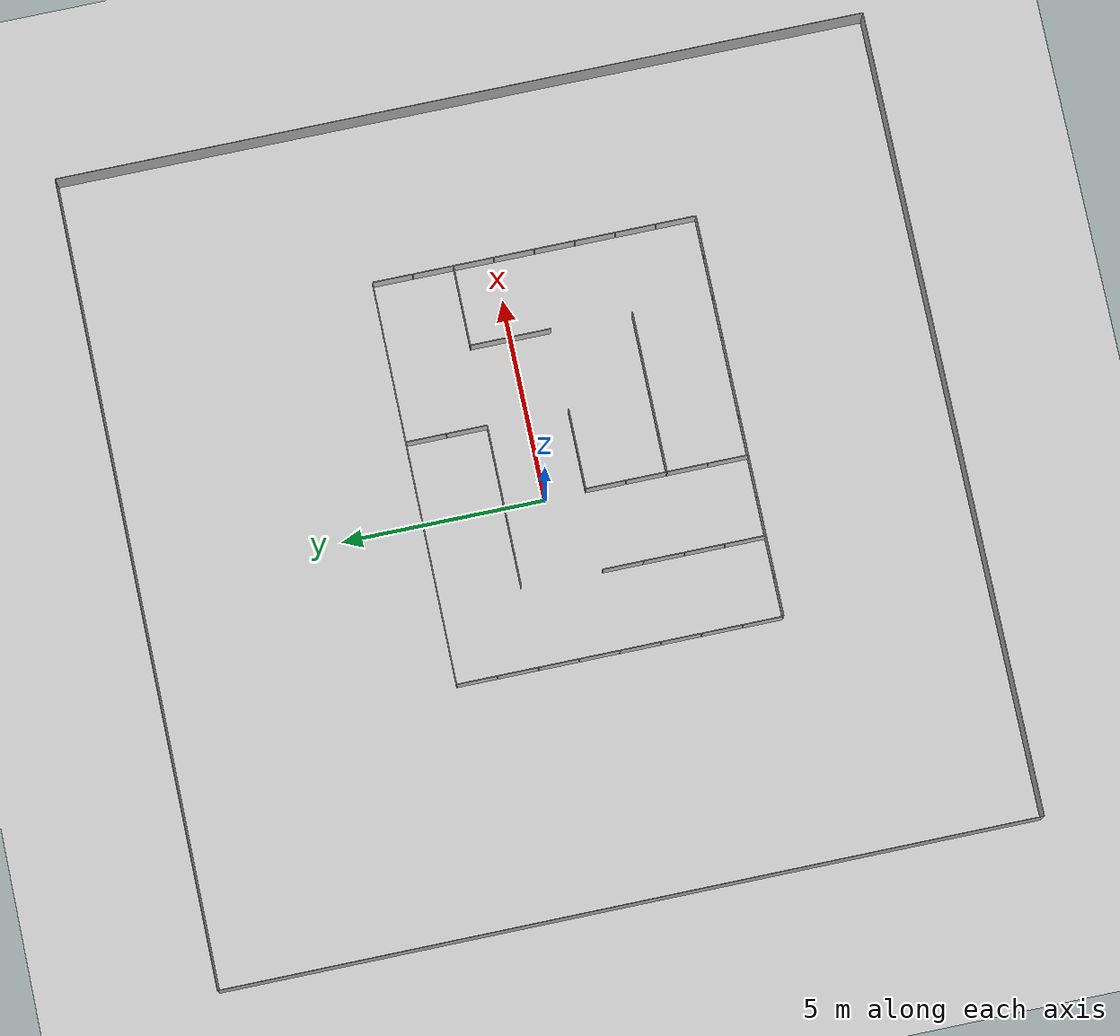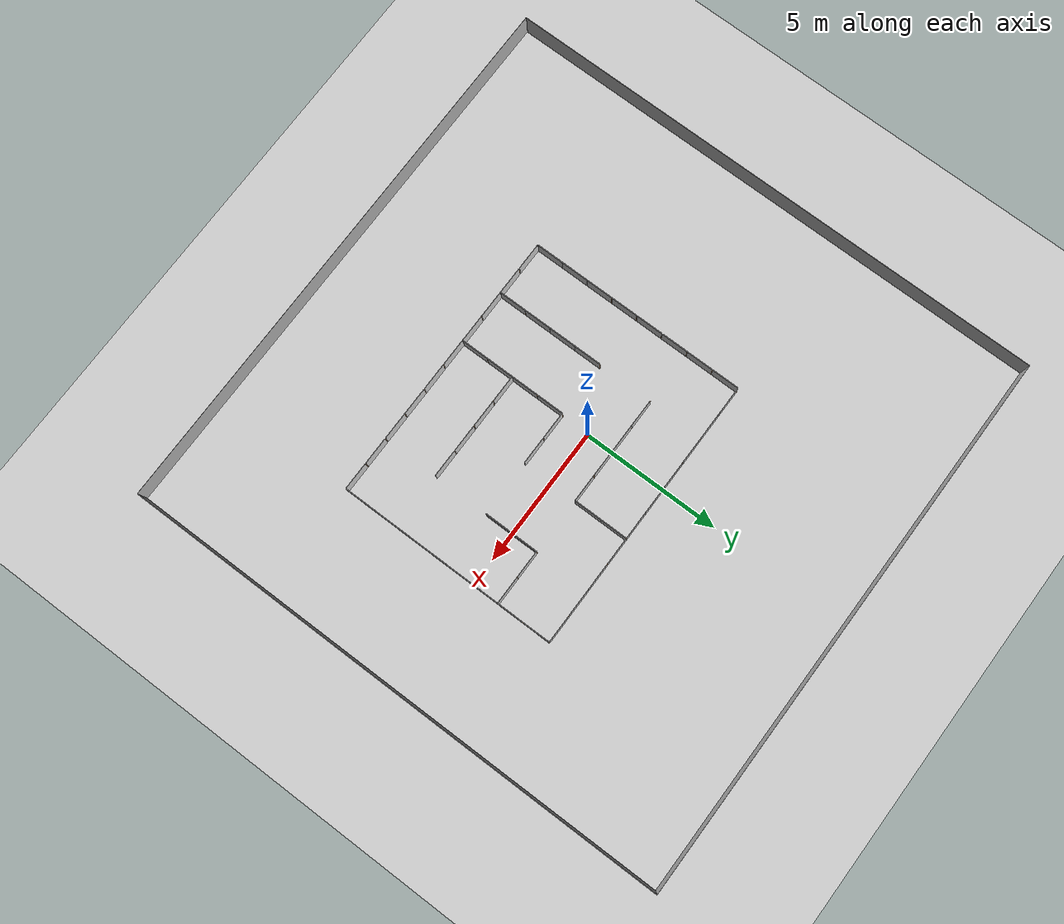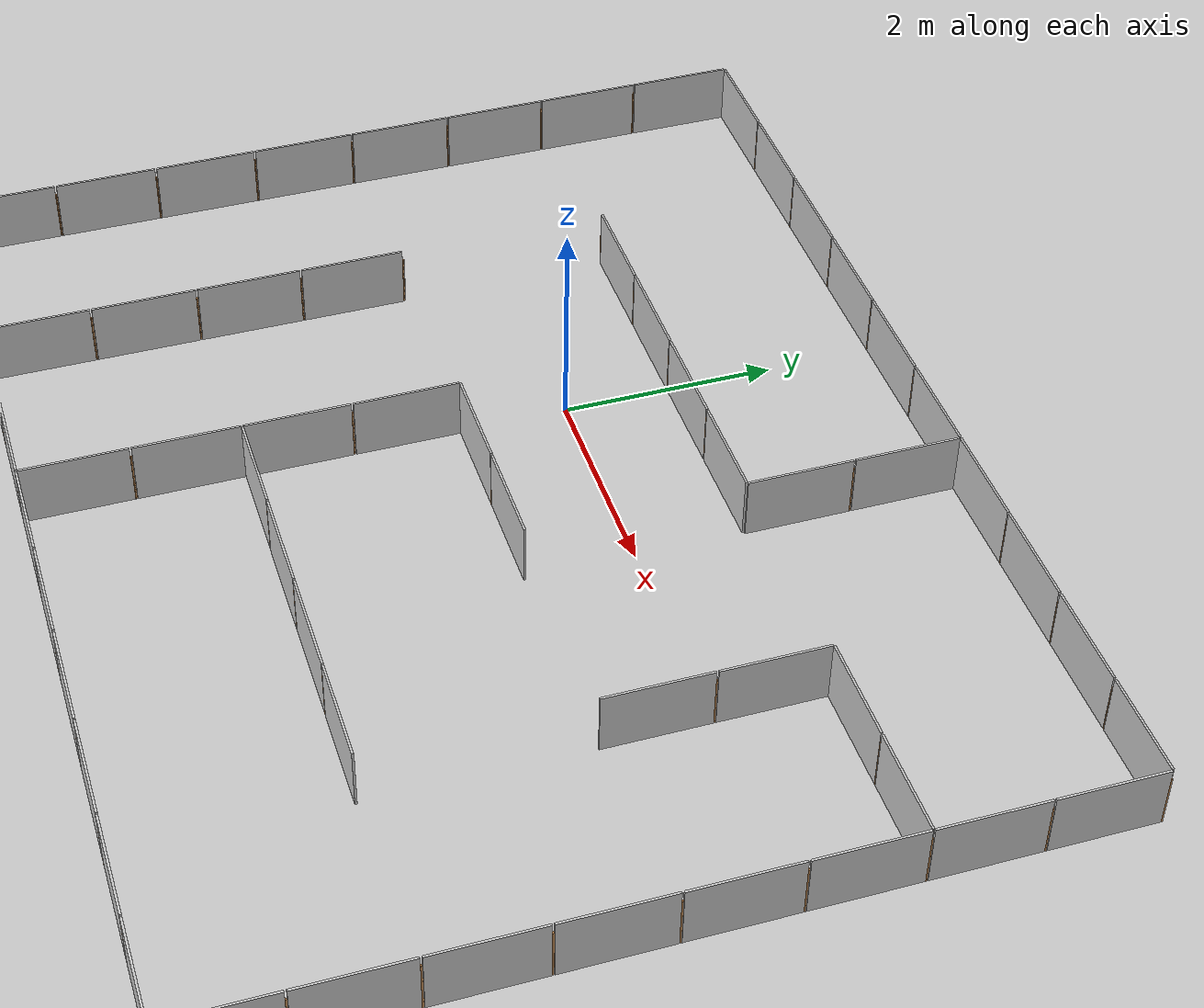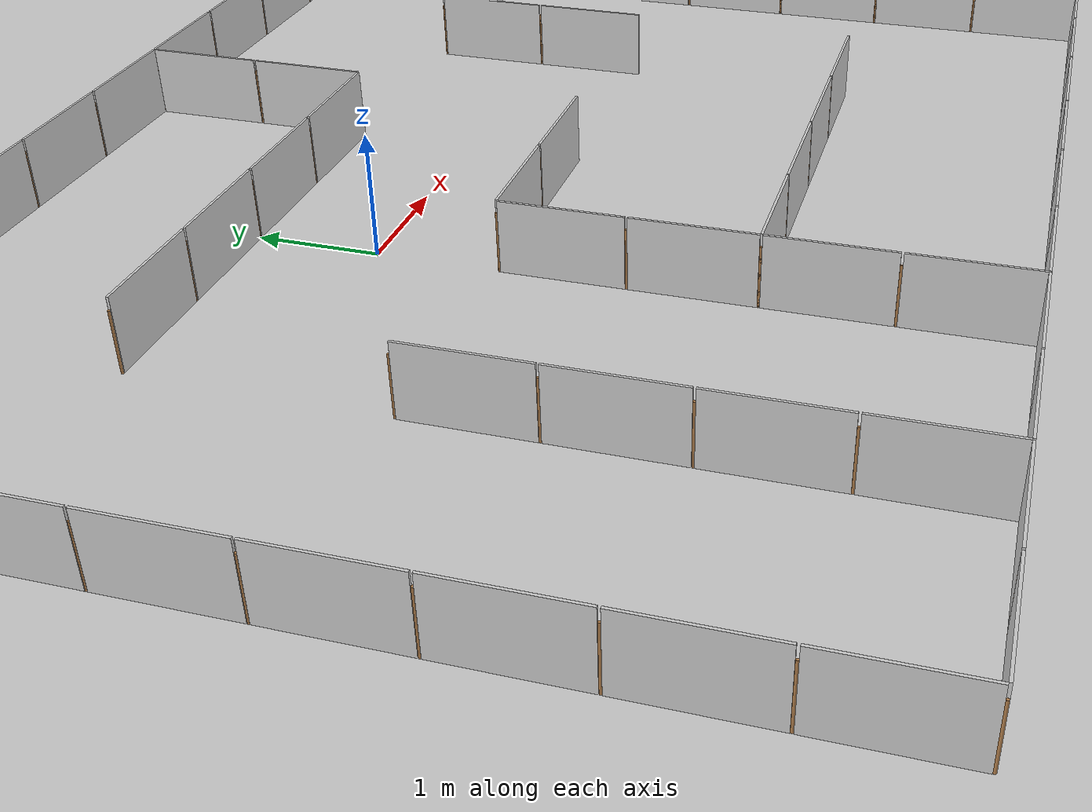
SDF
<sdf version='1.7'>
  <world name='default'>
    <physics type='ode'>
      <max_step_size>0.0040000000000000001</max_step_size>
      <real_time_factor>1</real_time_factor>
      <real_time_update_rate>250</real_time_update_rate>
    </physics>

    <plugin name='gz::sim::systems::Physics' filename='gz-sim-physics-system'/>
    <plugin name='gz::sim::systems::UserCommands' filename='gz-sim-user-commands-system'/>
    <plugin name='gz::sim::systems::SceneBroadcaster' filename='gz-sim-scene-broadcaster-system'/>
    <plugin name='gz::sim::systems::Contact' filename='gz-sim-contact-system'/>
    <plugin name='gz::sim::systems::Imu' filename='gz-sim-imu-system'/>
    <plugin name='gz::sim::systems::Magnetometer' filename='gz-sim-magnetometer-system'/>
    <plugin name='gz::sim::systems::Altimeter' filename='gz-sim-altimeter-system'/>
    <plugin name='gz::sim::systems::NavSat' filename='gz-sim-navsat-system'/>
    <plugin name='gz::sim::systems::Sensors' filename='gz-sim-sensors-system'>
      <render_engine>ogre2</render_engine>
    </plugin>

    <gui fullscreen='false'>
      <plugin name='3D View' filename='GzScene3D'>
        <gz-gui>
          <title>3D View</title>
          <property type='bool' key='showTitleBar'>0</property>
          <property type='string' key='state'>docked</property>
        </gz-gui>
        <engine>ogre2</engine>
        <scene>scene</scene>
        <ambient_light>0.5984631152222222 0.5984631152222222 0.5984631152222222</ambient_light>
        <background_color>0.8984631152222222 0.8984631152222222 0.8984631152222222</background_color>
        <camera_pose>-6 0 6 0 0.5 0</camera_pose>
      </plugin>
      <plugin name='World control' filename='WorldControl'>
        <gz-gui>
          <title>World control</title>
          <property type='bool' key='showTitleBar'>0</property>
          <property type='bool' key='resizable'>0</property>
          <property type='double' key='height'>72</property>
          <property type='double' key='width'>121</property>
          <property type='double' key='z'>1</property>
          <property type='string' key='state'>floating</property>
          <anchors target='3D View'>
            <line own='left' target='left'/>
            <line own='bottom' target='bottom'/>
          </anchors>
        </gz-gui>
        <play_pause>1</play_pause>
        <step>1</step>
        <start_paused>1</start_paused>
      </plugin>
      <plugin name='World stats' filename='WorldStats'>
        <gz-gui>
          <title>World stats</title>
          <property type='bool' key='showTitleBar'>0</property>
          <property type='bool' key='resizable'>0</property>
          <property type='double' key='height'>110</property>
          <property type='double' key='width'>290</property>
          <property type='double' key='z'>1</property>
          <property type='string' key='state'>floating</property>
          <anchors target='3D View'>
            <line own='right' target='right'/>
            <line own='bottom' target='bottom'/>
          </anchors>
        </gz-gui>
        <sim_time>1</sim_time>
        <real_time>1</real_time>
        <real_time_factor>1</real_time_factor>
        <iterations>1</iterations>
      </plugin>
    </gui>

    <gravity>0 0 -9.8000000000000007</gravity>
    <magnetic_field>6.0000000000000002e-06 2.3e-05 -4.1999999999999998e-05</magnetic_field>
    <atmosphere type='adiabatic'/>
    <spherical_coordinates>
      <surface_model>EARTH_WGS84</surface_model>
      <latitude_deg>39.79480109851339</latitude_deg>
      <longitude_deg>-84.08631702793322</longitude_deg>
      <elevation>265.2</elevation>
      <heading_deg>0</heading_deg>
    </spherical_coordinates>
    <scene>
      <grid>true</grid>
      <ambient>0.400000006 0.400000006 0.400000006 1</ambient>
      <background>0.699999988 0.699999988 0.699999988 1</background>
      <shadows>false</shadows>
    </scene>

    <light name='sunUTC' type='directional'>
      <pose>0 0 500 0 0 0</pose>
      <cast_shadows>false</cast_shadows>
      <intensity>1</intensity>
      <direction>0.001 0.625 -0.78000000000000003</direction>
      <diffuse>0.903999984 0.903999984 0.903999984 1</diffuse>
      <specular>0.270999998 0.270999998 0.270999998 1</specular>
      <attenuation>
        <range>2000</range>
        <linear>0</linear>
        <constant>1</constant>
        <quadratic>0</quadratic>
      </attenuation>
      <spot>
        <inner_angle>0</inner_angle>
        <outer_angle>0</outer_angle>
        <falloff>0</falloff>
      </spot>
    </light>

    <model name='ground_plane'>
      <static>true</static>
      <link name='link'>
        <collision name='collision'>
          <geometry>
            <plane>
              <normal>0 0 1</normal>
              <size>1 1</size>
            </plane>
          </geometry>
          <surface>
            <friction>
              <ode/>
              <torsional>
                <ode/>
              </torsional>
            </friction>
            <bounce/>
            <contact>
              <ode/>
            </contact>
          </surface>
          <max_contacts>10</max_contacts>
        </collision>
        <visual name='visual'>
          <geometry>
            <plane>
              <normal>0 0 1</normal>
              <size>100 100</size>
            </plane>
          </geometry>
          <material>
            <ambient>0.8 0.8 0.8 1</ambient>
            <diffuse>0.8 0.8 0.8 1</diffuse>
            <specular>0.8 0.8 0.8 1</specular>
          </material>
        </visual>
        <pose>0 0 0 0 -0 0</pose>
        <inertial>
          <pose>0 0 0 0 -0 0</pose>
          <mass>1</mass>
          <inertia>
            <ixx>1</ixx>
            <ixy>0</ixy>
            <ixz>0</ixz>
            <iyy>1</iyy>
            <iyz>0</iyz>
            <izz>1</izz>
          </inertia>
        </inertial>
        <enable_wind>0</enable_wind>
        <self_collide>0</self_collide>
        <kinematic>0</kinematic>
      </link>
      <pose>0 0 0 0 -0 0</pose>
      <self_collide>0</self_collide>
    </model>
    <model name='wall_1'>
      <pose>-10 0 0.5 0 0 -1.57</pose>
      <static>true</static>
      <link name='link'>
        <collision name='collision'>
          <geometry>
            <box>
              <size>20 0.01 1</size>
            </box>
          </geometry>
          <max_contacts>10</max_contacts>
          <surface>
            <contact>
              <ode/>
            </contact>
            <bounce/>
            <friction>
              <torsional>
                <ode/>
              </torsional>
              <ode/>
            </friction>
          </surface>
        </collision>
        <visual name='visual'>
          <geometry>
            <box>
              <size>20 0.01 1</size>
            </box>
          </geometry>
          <material>
            <ambient>0.7 0.7 0.7 1</ambient>
            <diffuse>0.7 0.7 0.7 1</diffuse>
            <specular>0.7 0.7 0.7 1</specular>
          </material>
        </visual>
        <inertial>
          <pose>0 0 0 0 -0 0</pose>
          <mass>1</mass>
          <inertia>
            <ixx>1</ixx>
            <ixy>0</ixy>
            <ixz>0</ixz>
            <iyy>1</iyy>
            <iyz>0</iyz>
            <izz>1</izz>
          </inertia>
        </inertial>
        <enable_wind>0</enable_wind>
        <self_collide>0</self_collide>
        <kinematic>0</kinematic>
      </link>
      <self_collide>0</self_collide>
    </model>
    <model name='wall_2'>
      <pose>10 0 0.5 0 0 -1.57</pose>
      <static>true</static>
      <link name='link'>
        <collision name='collision'>
          <geometry>
            <box>
              <size>20 0.01 1</size>
            </box>
          </geometry>
          <max_contacts>10</max_contacts>
          <surface>
            <contact>
              <ode/>
            </contact>
            <bounce/>
            <friction>
              <torsional>
                <ode/>
              </torsional>
              <ode/>
            </friction>
          </surface>
        </collision>
        <visual name='visual'>
          <geometry>
            <box>
              <size>20 0.01 1</size>
            </box>
          </geometry>
          <material>
            <ambient>0.7 0.7 0.7 1</ambient>
            <diffuse>0.7 0.7 0.7 1</diffuse>
            <specular>0.7 0.7 0.7 1</specular>
          </material>
        </visual>
        <inertial>
          <pose>0 0 0 0 -0 0</pose>
          <mass>1</mass>
          <inertia>
            <ixx>1</ixx>
            <ixy>0</ixy>
            <ixz>0</ixz>
            <iyy>1</iyy>
            <iyz>0</iyz>
            <izz>1</izz>
          </inertia>
        </inertial>
        <enable_wind>0</enable_wind>
        <self_collide>0</self_collide>
        <kinematic>0</kinematic>
      </link>
      <self_collide>0</self_collide>
    </model>
    <model name='wall_3'>
      <pose>0 10 0.5 0 -0 0</pose>
      <static>true</static>
      <link name='link'>
        <collision name='collision'>
          <geometry>
            <box>
              <size>20 0.01 1</size>
            </box>
          </geometry>
          <max_contacts>10</max_contacts>
          <surface>
            <contact>
              <ode/>
            </contact>
            <bounce/>
            <friction>
              <torsional>
                <ode/>
              </torsional>
              <ode/>
            </friction>
          </surface>
        </collision>
        <visual name='visual'>
          <geometry>
            <box>
              <size>20 0.01 1</size>
            </box>
          </geometry>
          <material>
            <ambient>0.7 0.7 0.7 1</ambient>
            <diffuse>0.7 0.7 0.7 1</diffuse>
            <specular>0.7 0.7 0.7 1</specular>
          </material>
        </visual>
        <inertial>
          <pose>0 0 0 0 -0 0</pose>
          <mass>1</mass>
          <inertia>
            <ixx>1</ixx>
            <ixy>0</ixy>
            <ixz>0</ixz>
            <iyy>1</iyy>
            <iyz>0</iyz>
            <izz>1</izz>
          </inertia>
        </inertial>
        <enable_wind>0</enable_wind>
        <self_collide>0</self_collide>
        <kinematic>0</kinematic>
      </link>
      <self_collide>0</self_collide>
    </model>
    <model name='wall_4'>
      <pose>0 -10 0.5 0 -0 0</pose>
      <static>true</static>
      <link name='link'>
        <collision name='collision'>
          <geometry>
            <box>
              <size>20 0.01 1</size>
            </box>
          </geometry>
          <max_contacts>10</max_contacts>
          <surface>
            <contact>
              <ode/>
            </contact>
            <bounce/>
            <friction>
              <torsional>
                <ode/>
              </torsional>
              <ode/>
            </friction>
          </surface>
        </collision>
        <visual name='visual'>
          <geometry>
            <box>
              <size>20 0.01 1</size>
            </box>
          </geometry>
          <material>
            <ambient>0.7 0.7 0.7 1</ambient>
            <diffuse>0.7 0.7 0.7 1</diffuse>
            <specular>0.7 0.7 0.7 1</specular>
          </material>
        </visual>
        <inertial>
          <pose>0 0 0 0 -0 0</pose>
          <mass>1</mass>
          <inertia>
            <ixx>1</ixx>
            <ixy>0</ixy>
            <ixz>0</ixz>
            <iyy>1</iyy>
            <iyz>0</iyz>
            <izz>1</izz>
          </inertia>
        </inertial>
        <enable_wind>0</enable_wind>
        <self_collide>0</self_collide>
        <kinematic>0</kinematic>
      </link>
      <self_collide>0</self_collide>
    </model>

    <model name='maze_1_6x5_clone'>
      <frame name='plywood_panel_0_0_b::__model__' attached_to='plywood_panel_0_0_b::main'>
        <pose relative_to='__model__'>0 0 0 0 -0 1.571</pose>
      </frame>
      <static>true</static>
      <link name='plywood_panel_0_0_b::main'>
        <pose relative_to='plywood_panel_0_0_b::__model__'>0 0 0 0 -0 0</pose>
        <collision name='collision'>
          <pose>0 -0.5 0.3 -1.571 -0 -1.571</pose>
          <geometry>
            <box>
              <size>0.98 0.6 0.02</size>
            </box>
          </geometry>
          <max_contacts>10</max_contacts>
          <surface>
            <contact>
              <ode/>
            </contact>
            <bounce/>
            <friction>
              <torsional>
                <ode/>
              </torsional>
              <ode/>
            </friction>
          </surface>
        </collision>
        <visual name='visual'>
          <pose>0.01 -0.01 0 3.14159 -1.57059 3.14159</pose>
          <geometry>
            <mesh>
              <scale>1 1 1</scale>
              <uri>/home/mayank/cognipilot/cranium/src/dream_world/models/plywood_panel/meshes/plywood.dae</uri>
            </mesh>
          </geometry>
        </visual>
        <self_collide>0</self_collide>
        <enable_wind>0</enable_wind>
        <kinematic>0</kinematic>
      </link>
      <frame name='wooden_joint_0_0_b::__model__' attached_to='wooden_joint_0_0_b::link_0'>
        <pose relative_to='__model__'>0 0 0 0 -0 0</pose>
      </frame>
      <link name='wooden_joint_0_0_b::link_0'>
        <pose relative_to='wooden_joint_0_0_b::__model__'>0 0 0.25 0 -0 0</pose>
        <inertial>
          <mass>0.00215981</mass>
          <inertia>
            <ixx>0.00018028</ixx>
            <ixy>0</ixy>
            <ixz>0</ixz>
            <iyy>0.00018028</iyy>
            <iyz>0</iyz>
            <izz>5.8e-07</izz>
          </inertia>
          <pose>0 0 0 0 -0 0</pose>
        </inertial>
        <gravity>1</gravity>
        <self_collide>0</self_collide>
        <kinematic>0</kinematic>
        <visual name='visual'>
          <pose>0 0 0 0 -0 0</pose>
          <geometry>
            <cylinder>
              <radius>0.01</radius>
              <length>0.5</length>
            </cylinder>
          </geometry>
          <material>
            <lighting>1</lighting>
            <script>
              <uri>file://media/materials/scripts/gazebo.material</uri>
              <name>Gazebo/Wood</name>
            </script>
            <shader type='pixel'>
              <normal_map>__default__</normal_map>
            </shader>
            <ambient>0.3 0.3 0.3 1</ambient>
            <diffuse>0.7 0.7 0.7 1</diffuse>
            <specular>0.01 0.01 0.01 1</specular>
            <emissive>0 0 0 1</emissive>
          </material>
          <transparency>0</transparency>
          <cast_shadows>1</cast_shadows>
        </visual>
        <collision name='collision'>
          <laser_retro>0</laser_retro>
          <max_contacts>10</max_contacts>
          <pose>0 0 0 0 -0 0</pose>
          <geometry>
            <cylinder>
              <radius>0.01</radius>
              <length>0.5</length>
            </cylinder>
          </geometry>
          <surface>
            <friction>
              <ode>
                <mu>1</mu>
                <mu2>1</mu2>
                <fdir1>0 0 0</fdir1>
                <slip1>0</slip1>
                <slip2>0</slip2>
              </ode>
              <torsional>
                <coefficient>1</coefficient>
                <patch_radius>0</patch_radius>
                <surface_radius>0</surface_radius>
                <use_patch_radius>1</use_patch_radius>
                <ode>
                  <slip>0</slip>
                </ode>
              </torsional>
            </friction>
            <bounce>
              <restitution_coefficient>0</restitution_coefficient>
              <threshold>1e+06</threshold>
            </bounce>
            <contact>
              <collide_without_contact>0</collide_without_contact>
              <collide_without_contact_bitmask>1</collide_without_contact_bitmask>
              <collide_bitmask>1</collide_bitmask>
              <ode>
                <soft_cfm>0</soft_cfm>
                <soft_erp>0.2</soft_erp>
                <kp>1e+13</kp>
                <kd>1</kd>
                <max_vel>0.01</max_vel>
                <min_depth>0</min_depth>
              </ode>
              <bullet>
                <split_impulse>1</split_impulse>
                <split_impulse_penetration_threshold>-0.01</split_impulse_penetration_threshold>
                <soft_cfm>0</soft_cfm>
                <soft_erp>0.2</soft_erp>
                <kp>1e+13</kp>
                <kd>1</kd>
              </bullet>
            </contact>
          </surface>
        </collision>
        <enable_wind>0</enable_wind>
      </link>
      <static>true</static>
      <allow_auto_disable>1</allow_auto_disable>
      <pose>-2 -2 0 0 0 -1.5708</pose>
    </model>
    <model name='maze_1_6x5_clone_0'>
      <frame name='plywood_panel_0_0_b::__model__' attached_to='plywood_panel_0_0_b::main'>
        <pose relative_to='__model__'>0 0 0 0 -0 1.571</pose>
      </frame>
      <static>true</static>
      <link name='plywood_panel_0_0_b::main'>
        <pose relative_to='plywood_panel_0_0_b::__model__'>0 0 0 0 -0 0</pose>
        <collision name='collision'>
          <pose>0 -0.5 0.3 -1.571 -0 -1.571</pose>
          <geometry>
            <box>
              <size>0.98 0.6 0.02</size>
            </box>
          </geometry>
          <max_contacts>10</max_contacts>
          <surface>
            <contact>
              <ode/>
            </contact>
            <bounce/>
            <friction>
              <torsional>
                <ode/>
              </torsional>
              <ode/>
            </friction>
          </surface>
        </collision>
        <visual name='visual'>
          <pose>0.01 -0.01 0 3.14159 -1.57059 3.14159</pose>
          <geometry>
            <mesh>
              <scale>1 1 1</scale>
              <uri>/home/mayank/cognipilot/cranium/src/dream_world/models/plywood_panel/meshes/plywood.dae</uri>
            </mesh>
          </geometry>
        </visual>
        <self_collide>0</self_collide>
        <enable_wind>0</enable_wind>
        <kinematic>0</kinematic>
      </link>
      <frame name='wooden_joint_0_0_b::__model__' attached_to='wooden_joint_0_0_b::link_0'>
        <pose relative_to='__model__'>0 0 0 0 -0 0</pose>
      </frame>
      <link name='wooden_joint_0_0_b::link_0'>
        <pose relative_to='wooden_joint_0_0_b::__model__'>0 0 0.25 0 -0 0</pose>
        <inertial>
          <mass>0.00215981</mass>
          <inertia>
            <ixx>0.00018028</ixx>
            <ixy>0</ixy>
            <ixz>0</ixz>
            <iyy>0.00018028</iyy>
            <iyz>0</iyz>
            <izz>5.8e-07</izz>
          </inertia>
          <pose>0 0 0 0 -0 0</pose>
        </inertial>
        <gravity>1</gravity>
        <self_collide>0</self_collide>
        <kinematic>0</kinematic>
        <visual name='visual'>
          <pose>0 0 0 0 -0 0</pose>
          <geometry>
            <cylinder>
              <radius>0.01</radius>
              <length>0.5</length>
            </cylinder>
          </geometry>
          <material>
            <lighting>1</lighting>
            <script>
              <uri>file://media/materials/scripts/gazebo.material</uri>
              <name>Gazebo/Wood</name>
            </script>
            <shader type='pixel'>
              <normal_map>__default__</normal_map>
            </shader>
            <ambient>0.3 0.3 0.3 1</ambient>
            <diffuse>0.7 0.7 0.7 1</diffuse>
            <specular>0.01 0.01 0.01 1</specular>
            <emissive>0 0 0 1</emissive>
          </material>
          <transparency>0</transparency>
          <cast_shadows>1</cast_shadows>
        </visual>
        <collision name='collision'>
          <laser_retro>0</laser_retro>
          <max_contacts>10</max_contacts>
          <pose>0 0 0 0 -0 0</pose>
          <geometry>
            <cylinder>
              <radius>0.01</radius>
              <length>0.5</length>
            </cylinder>
          </geometry>
          <surface>
            <friction>
              <ode>
                <mu>1</mu>
                <mu2>1</mu2>
                <fdir1>0 0 0</fdir1>
                <slip1>0</slip1>
                <slip2>0</slip2>
              </ode>
              <torsional>
                <coefficient>1</coefficient>
                <patch_radius>0</patch_radius>
                <surface_radius>0</surface_radius>
                <use_patch_radius>1</use_patch_radius>
                <ode>
                  <slip>0</slip>
                </ode>
              </torsional>
            </friction>
            <bounce>
              <restitution_coefficient>0</restitution_coefficient>
              <threshold>1e+06</threshold>
            </bounce>
            <contact>
              <collide_without_contact>0</collide_without_contact>
              <collide_without_contact_bitmask>1</collide_without_contact_bitmask>
              <collide_bitmask>1</collide_bitmask>
              <ode>
                <soft_cfm>0</soft_cfm>
                <soft_erp>0.2</soft_erp>
                <kp>1e+13</kp>
                <kd>1</kd>
                <max_vel>0.01</max_vel>
                <min_depth>0</min_depth>
              </ode>
              <bullet>
                <split_impulse>1</split_impulse>
                <split_impulse_penetration_threshold>-0.01</split_impulse_penetration_threshold>
                <soft_cfm>0</soft_cfm>
                <soft_erp>0.2</soft_erp>
                <kp>1e+13</kp>
                <kd>1</kd>
              </bullet>
            </contact>
          </surface>
        </collision>
        <enable_wind>0</enable_wind>
      </link>
      <static>true</static>
      <allow_auto_disable>1</allow_auto_disable>
      <pose>-2 -3 0 0 0 -1.5708</pose>
    </model>
    <model name='maze_1_6x5_clone_1'>
      <frame name='plywood_panel_0_0_b::__model__' attached_to='plywood_panel_0_0_b::main'>
        <pose relative_to='__model__'>0 0 0 0 -0 1.571</pose>
      </frame>
      <static>true</static>
      <link name='plywood_panel_0_0_b::main'>
        <pose relative_to='plywood_panel_0_0_b::__model__'>0 0 0 0 -0 0</pose>
        <collision name='collision'>
          <pose>0 -0.5 0.3 -1.571 -0 -1.571</pose>
          <geometry>
            <box>
              <size>0.98 0.6 0.02</size>
            </box>
          </geometry>
          <max_contacts>10</max_contacts>
          <surface>
            <contact>
              <ode/>
            </contact>
            <bounce/>
            <friction>
              <torsional>
                <ode/>
              </torsional>
              <ode/>
            </friction>
          </surface>
        </collision>
        <visual name='visual'>
          <pose>0.01 -0.01 0 3.14159 -1.57059 3.14159</pose>
          <geometry>
            <mesh>
              <scale>1 1 1</scale>
              <uri>/home/mayank/cognipilot/cranium/src/dream_world/models/plywood_panel/meshes/plywood.dae</uri>
            </mesh>
          </geometry>
        </visual>
        <self_collide>0</self_collide>
        <enable_wind>0</enable_wind>
        <kinematic>0</kinematic>
      </link>
      <frame name='wooden_joint_0_0_b::__model__' attached_to='wooden_joint_0_0_b::link_0'>
        <pose relative_to='__model__'>0 0 0 0 -0 0</pose>
      </frame>
      <link name='wooden_joint_0_0_b::link_0'>
        <pose relative_to='wooden_joint_0_0_b::__model__'>0 0 0.25 0 -0 0</pose>
        <inertial>
          <mass>0.00215981</mass>
          <inertia>
            <ixx>0.00018028</ixx>
            <ixy>0</ixy>
            <ixz>0</ixz>
            <iyy>0.00018028</iyy>
            <iyz>0</iyz>
            <izz>5.8e-07</izz>
          </inertia>
          <pose>0 0 0 0 -0 0</pose>
        </inertial>
        <gravity>1</gravity>
        <self_collide>0</self_collide>
        <kinematic>0</kinematic>
        <visual name='visual'>
          <pose>0 0 0 0 -0 0</pose>
          <geometry>
            <cylinder>
              <radius>0.01</radius>
              <length>0.5</length>
            </cylinder>
          </geometry>
          <material>
            <lighting>1</lighting>
            <script>
              <uri>file://media/materials/scripts/gazebo.material</uri>
              <name>Gazebo/Wood</name>
            </script>
            <shader type='pixel'>
              <normal_map>__default__</normal_map>
            </shader>
            <ambient>0.3 0.3 0.3 1</ambient>
            <diffuse>0.7 0.7 0.7 1</diffuse>
            <specular>0.01 0.01 0.01 1</specular>
            <emissive>0 0 0 1</emissive>
          </material>
          <transparency>0</transparency>
          <cast_shadows>1</cast_shadows>
        </visual>
        <collision name='collision'>
          <laser_retro>0</laser_retro>
          <max_contacts>10</max_contacts>
          <pose>0 0 0 0 -0 0</pose>
          <geometry>
            <cylinder>
              <radius>0.01</radius>
              <length>0.5</length>
            </cylinder>
          </geometry>
          <surface>
            <friction>
              <ode>
                <mu>1</mu>
                <mu2>1</mu2>
                <fdir1>0 0 0</fdir1>
                <slip1>0</slip1>
                <slip2>0</slip2>
              </ode>
              <torsional>
                <coefficient>1</coefficient>
                <patch_radius>0</patch_radius>
                <surface_radius>0</surface_radius>
                <use_patch_radius>1</use_patch_radius>
                <ode>
                  <slip>0</slip>
                </ode>
              </torsional>
            </friction>
            <bounce>
              <restitution_coefficient>0</restitution_coefficient>
              <threshold>1e+06</threshold>
            </bounce>
            <contact>
              <collide_without_contact>0</collide_without_contact>
              <collide_without_contact_bitmask>1</collide_without_contact_bitmask>
              <collide_bitmask>1</collide_bitmask>
              <ode>
                <soft_cfm>0</soft_cfm>
                <soft_erp>0.2</soft_erp>
                <kp>1e+13</kp>
                <kd>1</kd>
                <max_vel>0.01</max_vel>
                <min_depth>0</min_depth>
              </ode>
              <bullet>
                <split_impulse>1</split_impulse>
                <split_impulse_penetration_threshold>-0.01</split_impulse_penetration_threshold>
                <soft_cfm>0</soft_cfm>
                <soft_erp>0.2</soft_erp>
                <kp>1e+13</kp>
                <kd>1</kd>
              </bullet>
            </contact>
          </surface>
        </collision>
        <enable_wind>0</enable_wind>
      </link>
      <static>true</static>
      <allow_auto_disable>1</allow_auto_disable>
      <pose>-2 -4 0 0 0 -1.5708</pose>
    </model>
    <model name='maze_1_6x5_clone_2_clone'>
      <frame name='plywood_panel_0_0_b::__model__' attached_to='plywood_panel_0_0_b::main'>
        <pose relative_to='__model__'>0 0 0 0 -0 1.571</pose>
      </frame>
      <static>true</static>
      <link name='plywood_panel_0_0_b::main'>
        <pose relative_to='plywood_panel_0_0_b::__model__'>0 0 0 0 -0 0</pose>
        <collision name='collision'>
          <pose>0 -0.5 0.3 -1.571 -0 -1.571</pose>
          <geometry>
            <box>
              <size>0.98 0.6 0.02</size>
            </box>
          </geometry>
          <max_contacts>10</max_contacts>
          <surface>
            <contact>
              <ode/>
            </contact>
            <bounce/>
            <friction>
              <torsional>
                <ode/>
              </torsional>
              <ode/>
            </friction>
          </surface>
        </collision>
        <visual name='visual'>
          <pose>0.01 -0.01 0 3.14159 -1.57059 3.14159</pose>
          <geometry>
            <mesh>
              <scale>1 1 1</scale>
              <uri>/home/mayank/cognipilot/cranium/src/dream_world/models/plywood_panel/meshes/plywood.dae</uri>
            </mesh>
          </geometry>
        </visual>
        <self_collide>0</self_collide>
        <enable_wind>0</enable_wind>
        <kinematic>0</kinematic>
      </link>
      <frame name='wooden_joint_0_0_b::__model__' attached_to='wooden_joint_0_0_b::link_0'>
        <pose relative_to='__model__'>0 0 0 0 -0 0</pose>
      </frame>
      <link name='wooden_joint_0_0_b::link_0'>
        <pose relative_to='wooden_joint_0_0_b::__model__'>0 0 0.25 0 -0 0</pose>
        <inertial>
          <mass>0.00215981</mass>
          <inertia>
            <ixx>0.00018028</ixx>
            <ixy>0</ixy>
            <ixz>0</ixz>
            <iyy>0.00018028</iyy>
            <iyz>0</iyz>
            <izz>5.8e-07</izz>
          </inertia>
          <pose>0 0 0 0 -0 0</pose>
        </inertial>
        <gravity>1</gravity>
        <self_collide>0</self_collide>
        <kinematic>0</kinematic>
        <visual name='visual'>
          <pose>0 0 0 0 -0 0</pose>
          <geometry>
            <cylinder>
              <radius>0.01</radius>
              <length>0.5</length>
            </cylinder>
          </geometry>
          <material>
            <lighting>1</lighting>
            <script>
              <uri>file://media/materials/scripts/gazebo.material</uri>
              <name>Gazebo/Wood</name>
            </script>
            <shader type='pixel'>
              <normal_map>__default__</normal_map>
            </shader>
            <ambient>0.3 0.3 0.3 1</ambient>
            <diffuse>0.7 0.7 0.7 1</diffuse>
            <specular>0.01 0.01 0.01 1</specular>
            <emissive>0 0 0 1</emissive>
          </material>
          <transparency>0</transparency>
          <cast_shadows>1</cast_shadows>
        </visual>
        <collision name='collision'>
          <laser_retro>0</laser_retro>
          <max_contacts>10</max_contacts>
          <pose>0 0 0 0 -0 0</pose>
          <geometry>
            <cylinder>
              <radius>0.01</radius>
              <length>0.5</length>
            </cylinder>
          </geometry>
          <surface>
            <friction>
              <ode>
                <mu>1</mu>
                <mu2>1</mu2>
                <fdir1>0 0 0</fdir1>
                <slip1>0</slip1>
                <slip2>0</slip2>
              </ode>
              <torsional>
                <coefficient>1</coefficient>
                <patch_radius>0</patch_radius>
                <surface_radius>0</surface_radius>
                <use_patch_radius>1</use_patch_radius>
                <ode>
                  <slip>0</slip>
                </ode>
              </torsional>
            </friction>
            <bounce>
              <restitution_coefficient>0</restitution_coefficient>
              <threshold>1e+06</threshold>
            </bounce>
            <contact>
              <collide_without_contact>0</collide_without_contact>
              <collide_without_contact_bitmask>1</collide_without_contact_bitmask>
              <collide_bitmask>1</collide_bitmask>
              <ode>
                <soft_cfm>0</soft_cfm>
                <soft_erp>0.2</soft_erp>
                <kp>1e+13</kp>
                <kd>1</kd>
                <max_vel>0.01</max_vel>
                <min_depth>0</min_depth>
              </ode>
              <bullet>
                <split_impulse>1</split_impulse>
                <split_impulse_penetration_threshold>-0.01</split_impulse_penetration_threshold>
                <soft_cfm>0</soft_cfm>
                <soft_erp>0.2</soft_erp>
                <kp>1e+13</kp>
                <kd>1</kd>
              </bullet>
            </contact>
          </surface>
        </collision>
        <enable_wind>0</enable_wind>
      </link>
      <static>true</static>
      <allow_auto_disable>1</allow_auto_disable>
      <pose>-1 -5 0 0 0 -4e-06</pose>
    </model>
    <model name='maze_1_6x5_clone_2_clone_clone'>
      <frame name='plywood_panel_0_0_b::__model__' attached_to='plywood_panel_0_0_b::main'>
        <pose relative_to='__model__'>0 0 0 0 -0 1.571</pose>
      </frame>
      <static>true</static>
      <link name='plywood_panel_0_0_b::main'>
        <pose relative_to='plywood_panel_0_0_b::__model__'>0 0 0 0 -0 0</pose>
        <collision name='collision'>
          <pose>0 -0.5 0.3 -1.571 -0 -1.571</pose>
          <geometry>
            <box>
              <size>0.98 0.6 0.02</size>
            </box>
          </geometry>
          <max_contacts>10</max_contacts>
          <surface>
            <contact>
              <ode/>
            </contact>
            <bounce/>
            <friction>
              <torsional>
                <ode/>
              </torsional>
              <ode/>
            </friction>
          </surface>
        </collision>
        <visual name='visual'>
          <pose>0.01 -0.01 0 3.14159 -1.57059 3.14159</pose>
          <geometry>
            <mesh>
              <scale>1 1 1</scale>
              <uri>/home/mayank/cognipilot/cranium/src/dream_world/models/plywood_panel/meshes/plywood.dae</uri>
            </mesh>
          </geometry>
        </visual>
        <self_collide>0</self_collide>
        <enable_wind>0</enable_wind>
        <kinematic>0</kinematic>
      </link>
      <frame name='wooden_joint_0_0_b::__model__' attached_to='wooden_joint_0_0_b::link_0'>
        <pose relative_to='__model__'>0 0 0 0 -0 0</pose>
      </frame>
      <link name='wooden_joint_0_0_b::link_0'>
        <pose relative_to='wooden_joint_0_0_b::__model__'>0 0 0.25 0 -0 0</pose>
        <inertial>
          <mass>0.00215981</mass>
          <inertia>
            <ixx>0.00018028</ixx>
            <ixy>0</ixy>
            <ixz>0</ixz>
            <iyy>0.00018028</iyy>
            <iyz>0</iyz>
            <izz>5.8e-07</izz>
          </inertia>
          <pose>0 0 0 0 -0 0</pose>
        </inertial>
        <gravity>1</gravity>
        <self_collide>0</self_collide>
        <kinematic>0</kinematic>
        <visual name='visual'>
          <pose>0 0 0 0 -0 0</pose>
          <geometry>
            <cylinder>
              <radius>0.01</radius>
              <length>0.5</length>
            </cylinder>
          </geometry>
          <material>
            <lighting>1</lighting>
            <script>
              <uri>file://media/materials/scripts/gazebo.material</uri>
              <name>Gazebo/Wood</name>
            </script>
            <shader type='pixel'>
              <normal_map>__default__</normal_map>
            </shader>
            <ambient>0.3 0.3 0.3 1</ambient>
            <diffuse>0.7 0.7 0.7 1</diffuse>
            <specular>0.01 0.01 0.01 1</specular>
            <emissive>0 0 0 1</emissive>
          </material>
          <transparency>0</transparency>
          <cast_shadows>1</cast_shadows>
        </visual>
        <collision name='collision'>
          <laser_retro>0</laser_retro>
          <max_contacts>10</max_contacts>
          <pose>0 0 0 0 -0 0</pose>
          <geometry>
            <cylinder>
              <radius>0.01</radius>
              <length>0.5</length>
            </cylinder>
          </geometry>
          <surface>
            <friction>
              <ode>
                <mu>1</mu>
                <mu2>1</mu2>
                <fdir1>0 0 0</fdir1>
                <slip1>0</slip1>
                <slip2>0</slip2>
              </ode>
              <torsional>
                <coefficient>1</coefficient>
                <patch_radius>0</patch_radius>
                <surface_radius>0</surface_radius>
                <use_patch_radius>1</use_patch_radius>
                <ode>
                  <slip>0</slip>
                </ode>
              </torsional>
            </friction>
            <bounce>
              <restitution_coefficient>0</restitution_coefficient>
              <threshold>1e+06</threshold>
            </bounce>
            <contact>
              <collide_without_contact>0</collide_without_contact>
              <collide_without_contact_bitmask>1</collide_without_contact_bitmask>
              <collide_bitmask>1</collide_bitmask>
              <ode>
                <soft_cfm>0</soft_cfm>
                <soft_erp>0.2</soft_erp>
                <kp>1e+13</kp>
                <kd>1</kd>
                <max_vel>0.01</max_vel>
                <min_depth>0</min_depth>
              </ode>
              <bullet>
                <split_impulse>1</split_impulse>
                <split_impulse_penetration_threshold>-0.01</split_impulse_penetration_threshold>
                <soft_cfm>0</soft_cfm>
                <soft_erp>0.2</soft_erp>
                <kp>1e+13</kp>
                <kd>1</kd>
              </bullet>
            </contact>
          </surface>
        </collision>
        <enable_wind>0</enable_wind>
      </link>
      <static>true</static>
      <allow_auto_disable>1</allow_auto_disable>
      <pose>0 -5 0 0 0 -4e-06</pose>
    </model>
    <model name='maze_1_6x5_clone_2_clone_clone_0'>
      <frame name='plywood_panel_0_0_b::__model__' attached_to='plywood_panel_0_0_b::main'>
        <pose relative_to='__model__'>0 0 0 0 -0 1.571</pose>
      </frame>
      <static>true</static>
      <link name='plywood_panel_0_0_b::main'>
        <pose relative_to='plywood_panel_0_0_b::__model__'>0 0 0 0 -0 0</pose>
        <collision name='collision'>
          <pose>0 -0.5 0.3 -1.571 -0 -1.571</pose>
          <geometry>
            <box>
              <size>0.98 0.6 0.02</size>
            </box>
          </geometry>
          <max_contacts>10</max_contacts>
          <surface>
            <contact>
              <ode/>
            </contact>
            <bounce/>
            <friction>
              <torsional>
                <ode/>
              </torsional>
              <ode/>
            </friction>
          </surface>
        </collision>
        <visual name='visual'>
          <pose>0.01 -0.01 0 3.14159 -1.57059 3.14159</pose>
          <geometry>
            <mesh>
              <scale>1 1 1</scale>
              <uri>/home/mayank/cognipilot/cranium/src/dream_world/models/plywood_panel/meshes/plywood.dae</uri>
            </mesh>
          </geometry>
        </visual>
        <self_collide>0</self_collide>
        <enable_wind>0</enable_wind>
        <kinematic>0</kinematic>
      </link>
      <frame name='wooden_joint_0_0_b::__model__' attached_to='wooden_joint_0_0_b::link_0'>
        <pose relative_to='__model__'>0 0 0 0 -0 0</pose>
      </frame>
      <link name='wooden_joint_0_0_b::link_0'>
        <pose relative_to='wooden_joint_0_0_b::__model__'>0 0 0.25 0 -0 0</pose>
        <inertial>
          <mass>0.00215981</mass>
          <inertia>
            <ixx>0.00018028</ixx>
            <ixy>0</ixy>
            <ixz>0</ixz>
            <iyy>0.00018028</iyy>
            <iyz>0</iyz>
            <izz>5.8e-07</izz>
          </inertia>
          <pose>0 0 0 0 -0 0</pose>
        </inertial>
        <gravity>1</gravity>
        <self_collide>0</self_collide>
        <kinematic>0</kinematic>
        <visual name='visual'>
          <pose>0 0 0 0 -0 0</pose>
          <geometry>
            <cylinder>
              <radius>0.01</radius>
              <length>0.5</length>
            </cylinder>
          </geometry>
          <material>
            <lighting>1</lighting>
            <script>
              <uri>file://media/materials/scripts/gazebo.material</uri>
              <name>Gazebo/Wood</name>
            </script>
            <shader type='pixel'>
              <normal_map>__default__</normal_map>
            </shader>
            <ambient>0.3 0.3 0.3 1</ambient>
            <diffuse>0.7 0.7 0.7 1</diffuse>
            <specular>0.01 0.01 0.01 1</specular>
            <emissive>0 0 0 1</emissive>
          </material>
          <transparency>0</transparency>
          <cast_shadows>1</cast_shadows>
        </visual>
        <collision name='collision'>
          <laser_retro>0</laser_retro>
          <max_contacts>10</max_contacts>
          <pose>0 0 0 0 -0 0</pose>
          <geometry>
            <cylinder>
              <radius>0.01</radius>
              <length>0.5</length>
            </cylinder>
          </geometry>
          <surface>
            <friction>
              <ode>
                <mu>1</mu>
                <mu2>1</mu2>
                <fdir1>0 0 0</fdir1>
                <slip1>0</slip1>
                <slip2>0</slip2>
              </ode>
              <torsional>
                <coefficient>1</coefficient>
                <patch_radius>0</patch_radius>
                <surface_radius>0</surface_radius>
                <use_patch_radius>1</use_patch_radius>
                <ode>
                  <slip>0</slip>
                </ode>
              </torsional>
            </friction>
            <bounce>
              <restitution_coefficient>0</restitution_coefficient>
              <threshold>1e+06</threshold>
            </bounce>
            <contact>
              <collide_without_contact>0</collide_without_contact>
              <collide_without_contact_bitmask>1</collide_without_contact_bitmask>
              <collide_bitmask>1</collide_bitmask>
              <ode>
                <soft_cfm>0</soft_cfm>
                <soft_erp>0.2</soft_erp>
                <kp>1e+13</kp>
                <kd>1</kd>
                <max_vel>0.01</max_vel>
                <min_depth>0</min_depth>
              </ode>
              <bullet>
                <split_impulse>1</split_impulse>
                <split_impulse_penetration_threshold>-0.01</split_impulse_penetration_threshold>
                <soft_cfm>0</soft_cfm>
                <soft_erp>0.2</soft_erp>
                <kp>1e+13</kp>
                <kd>1</kd>
              </bullet>
            </contact>
          </surface>
        </collision>
        <enable_wind>0</enable_wind>
      </link>
      <static>true</static>
      <allow_auto_disable>1</allow_auto_disable>
      <pose>1 -5 0 0 0 -4e-06</pose>
    </model>
    <model name='maze_1_6x5_clone_2_clone_clone_1'>
      <frame name='plywood_panel_0_0_b::__model__' attached_to='plywood_panel_0_0_b::main'>
        <pose relative_to='__model__'>0 0 0 0 -0 1.571</pose>
      </frame>
      <static>true</static>
      <link name='plywood_panel_0_0_b::main'>
        <pose relative_to='plywood_panel_0_0_b::__model__'>0 0 0 0 -0 0</pose>
        <collision name='collision'>
          <pose>0 -0.5 0.3 -1.571 -0 -1.571</pose>
          <geometry>
            <box>
              <size>0.98 0.6 0.02</size>
            </box>
          </geometry>
          <max_contacts>10</max_contacts>
          <surface>
            <contact>
              <ode/>
            </contact>
            <bounce/>
            <friction>
              <torsional>
                <ode/>
              </torsional>
              <ode/>
            </friction>
          </surface>
        </collision>
        <visual name='visual'>
          <pose>0.01 -0.01 0 3.14159 -1.57059 3.14159</pose>
          <geometry>
            <mesh>
              <scale>1 1 1</scale>
              <uri>/home/mayank/cognipilot/cranium/src/dream_world/models/plywood_panel/meshes/plywood.dae</uri>
            </mesh>
          </geometry>
        </visual>
        <self_collide>0</self_collide>
        <enable_wind>0</enable_wind>
        <kinematic>0</kinematic>
      </link>
      <frame name='wooden_joint_0_0_b::__model__' attached_to='wooden_joint_0_0_b::link_0'>
        <pose relative_to='__model__'>0 0 0 0 -0 0</pose>
      </frame>
      <link name='wooden_joint_0_0_b::link_0'>
        <pose relative_to='wooden_joint_0_0_b::__model__'>0 0 0.25 0 -0 0</pose>
        <inertial>
          <mass>0.00215981</mass>
          <inertia>
            <ixx>0.00018028</ixx>
            <ixy>0</ixy>
            <ixz>0</ixz>
            <iyy>0.00018028</iyy>
            <iyz>0</iyz>
            <izz>5.8e-07</izz>
          </inertia>
          <pose>0 0 0 0 -0 0</pose>
        </inertial>
        <gravity>1</gravity>
        <self_collide>0</self_collide>
        <kinematic>0</kinematic>
        <visual name='visual'>
          <pose>0 0 0 0 -0 0</pose>
          <geometry>
            <cylinder>
              <radius>0.01</radius>
              <length>0.5</length>
            </cylinder>
          </geometry>
          <material>
            <lighting>1</lighting>
            <script>
              <uri>file://media/materials/scripts/gazebo.material</uri>
              <name>Gazebo/Wood</name>
            </script>
            <shader type='pixel'>
              <normal_map>__default__</normal_map>
            </shader>
            <ambient>0.3 0.3 0.3 1</ambient>
            <diffuse>0.7 0.7 0.7 1</diffuse>
            <specular>0.01 0.01 0.01 1</specular>
            <emissive>0 0 0 1</emissive>
          </material>
          <transparency>0</transparency>
          <cast_shadows>1</cast_shadows>
        </visual>
        <collision name='collision'>
          <laser_retro>0</laser_retro>
          <max_contacts>10</max_contacts>
          <pose>0 0 0 0 -0 0</pose>
          <geometry>
            <cylinder>
              <radius>0.01</radius>
              <length>0.5</length>
            </cylinder>
          </geometry>
          <surface>
            <friction>
              <ode>
                <mu>1</mu>
                <mu2>1</mu2>
                <fdir1>0 0 0</fdir1>
                <slip1>0</slip1>
                <slip2>0</slip2>
              </ode>
              <torsional>
                <coefficient>1</coefficient>
                <patch_radius>0</patch_radius>
                <surface_radius>0</surface_radius>
                <use_patch_radius>1</use_patch_radius>
                <ode>
                  <slip>0</slip>
                </ode>
              </torsional>
            </friction>
            <bounce>
              <restitution_coefficient>0</restitution_coefficient>
              <threshold>1e+06</threshold>
            </bounce>
            <contact>
              <collide_without_contact>0</collide_without_contact>
              <collide_without_contact_bitmask>1</collide_without_contact_bitmask>
              <collide_bitmask>1</collide_bitmask>
              <ode>
                <soft_cfm>0</soft_cfm>
                <soft_erp>0.2</soft_erp>
                <kp>1e+13</kp>
                <kd>1</kd>
                <max_vel>0.01</max_vel>
                <min_depth>0</min_depth>
              </ode>
              <bullet>
                <split_impulse>1</split_impulse>
                <split_impulse_penetration_threshold>-0.01</split_impulse_penetration_threshold>
                <soft_cfm>0</soft_cfm>
                <soft_erp>0.2</soft_erp>
                <kp>1e+13</kp>
                <kd>1</kd>
              </bullet>
            </contact>
          </surface>
        </collision>
        <enable_wind>0</enable_wind>
      </link>
      <static>true</static>
      <allow_auto_disable>1</allow_auto_disable>
      <pose>-3 -5 0 0 0 -4e-06</pose>
    </model>
    <model name='maze_1_6x5_clone_2_clone_clone_2'>
      <frame name='plywood_panel_0_0_b::__model__' attached_to='plywood_panel_0_0_b::main'>
        <pose relative_to='__model__'>0 0 0 0 -0 1.571</pose>
      </frame>
      <static>true</static>
      <link name='plywood_panel_0_0_b::main'>
        <pose relative_to='plywood_panel_0_0_b::__model__'>0 0 0 0 -0 0</pose>
        <collision name='collision'>
          <pose>0 -0.5 0.3 -1.571 -0 -1.571</pose>
          <geometry>
            <box>
              <size>0.98 0.6 0.02</size>
            </box>
          </geometry>
          <max_contacts>10</max_contacts>
          <surface>
            <contact>
              <ode/>
            </contact>
            <bounce/>
            <friction>
              <torsional>
                <ode/>
              </torsional>
              <ode/>
            </friction>
          </surface>
        </collision>
        <visual name='visual'>
          <pose>0.01 -0.01 0 3.14159 -1.57059 3.14159</pose>
          <geometry>
            <mesh>
              <scale>1 1 1</scale>
              <uri>/home/mayank/cognipilot/cranium/src/dream_world/models/plywood_panel/meshes/plywood.dae</uri>
            </mesh>
          </geometry>
        </visual>
        <self_collide>0</self_collide>
        <enable_wind>0</enable_wind>
        <kinematic>0</kinematic>
      </link>
      <frame name='wooden_joint_0_0_b::__model__' attached_to='wooden_joint_0_0_b::link_0'>
        <pose relative_to='__model__'>0 0 0 0 -0 0</pose>
      </frame>
      <link name='wooden_joint_0_0_b::link_0'>
        <pose relative_to='wooden_joint_0_0_b::__model__'>0 0 0.25 0 -0 0</pose>
        <inertial>
          <mass>0.00215981</mass>
          <inertia>
            <ixx>0.00018028</ixx>
            <ixy>0</ixy>
            <ixz>0</ixz>
            <iyy>0.00018028</iyy>
            <iyz>0</iyz>
            <izz>5.8e-07</izz>
          </inertia>
          <pose>0 0 0 0 -0 0</pose>
        </inertial>
        <gravity>1</gravity>
        <self_collide>0</self_collide>
        <kinematic>0</kinematic>
        <visual name='visual'>
          <pose>0 0 0 0 -0 0</pose>
          <geometry>
            <cylinder>
              <radius>0.01</radius>
              <length>0.5</length>
            </cylinder>
          </geometry>
          <material>
            <lighting>1</lighting>
            <script>
              <uri>file://media/materials/scripts/gazebo.material</uri>
              <name>Gazebo/Wood</name>
            </script>
            <shader type='pixel'>
              <normal_map>__default__</normal_map>
            </shader>
            <ambient>0.3 0.3 0.3 1</ambient>
            <diffuse>0.7 0.7 0.7 1</diffuse>
            <specular>0.01 0.01 0.01 1</specular>
            <emissive>0 0 0 1</emissive>
          </material>
          <transparency>0</transparency>
          <cast_shadows>1</cast_shadows>
        </visual>
        <collision name='collision'>
          <laser_retro>0</laser_retro>
          <max_contacts>10</max_contacts>
          <pose>0 0 0 0 -0 0</pose>
          <geometry>
            <cylinder>
              <radius>0.01</radius>
              <length>0.5</length>
            </cylinder>
          </geometry>
          <surface>
            <friction>
              <ode>
                <mu>1</mu>
                <mu2>1</mu2>
                <fdir1>0 0 0</fdir1>
                <slip1>0</slip1>
                <slip2>0</slip2>
              </ode>
              <torsional>
                <coefficient>1</coefficient>
                <patch_radius>0</patch_radius>
                <surface_radius>0</surface_radius>
                <use_patch_radius>1</use_patch_radius>
                <ode>
                  <slip>0</slip>
                </ode>
              </torsional>
            </friction>
            <bounce>
              <restitution_coefficient>0</restitution_coefficient>
              <threshold>1e+06</threshold>
            </bounce>
            <contact>
              <collide_without_contact>0</collide_without_contact>
              <collide_without_contact_bitmask>1</collide_without_contact_bitmask>
              <collide_bitmask>1</collide_bitmask>
              <ode>
                <soft_cfm>0</soft_cfm>
                <soft_erp>0.2</soft_erp>
                <kp>1e+13</kp>
                <kd>1</kd>
                <max_vel>0.01</max_vel>
                <min_depth>0</min_depth>
              </ode>
              <bullet>
                <split_impulse>1</split_impulse>
                <split_impulse_penetration_threshold>-0.01</split_impulse_penetration_threshold>
                <soft_cfm>0</soft_cfm>
                <soft_erp>0.2</soft_erp>
                <kp>1e+13</kp>
                <kd>1</kd>
              </bullet>
            </contact>
          </surface>
        </collision>
        <enable_wind>0</enable_wind>
      </link>
      <static>true</static>
      <allow_auto_disable>1</allow_auto_disable>
      <pose>-4 -5 0 0 0 -4e-06</pose>
    </model>
    <model name='maze_1_6x5_clone_2_clone_clone_3'>
      <frame name='plywood_panel_0_0_b::__model__' attached_to='plywood_panel_0_0_b::main'>
        <pose relative_to='__model__'>0 0 0 0 -0 1.571</pose>
      </frame>
      <static>true</static>
      <link name='plywood_panel_0_0_b::main'>
        <pose relative_to='plywood_panel_0_0_b::__model__'>0 0 0 0 -0 0</pose>
        <collision name='collision'>
          <pose>0 -0.5 0.3 -1.571 -0 -1.571</pose>
          <geometry>
            <box>
              <size>0.98 0.6 0.02</size>
            </box>
          </geometry>
          <max_contacts>10</max_contacts>
          <surface>
            <contact>
              <ode/>
            </contact>
            <bounce/>
            <friction>
              <torsional>
                <ode/>
              </torsional>
              <ode/>
            </friction>
          </surface>
        </collision>
        <visual name='visual'>
          <pose>0.01 -0.01 0 3.14159 -1.57059 3.14159</pose>
          <geometry>
            <mesh>
              <scale>1 1 1</scale>
              <uri>/home/mayank/cognipilot/cranium/src/dream_world/models/plywood_panel/meshes/plywood.dae</uri>
            </mesh>
          </geometry>
        </visual>
        <self_collide>0</self_collide>
        <enable_wind>0</enable_wind>
        <kinematic>0</kinematic>
      </link>
      <frame name='wooden_joint_0_0_b::__model__' attached_to='wooden_joint_0_0_b::link_0'>
        <pose relative_to='__model__'>0 0 0 0 -0 0</pose>
      </frame>
      <link name='wooden_joint_0_0_b::link_0'>
        <pose relative_to='wooden_joint_0_0_b::__model__'>0 0 0.25 0 -0 0</pose>
        <inertial>
          <mass>0.00215981</mass>
          <inertia>
            <ixx>0.00018028</ixx>
            <ixy>0</ixy>
            <ixz>0</ixz>
            <iyy>0.00018028</iyy>
            <iyz>0</iyz>
            <izz>5.8e-07</izz>
          </inertia>
          <pose>0 0 0 0 -0 0</pose>
        </inertial>
        <gravity>1</gravity>
        <self_collide>0</self_collide>
        <kinematic>0</kinematic>
        <visual name='visual'>
          <pose>0 0 0 0 -0 0</pose>
          <geometry>
            <cylinder>
              <radius>0.01</radius>
              <length>0.5</length>
            </cylinder>
          </geometry>
          <material>
            <lighting>1</lighting>
            <script>
              <uri>file://media/materials/scripts/gazebo.material</uri>
              <name>Gazebo/Wood</name>
            </script>
            <shader type='pixel'>
              <normal_map>__default__</normal_map>
            </shader>
            <ambient>0.3 0.3 0.3 1</ambient>
            <diffuse>0.7 0.7 0.7 1</diffuse>
            <specular>0.01 0.01 0.01 1</specular>
            <emissive>0 0 0 1</emissive>
          </material>
          <transparency>0</transparency>
          <cast_shadows>1</cast_shadows>
        </visual>
        <collision name='collision'>
          <laser_retro>0</laser_retro>
          <max_contacts>10</max_contacts>
          <pose>0 0 0 0 -0 0</pose>
          <geometry>
            <cylinder>
              <radius>0.01</radius>
              <length>0.5</length>
            </cylinder>
          </geometry>
          <surface>
            <friction>
              <ode>
                <mu>1</mu>
                <mu2>1</mu2>
                <fdir1>0 0 0</fdir1>
                <slip1>0</slip1>
                <slip2>0</slip2>
              </ode>
              <torsional>
                <coefficient>1</coefficient>
                <patch_radius>0</patch_radius>
                <surface_radius>0</surface_radius>
                <use_patch_radius>1</use_patch_radius>
                <ode>
                  <slip>0</slip>
                </ode>
              </torsional>
            </friction>
            <bounce>
              <restitution_coefficient>0</restitution_coefficient>
              <threshold>1e+06</threshold>
            </bounce>
            <contact>
              <collide_without_contact>0</collide_without_contact>
              <collide_without_contact_bitmask>1</collide_without_contact_bitmask>
              <collide_bitmask>1</collide_bitmask>
              <ode>
                <soft_cfm>0</soft_cfm>
                <soft_erp>0.2</soft_erp>
                <kp>1e+13</kp>
                <kd>1</kd>
                <max_vel>0.01</max_vel>
                <min_depth>0</min_depth>
              </ode>
              <bullet>
                <split_impulse>1</split_impulse>
                <split_impulse_penetration_threshold>-0.01</split_impulse_penetration_threshold>
                <soft_cfm>0</soft_cfm>
                <soft_erp>0.2</soft_erp>
                <kp>1e+13</kp>
                <kd>1</kd>
              </bullet>
            </contact>
          </surface>
        </collision>
        <enable_wind>0</enable_wind>
      </link>
      <static>true</static>
      <allow_auto_disable>1</allow_auto_disable>
      <pose>2 -5 0 0 0 -4e-06</pose>
    </model>
    <model name='maze_1_6x5_clone_1_clone'>
      <frame name='plywood_panel_0_0_b::__model__' attached_to='plywood_panel_0_0_b::main'>
        <pose relative_to='__model__'>0 0 0 0 -0 1.571</pose>
      </frame>
      <static>true</static>
      <link name='plywood_panel_0_0_b::main'>
        <pose relative_to='plywood_panel_0_0_b::__model__'>0 0 0 0 -0 0</pose>
        <collision name='collision'>
          <pose>0 -0.5 0.3 -1.571 -0 -1.571</pose>
          <geometry>
            <box>
              <size>0.98 0.6 0.02</size>
            </box>
          </geometry>
          <max_contacts>10</max_contacts>
          <surface>
            <contact>
              <ode/>
            </contact>
            <bounce/>
            <friction>
              <torsional>
                <ode/>
              </torsional>
              <ode/>
            </friction>
          </surface>
        </collision>
        <visual name='visual'>
          <pose>0.01 -0.01 0 3.14159 -1.57059 3.14159</pose>
          <geometry>
            <mesh>
              <scale>1 1 1</scale>
              <uri>/home/mayank/cognipilot/cranium/src/dream_world/models/plywood_panel/meshes/plywood.dae</uri>
            </mesh>
          </geometry>
        </visual>
        <self_collide>0</self_collide>
        <enable_wind>0</enable_wind>
        <kinematic>0</kinematic>
      </link>
      <frame name='wooden_joint_0_0_b::__model__' attached_to='wooden_joint_0_0_b::link_0'>
        <pose relative_to='__model__'>0 0 0 0 -0 0</pose>
      </frame>
      <link name='wooden_joint_0_0_b::link_0'>
        <pose relative_to='wooden_joint_0_0_b::__model__'>0 0 0.25 0 -0 0</pose>
        <inertial>
          <mass>0.00215981</mass>
          <inertia>
            <ixx>0.00018028</ixx>
            <ixy>0</ixy>
            <ixz>0</ixz>
            <iyy>0.00018028</iyy>
            <iyz>0</iyz>
            <izz>5.8e-07</izz>
          </inertia>
          <pose>0 0 0 0 -0 0</pose>
        </inertial>
        <gravity>1</gravity>
        <self_collide>0</self_collide>
        <kinematic>0</kinematic>
        <visual name='visual'>
          <pose>0 0 0 0 -0 0</pose>
          <geometry>
            <cylinder>
              <radius>0.01</radius>
              <length>0.5</length>
            </cylinder>
          </geometry>
          <material>
            <lighting>1</lighting>
            <script>
              <uri>file://media/materials/scripts/gazebo.material</uri>
              <name>Gazebo/Wood</name>
            </script>
            <shader type='pixel'>
              <normal_map>__default__</normal_map>
            </shader>
            <ambient>0.3 0.3 0.3 1</ambient>
            <diffuse>0.7 0.7 0.7 1</diffuse>
            <specular>0.01 0.01 0.01 1</specular>
            <emissive>0 0 0 1</emissive>
          </material>
          <transparency>0</transparency>
          <cast_shadows>1</cast_shadows>
        </visual>
        <collision name='collision'>
          <laser_retro>0</laser_retro>
          <max_contacts>10</max_contacts>
          <pose>0 0 0 0 -0 0</pose>
          <geometry>
            <cylinder>
              <radius>0.01</radius>
              <length>0.5</length>
            </cylinder>
          </geometry>
          <surface>
            <friction>
              <ode>
                <mu>1</mu>
                <mu2>1</mu2>
                <fdir1>0 0 0</fdir1>
                <slip1>0</slip1>
                <slip2>0</slip2>
              </ode>
              <torsional>
                <coefficient>1</coefficient>
                <patch_radius>0</patch_radius>
                <surface_radius>0</surface_radius>
                <use_patch_radius>1</use_patch_radius>
                <ode>
                  <slip>0</slip>
                </ode>
              </torsional>
            </friction>
            <bounce>
              <restitution_coefficient>0</restitution_coefficient>
              <threshold>1e+06</threshold>
            </bounce>
            <contact>
              <collide_without_contact>0</collide_without_contact>
              <collide_without_contact_bitmask>1</collide_without_contact_bitmask>
              <collide_bitmask>1</collide_bitmask>
              <ode>
                <soft_cfm>0</soft_cfm>
                <soft_erp>0.2</soft_erp>
                <kp>1e+13</kp>
                <kd>1</kd>
                <max_vel>0.01</max_vel>
                <min_depth>0</min_depth>
              </ode>
              <bullet>
                <split_impulse>1</split_impulse>
                <split_impulse_penetration_threshold>-0.01</split_impulse_penetration_threshold>
                <soft_cfm>0</soft_cfm>
                <soft_erp>0.2</soft_erp>
                <kp>1e+13</kp>
                <kd>1</kd>
              </bullet>
            </contact>
          </surface>
        </collision>
        <enable_wind>0</enable_wind>
      </link>
      <static>true</static>
      <allow_auto_disable>1</allow_auto_disable>
      <pose>0 -4 0 0 0 -1.5708</pose>
    </model>
    <model name='maze_1_6x5_clone_1_clone_0'>
      <frame name='plywood_panel_0_0_b::__model__' attached_to='plywood_panel_0_0_b::main'>
        <pose relative_to='__model__'>0 0 0 0 -0 1.571</pose>
      </frame>
      <static>true</static>
      <link name='plywood_panel_0_0_b::main'>
        <pose relative_to='plywood_panel_0_0_b::__model__'>0 0 0 0 -0 0</pose>
        <collision name='collision'>
          <pose>0 -0.5 0.3 -1.571 -0 -1.571</pose>
          <geometry>
            <box>
              <size>0.98 0.6 0.02</size>
            </box>
          </geometry>
          <max_contacts>10</max_contacts>
          <surface>
            <contact>
              <ode/>
            </contact>
            <bounce/>
            <friction>
              <torsional>
                <ode/>
              </torsional>
              <ode/>
            </friction>
          </surface>
        </collision>
        <visual name='visual'>
          <pose>0.01 -0.01 0 3.14159 -1.57059 3.14159</pose>
          <geometry>
            <mesh>
              <scale>1 1 1</scale>
              <uri>/home/mayank/cognipilot/cranium/src/dream_world/models/plywood_panel/meshes/plywood.dae</uri>
            </mesh>
          </geometry>
        </visual>
        <self_collide>0</self_collide>
        <enable_wind>0</enable_wind>
        <kinematic>0</kinematic>
      </link>
      <frame name='wooden_joint_0_0_b::__model__' attached_to='wooden_joint_0_0_b::link_0'>
        <pose relative_to='__model__'>0 0 0 0 -0 0</pose>
      </frame>
      <link name='wooden_joint_0_0_b::link_0'>
        <pose relative_to='wooden_joint_0_0_b::__model__'>0 0 0.25 0 -0 0</pose>
        <inertial>
          <mass>0.00215981</mass>
          <inertia>
            <ixx>0.00018028</ixx>
            <ixy>0</ixy>
            <ixz>0</ixz>
            <iyy>0.00018028</iyy>
            <iyz>0</iyz>
            <izz>5.8e-07</izz>
          </inertia>
          <pose>0 0 0 0 -0 0</pose>
        </inertial>
        <gravity>1</gravity>
        <self_collide>0</self_collide>
        <kinematic>0</kinematic>
        <visual name='visual'>
          <pose>0 0 0 0 -0 0</pose>
          <geometry>
            <cylinder>
              <radius>0.01</radius>
              <length>0.5</length>
            </cylinder>
          </geometry>
          <material>
            <lighting>1</lighting>
            <script>
              <uri>file://media/materials/scripts/gazebo.material</uri>
              <name>Gazebo/Wood</name>
            </script>
            <shader type='pixel'>
              <normal_map>__default__</normal_map>
            </shader>
            <ambient>0.3 0.3 0.3 1</ambient>
            <diffuse>0.7 0.7 0.7 1</diffuse>
            <specular>0.01 0.01 0.01 1</specular>
            <emissive>0 0 0 1</emissive>
          </material>
          <transparency>0</transparency>
          <cast_shadows>1</cast_shadows>
        </visual>
        <collision name='collision'>
          <laser_retro>0</laser_retro>
          <max_contacts>10</max_contacts>
          <pose>0 0 0 0 -0 0</pose>
          <geometry>
            <cylinder>
              <radius>0.01</radius>
              <length>0.5</length>
            </cylinder>
          </geometry>
          <surface>
            <friction>
              <ode>
                <mu>1</mu>
                <mu2>1</mu2>
                <fdir1>0 0 0</fdir1>
                <slip1>0</slip1>
                <slip2>0</slip2>
              </ode>
              <torsional>
                <coefficient>1</coefficient>
                <patch_radius>0</patch_radius>
                <surface_radius>0</surface_radius>
                <use_patch_radius>1</use_patch_radius>
                <ode>
                  <slip>0</slip>
                </ode>
              </torsional>
            </friction>
            <bounce>
              <restitution_coefficient>0</restitution_coefficient>
              <threshold>1e+06</threshold>
            </bounce>
            <contact>
              <collide_without_contact>0</collide_without_contact>
              <collide_without_contact_bitmask>1</collide_without_contact_bitmask>
              <collide_bitmask>1</collide_bitmask>
              <ode>
                <soft_cfm>0</soft_cfm>
                <soft_erp>0.2</soft_erp>
                <kp>1e+13</kp>
                <kd>1</kd>
                <max_vel>0.01</max_vel>
                <min_depth>0</min_depth>
              </ode>
              <bullet>
                <split_impulse>1</split_impulse>
                <split_impulse_penetration_threshold>-0.01</split_impulse_penetration_threshold>
                <soft_cfm>0</soft_cfm>
                <soft_erp>0.2</soft_erp>
                <kp>1e+13</kp>
                <kd>1</kd>
              </bullet>
            </contact>
          </surface>
        </collision>
        <enable_wind>0</enable_wind>
      </link>
      <static>true</static>
      <allow_auto_disable>1</allow_auto_disable>
      <pose>0 -3 0 0 0 -1.5708</pose>
    </model>
    <model name='maze_1_6x5_clone_1_clone_1'>
      <frame name='plywood_panel_0_0_b::__model__' attached_to='plywood_panel_0_0_b::main'>
        <pose relative_to='__model__'>0 0 0 0 -0 1.571</pose>
      </frame>
      <static>true</static>
      <link name='plywood_panel_0_0_b::main'>
        <pose relative_to='plywood_panel_0_0_b::__model__'>0 0 0 0 -0 0</pose>
        <collision name='collision'>
          <pose>0 -0.5 0.3 -1.571 -0 -1.571</pose>
          <geometry>
            <box>
              <size>0.98 0.6 0.02</size>
            </box>
          </geometry>
          <max_contacts>10</max_contacts>
          <surface>
            <contact>
              <ode/>
            </contact>
            <bounce/>
            <friction>
              <torsional>
                <ode/>
              </torsional>
              <ode/>
            </friction>
          </surface>
        </collision>
        <visual name='visual'>
          <pose>0.01 -0.01 0 3.14159 -1.57059 3.14159</pose>
          <geometry>
            <mesh>
              <scale>1 1 1</scale>
              <uri>/home/mayank/cognipilot/cranium/src/dream_world/models/plywood_panel/meshes/plywood.dae</uri>
            </mesh>
          </geometry>
        </visual>
        <self_collide>0</self_collide>
        <enable_wind>0</enable_wind>
        <kinematic>0</kinematic>
      </link>
      <frame name='wooden_joint_0_0_b::__model__' attached_to='wooden_joint_0_0_b::link_0'>
        <pose relative_to='__model__'>0 0 0 0 -0 0</pose>
      </frame>
      <link name='wooden_joint_0_0_b::link_0'>
        <pose relative_to='wooden_joint_0_0_b::__model__'>0 0 0.25 0 -0 0</pose>
        <inertial>
          <mass>0.00215981</mass>
          <inertia>
            <ixx>0.00018028</ixx>
            <ixy>0</ixy>
            <ixz>0</ixz>
            <iyy>0.00018028</iyy>
            <iyz>0</iyz>
            <izz>5.8e-07</izz>
          </inertia>
          <pose>0 0 0 0 -0 0</pose>
        </inertial>
        <gravity>1</gravity>
        <self_collide>0</self_collide>
        <kinematic>0</kinematic>
        <visual name='visual'>
          <pose>0 0 0 0 -0 0</pose>
          <geometry>
            <cylinder>
              <radius>0.01</radius>
              <length>0.5</length>
            </cylinder>
          </geometry>
          <material>
            <lighting>1</lighting>
            <script>
              <uri>file://media/materials/scripts/gazebo.material</uri>
              <name>Gazebo/Wood</name>
            </script>
            <shader type='pixel'>
              <normal_map>__default__</normal_map>
            </shader>
            <ambient>0.3 0.3 0.3 1</ambient>
            <diffuse>0.7 0.7 0.7 1</diffuse>
            <specular>0.01 0.01 0.01 1</specular>
            <emissive>0 0 0 1</emissive>
          </material>
          <transparency>0</transparency>
          <cast_shadows>1</cast_shadows>
        </visual>
        <collision name='collision'>
          <laser_retro>0</laser_retro>
          <max_contacts>10</max_contacts>
          <pose>0 0 0 0 -0 0</pose>
          <geometry>
            <cylinder>
              <radius>0.01</radius>
              <length>0.5</length>
            </cylinder>
          </geometry>
          <surface>
            <friction>
              <ode>
                <mu>1</mu>
                <mu2>1</mu2>
                <fdir1>0 0 0</fdir1>
                <slip1>0</slip1>
                <slip2>0</slip2>
              </ode>
              <torsional>
                <coefficient>1</coefficient>
                <patch_radius>0</patch_radius>
                <surface_radius>0</surface_radius>
                <use_patch_radius>1</use_patch_radius>
                <ode>
                  <slip>0</slip>
                </ode>
              </torsional>
            </friction>
            <bounce>
              <restitution_coefficient>0</restitution_coefficient>
              <threshold>1e+06</threshold>
            </bounce>
            <contact>
              <collide_without_contact>0</collide_without_contact>
              <collide_without_contact_bitmask>1</collide_without_contact_bitmask>
              <collide_bitmask>1</collide_bitmask>
              <ode>
                <soft_cfm>0</soft_cfm>
                <soft_erp>0.2</soft_erp>
                <kp>1e+13</kp>
                <kd>1</kd>
                <max_vel>0.01</max_vel>
                <min_depth>0</min_depth>
              </ode>
              <bullet>
                <split_impulse>1</split_impulse>
                <split_impulse_penetration_threshold>-0.01</split_impulse_penetration_threshold>
                <soft_cfm>0</soft_cfm>
                <soft_erp>0.2</soft_erp>
                <kp>1e+13</kp>
                <kd>1</kd>
              </bullet>
            </contact>
          </surface>
        </collision>
        <enable_wind>0</enable_wind>
      </link>
      <static>true</static>
      <allow_auto_disable>1</allow_auto_disable>
      <pose>0 -2 0 0 0 -1.5708</pose>
    </model>
    <model name='maze_1_6x5_clone_2_clone_clone_clone'>
      <frame name='plywood_panel_0_0_b::__model__' attached_to='plywood_panel_0_0_b::main'>
        <pose relative_to='__model__'>0 0 0 0 -0 1.571</pose>
      </frame>
      <static>true</static>
      <link name='plywood_panel_0_0_b::main'>
        <pose relative_to='plywood_panel_0_0_b::__model__'>0 0 0 0 -0 0</pose>
        <collision name='collision'>
          <pose>0 -0.5 0.3 -1.571 -0 -1.571</pose>
          <geometry>
            <box>
              <size>0.98 0.6 0.02</size>
            </box>
          </geometry>
          <max_contacts>10</max_contacts>
          <surface>
            <contact>
              <ode/>
            </contact>
            <bounce/>
            <friction>
              <torsional>
                <ode/>
              </torsional>
              <ode/>
            </friction>
          </surface>
        </collision>
        <visual name='visual'>
          <pose>0.01 -0.01 0 3.14159 -1.57059 3.14159</pose>
          <geometry>
            <mesh>
              <scale>1 1 1</scale>
              <uri>/home/mayank/cognipilot/cranium/src/dream_world/models/plywood_panel/meshes/plywood.dae</uri>
            </mesh>
          </geometry>
        </visual>
        <self_collide>0</self_collide>
        <enable_wind>0</enable_wind>
        <kinematic>0</kinematic>
      </link>
      <frame name='wooden_joint_0_0_b::__model__' attached_to='wooden_joint_0_0_b::link_0'>
        <pose relative_to='__model__'>0 0 0 0 -0 0</pose>
      </frame>
      <link name='wooden_joint_0_0_b::link_0'>
        <pose relative_to='wooden_joint_0_0_b::__model__'>0 0 0.25 0 -0 0</pose>
        <inertial>
          <mass>0.00215981</mass>
          <inertia>
            <ixx>0.00018028</ixx>
            <ixy>0</ixy>
            <ixz>0</ixz>
            <iyy>0.00018028</iyy>
            <iyz>0</iyz>
            <izz>5.8e-07</izz>
          </inertia>
          <pose>0 0 0 0 -0 0</pose>
        </inertial>
        <gravity>1</gravity>
        <self_collide>0</self_collide>
        <kinematic>0</kinematic>
        <visual name='visual'>
          <pose>0 0 0 0 -0 0</pose>
          <geometry>
            <cylinder>
              <radius>0.01</radius>
              <length>0.5</length>
            </cylinder>
          </geometry>
          <material>
            <lighting>1</lighting>
            <script>
              <uri>file://media/materials/scripts/gazebo.material</uri>
              <name>Gazebo/Wood</name>
            </script>
            <shader type='pixel'>
              <normal_map>__default__</normal_map>
            </shader>
            <ambient>0.3 0.3 0.3 1</ambient>
            <diffuse>0.7 0.7 0.7 1</diffuse>
            <specular>0.01 0.01 0.01 1</specular>
            <emissive>0 0 0 1</emissive>
          </material>
          <transparency>0</transparency>
          <cast_shadows>1</cast_shadows>
        </visual>
        <collision name='collision'>
          <laser_retro>0</laser_retro>
          <max_contacts>10</max_contacts>
          <pose>0 0 0 0 -0 0</pose>
          <geometry>
            <cylinder>
              <radius>0.01</radius>
              <length>0.5</length>
            </cylinder>
          </geometry>
          <surface>
            <friction>
              <ode>
                <mu>1</mu>
                <mu2>1</mu2>
                <fdir1>0 0 0</fdir1>
                <slip1>0</slip1>
                <slip2>0</slip2>
              </ode>
              <torsional>
                <coefficient>1</coefficient>
                <patch_radius>0</patch_radius>
                <surface_radius>0</surface_radius>
                <use_patch_radius>1</use_patch_radius>
                <ode>
                  <slip>0</slip>
                </ode>
              </torsional>
            </friction>
            <bounce>
              <restitution_coefficient>0</restitution_coefficient>
              <threshold>1e+06</threshold>
            </bounce>
            <contact>
              <collide_without_contact>0</collide_without_contact>
              <collide_without_contact_bitmask>1</collide_without_contact_bitmask>
              <collide_bitmask>1</collide_bitmask>
              <ode>
                <soft_cfm>0</soft_cfm>
                <soft_erp>0.2</soft_erp>
                <kp>1e+13</kp>
                <kd>1</kd>
                <max_vel>0.01</max_vel>
                <min_depth>0</min_depth>
              </ode>
              <bullet>
                <split_impulse>1</split_impulse>
                <split_impulse_penetration_threshold>-0.01</split_impulse_penetration_threshold>
                <soft_cfm>0</soft_cfm>
                <soft_erp>0.2</soft_erp>
                <kp>1e+13</kp>
                <kd>1</kd>
              </bullet>
            </contact>
          </surface>
        </collision>
        <enable_wind>0</enable_wind>
      </link>
      <static>true</static>
      <allow_auto_disable>1</allow_auto_disable>
      <pose>0 -3 0 0 0 -4e-06</pose>
    </model>
    <model name='maze_1_6x5_clone_2_clone_clone_clone_0'>
      <frame name='plywood_panel_0_0_b::__model__' attached_to='plywood_panel_0_0_b::main'>
        <pose relative_to='__model__'>0 0 0 0 -0 1.571</pose>
      </frame>
      <static>true</static>
      <link name='plywood_panel_0_0_b::main'>
        <pose relative_to='plywood_panel_0_0_b::__model__'>0 0 0 0 -0 0</pose>
        <collision name='collision'>
          <pose>0 -0.5 0.3 -1.571 -0 -1.571</pose>
          <geometry>
            <box>
              <size>0.98 0.6 0.02</size>
            </box>
          </geometry>
          <max_contacts>10</max_contacts>
          <surface>
            <contact>
              <ode/>
            </contact>
            <bounce/>
            <friction>
              <torsional>
                <ode/>
              </torsional>
              <ode/>
            </friction>
          </surface>
        </collision>
        <visual name='visual'>
          <pose>0.01 -0.01 0 3.14159 -1.57059 3.14159</pose>
          <geometry>
            <mesh>
              <scale>1 1 1</scale>
              <uri>/home/mayank/cognipilot/cranium/src/dream_world/models/plywood_panel/meshes/plywood.dae</uri>
            </mesh>
          </geometry>
        </visual>
        <self_collide>0</self_collide>
        <enable_wind>0</enable_wind>
        <kinematic>0</kinematic>
      </link>
      <frame name='wooden_joint_0_0_b::__model__' attached_to='wooden_joint_0_0_b::link_0'>
        <pose relative_to='__model__'>0 0 0 0 -0 0</pose>
      </frame>
      <link name='wooden_joint_0_0_b::link_0'>
        <pose relative_to='wooden_joint_0_0_b::__model__'>0 0 0.25 0 -0 0</pose>
        <inertial>
          <mass>0.00215981</mass>
          <inertia>
            <ixx>0.00018028</ixx>
            <ixy>0</ixy>
            <ixz>0</ixz>
            <iyy>0.00018028</iyy>
            <iyz>0</iyz>
            <izz>5.8e-07</izz>
          </inertia>
          <pose>0 0 0 0 -0 0</pose>
        </inertial>
        <gravity>1</gravity>
        <self_collide>0</self_collide>
        <kinematic>0</kinematic>
        <visual name='visual'>
          <pose>0 0 0 0 -0 0</pose>
          <geometry>
            <cylinder>
              <radius>0.01</radius>
              <length>0.5</length>
            </cylinder>
          </geometry>
          <material>
            <lighting>1</lighting>
            <script>
              <uri>file://media/materials/scripts/gazebo.material</uri>
              <name>Gazebo/Wood</name>
            </script>
            <shader type='pixel'>
              <normal_map>__default__</normal_map>
            </shader>
            <ambient>0.3 0.3 0.3 1</ambient>
            <diffuse>0.7 0.7 0.7 1</diffuse>
            <specular>0.01 0.01 0.01 1</specular>
            <emissive>0 0 0 1</emissive>
          </material>
          <transparency>0</transparency>
          <cast_shadows>1</cast_shadows>
        </visual>
        <collision name='collision'>
          <laser_retro>0</laser_retro>
          <max_contacts>10</max_contacts>
          <pose>0 0 0 0 -0 0</pose>
          <geometry>
            <cylinder>
              <radius>0.01</radius>
              <length>0.5</length>
            </cylinder>
          </geometry>
          <surface>
            <friction>
              <ode>
                <mu>1</mu>
                <mu2>1</mu2>
                <fdir1>0 0 0</fdir1>
                <slip1>0</slip1>
                <slip2>0</slip2>
              </ode>
              <torsional>
                <coefficient>1</coefficient>
                <patch_radius>0</patch_radius>
                <surface_radius>0</surface_radius>
                <use_patch_radius>1</use_patch_radius>
                <ode>
                  <slip>0</slip>
                </ode>
              </torsional>
            </friction>
            <bounce>
              <restitution_coefficient>0</restitution_coefficient>
              <threshold>1e+06</threshold>
            </bounce>
            <contact>
              <collide_without_contact>0</collide_without_contact>
              <collide_without_contact_bitmask>1</collide_without_contact_bitmask>
              <collide_bitmask>1</collide_bitmask>
              <ode>
                <soft_cfm>0</soft_cfm>
                <soft_erp>0.2</soft_erp>
                <kp>1e+13</kp>
                <kd>1</kd>
                <max_vel>0.01</max_vel>
                <min_depth>0</min_depth>
              </ode>
              <bullet>
                <split_impulse>1</split_impulse>
                <split_impulse_penetration_threshold>-0.01</split_impulse_penetration_threshold>
                <soft_cfm>0</soft_cfm>
                <soft_erp>0.2</soft_erp>
                <kp>1e+13</kp>
                <kd>1</kd>
              </bullet>
            </contact>
          </surface>
        </collision>
        <enable_wind>0</enable_wind>
      </link>
      <static>true</static>
      <allow_auto_disable>1</allow_auto_disable>
      <pose>1 -3 0 0 0 -4e-06</pose>
    </model>
    <model name='maze_1_6x5_clone_2_clone_clone_clone_1'>
      <frame name='plywood_panel_0_0_b::__model__' attached_to='plywood_panel_0_0_b::main'>
        <pose relative_to='__model__'>0 0 0 0 -0 1.571</pose>
      </frame>
      <static>true</static>
      <link name='plywood_panel_0_0_b::main'>
        <pose relative_to='plywood_panel_0_0_b::__model__'>0 0 0 0 -0 0</pose>
        <collision name='collision'>
          <pose>0 -0.5 0.3 -1.571 -0 -1.571</pose>
          <geometry>
            <box>
              <size>0.98 0.6 0.02</size>
            </box>
          </geometry>
          <max_contacts>10</max_contacts>
          <surface>
            <contact>
              <ode/>
            </contact>
            <bounce/>
            <friction>
              <torsional>
                <ode/>
              </torsional>
              <ode/>
            </friction>
          </surface>
        </collision>
        <visual name='visual'>
          <pose>0.01 -0.01 0 3.14159 -1.57059 3.14159</pose>
          <geometry>
            <mesh>
              <scale>1 1 1</scale>
              <uri>/home/mayank/cognipilot/cranium/src/dream_world/models/plywood_panel/meshes/plywood.dae</uri>
            </mesh>
          </geometry>
        </visual>
        <self_collide>0</self_collide>
        <enable_wind>0</enable_wind>
        <kinematic>0</kinematic>
      </link>
      <frame name='wooden_joint_0_0_b::__model__' attached_to='wooden_joint_0_0_b::link_0'>
        <pose relative_to='__model__'>0 0 0 0 -0 0</pose>
      </frame>
      <link name='wooden_joint_0_0_b::link_0'>
        <pose relative_to='wooden_joint_0_0_b::__model__'>0 0 0.25 0 -0 0</pose>
        <inertial>
          <mass>0.00215981</mass>
          <inertia>
            <ixx>0.00018028</ixx>
            <ixy>0</ixy>
            <ixz>0</ixz>
            <iyy>0.00018028</iyy>
            <iyz>0</iyz>
            <izz>5.8e-07</izz>
          </inertia>
          <pose>0 0 0 0 -0 0</pose>
        </inertial>
        <gravity>1</gravity>
        <self_collide>0</self_collide>
        <kinematic>0</kinematic>
        <visual name='visual'>
          <pose>0 0 0 0 -0 0</pose>
          <geometry>
            <cylinder>
              <radius>0.01</radius>
              <length>0.5</length>
            </cylinder>
          </geometry>
          <material>
            <lighting>1</lighting>
            <script>
              <uri>file://media/materials/scripts/gazebo.material</uri>
              <name>Gazebo/Wood</name>
            </script>
            <shader type='pixel'>
              <normal_map>__default__</normal_map>
            </shader>
            <ambient>0.3 0.3 0.3 1</ambient>
            <diffuse>0.7 0.7 0.7 1</diffuse>
            <specular>0.01 0.01 0.01 1</specular>
            <emissive>0 0 0 1</emissive>
          </material>
          <transparency>0</transparency>
          <cast_shadows>1</cast_shadows>
        </visual>
        <collision name='collision'>
          <laser_retro>0</laser_retro>
          <max_contacts>10</max_contacts>
          <pose>0 0 0 0 -0 0</pose>
          <geometry>
            <cylinder>
              <radius>0.01</radius>
              <length>0.5</length>
            </cylinder>
          </geometry>
          <surface>
            <friction>
              <ode>
                <mu>1</mu>
                <mu2>1</mu2>
                <fdir1>0 0 0</fdir1>
                <slip1>0</slip1>
                <slip2>0</slip2>
              </ode>
              <torsional>
                <coefficient>1</coefficient>
                <patch_radius>0</patch_radius>
                <surface_radius>0</surface_radius>
                <use_patch_radius>1</use_patch_radius>
                <ode>
                  <slip>0</slip>
                </ode>
              </torsional>
            </friction>
            <bounce>
              <restitution_coefficient>0</restitution_coefficient>
              <threshold>1e+06</threshold>
            </bounce>
            <contact>
              <collide_without_contact>0</collide_without_contact>
              <collide_without_contact_bitmask>1</collide_without_contact_bitmask>
              <collide_bitmask>1</collide_bitmask>
              <ode>
                <soft_cfm>0</soft_cfm>
                <soft_erp>0.2</soft_erp>
                <kp>1e+13</kp>
                <kd>1</kd>
                <max_vel>0.01</max_vel>
                <min_depth>0</min_depth>
              </ode>
              <bullet>
                <split_impulse>1</split_impulse>
                <split_impulse_penetration_threshold>-0.01</split_impulse_penetration_threshold>
                <soft_cfm>0</soft_cfm>
                <soft_erp>0.2</soft_erp>
                <kp>1e+13</kp>
                <kd>1</kd>
              </bullet>
            </contact>
          </surface>
        </collision>
        <enable_wind>0</enable_wind>
      </link>
      <static>true</static>
      <allow_auto_disable>1</allow_auto_disable>
      <pose>2 -3 0 0 0 -4e-06</pose>
    </model>
    <model name='maze_1_6x5_clone_2_clone_clone_clone_3'>
      <frame name='plywood_panel_0_0_b::__model__' attached_to='plywood_panel_0_0_b::main'>
        <pose relative_to='__model__'>0 0 0 0 -0 1.571</pose>
      </frame>
      <static>true</static>
      <link name='plywood_panel_0_0_b::main'>
        <pose relative_to='plywood_panel_0_0_b::__model__'>0 0 0 0 -0 0</pose>
        <collision name='collision'>
          <pose>0 -0.5 0.3 -1.571 -0 -1.571</pose>
          <geometry>
            <box>
              <size>0.98 0.6 0.02</size>
            </box>
          </geometry>
          <max_contacts>10</max_contacts>
          <surface>
            <contact>
              <ode/>
            </contact>
            <bounce/>
            <friction>
              <torsional>
                <ode/>
              </torsional>
              <ode/>
            </friction>
          </surface>
        </collision>
        <visual name='visual'>
          <pose>0.01 -0.01 0 3.14159 -1.57059 3.14159</pose>
          <geometry>
            <mesh>
              <scale>1 1 1</scale>
              <uri>/home/mayank/cognipilot/cranium/src/dream_world/models/plywood_panel/meshes/plywood.dae</uri>
            </mesh>
          </geometry>
        </visual>
        <self_collide>0</self_collide>
        <enable_wind>0</enable_wind>
        <kinematic>0</kinematic>
      </link>
      <frame name='wooden_joint_0_0_b::__model__' attached_to='wooden_joint_0_0_b::link_0'>
        <pose relative_to='__model__'>0 0 0 0 -0 0</pose>
      </frame>
      <link name='wooden_joint_0_0_b::link_0'>
        <pose relative_to='wooden_joint_0_0_b::__model__'>0 0 0.25 0 -0 0</pose>
        <inertial>
          <mass>0.00215981</mass>
          <inertia>
            <ixx>0.00018028</ixx>
            <ixy>0</ixy>
            <ixz>0</ixz>
            <iyy>0.00018028</iyy>
            <iyz>0</iyz>
            <izz>5.8e-07</izz>
          </inertia>
          <pose>0 0 0 0 -0 0</pose>
        </inertial>
        <gravity>1</gravity>
        <self_collide>0</self_collide>
        <kinematic>0</kinematic>
        <visual name='visual'>
          <pose>0 0 0 0 -0 0</pose>
          <geometry>
            <cylinder>
              <radius>0.01</radius>
              <length>0.5</length>
            </cylinder>
          </geometry>
          <material>
            <lighting>1</lighting>
            <script>
              <uri>file://media/materials/scripts/gazebo.material</uri>
              <name>Gazebo/Wood</name>
            </script>
            <shader type='pixel'>
              <normal_map>__default__</normal_map>
            </shader>
            <ambient>0.3 0.3 0.3 1</ambient>
            <diffuse>0.7 0.7 0.7 1</diffuse>
            <specular>0.01 0.01 0.01 1</specular>
            <emissive>0 0 0 1</emissive>
          </material>
          <transparency>0</transparency>
          <cast_shadows>1</cast_shadows>
        </visual>
        <collision name='collision'>
          <laser_retro>0</laser_retro>
          <max_contacts>10</max_contacts>
          <pose>0 0 0 0 -0 0</pose>
          <geometry>
            <cylinder>
              <radius>0.01</radius>
              <length>0.5</length>
            </cylinder>
          </geometry>
          <surface>
            <friction>
              <ode>
                <mu>1</mu>
                <mu2>1</mu2>
                <fdir1>0 0 0</fdir1>
                <slip1>0</slip1>
                <slip2>0</slip2>
              </ode>
              <torsional>
                <coefficient>1</coefficient>
                <patch_radius>0</patch_radius>
                <surface_radius>0</surface_radius>
                <use_patch_radius>1</use_patch_radius>
                <ode>
                  <slip>0</slip>
                </ode>
              </torsional>
            </friction>
            <bounce>
              <restitution_coefficient>0</restitution_coefficient>
              <threshold>1e+06</threshold>
            </bounce>
            <contact>
              <collide_without_contact>0</collide_without_contact>
              <collide_without_contact_bitmask>1</collide_without_contact_bitmask>
              <collide_bitmask>1</collide_bitmask>
              <ode>
                <soft_cfm>0</soft_cfm>
                <soft_erp>0.2</soft_erp>
                <kp>1e+13</kp>
                <kd>1</kd>
                <max_vel>0.01</max_vel>
                <min_depth>0</min_depth>
              </ode>
              <bullet>
                <split_impulse>1</split_impulse>
                <split_impulse_penetration_threshold>-0.01</split_impulse_penetration_threshold>
                <soft_cfm>0</soft_cfm>
                <soft_erp>0.2</soft_erp>
                <kp>1e+13</kp>
                <kd>1</kd>
              </bullet>
            </contact>
          </surface>
        </collision>
        <enable_wind>0</enable_wind>
      </link>
      <static>true</static>
      <allow_auto_disable>1</allow_auto_disable>
      <pose>3 -5 0 0 0 -4e-06</pose>
    </model>
    <model name='maze_1_6x5_clone_2_clone_clone_clone_4'>
      <frame name='plywood_panel_0_0_b::__model__' attached_to='plywood_panel_0_0_b::main'>
        <pose relative_to='__model__'>0 0 0 0 -0 1.571</pose>
      </frame>
      <static>true</static>
      <link name='plywood_panel_0_0_b::main'>
        <pose relative_to='plywood_panel_0_0_b::__model__'>0 0 0 0 -0 0</pose>
        <collision name='collision'>
          <pose>0 -0.5 0.3 -1.571 -0 -1.571</pose>
          <geometry>
            <box>
              <size>0.98 0.6 0.02</size>
            </box>
          </geometry>
          <max_contacts>10</max_contacts>
          <surface>
            <contact>
              <ode/>
            </contact>
            <bounce/>
            <friction>
              <torsional>
                <ode/>
              </torsional>
              <ode/>
            </friction>
          </surface>
        </collision>
        <visual name='visual'>
          <pose>0.01 -0.01 0 3.14159 -1.57059 3.14159</pose>
          <geometry>
            <mesh>
              <scale>1 1 1</scale>
              <uri>/home/mayank/cognipilot/cranium/src/dream_world/models/plywood_panel/meshes/plywood.dae</uri>
            </mesh>
          </geometry>
        </visual>
        <self_collide>0</self_collide>
        <enable_wind>0</enable_wind>
        <kinematic>0</kinematic>
      </link>
      <frame name='wooden_joint_0_0_b::__model__' attached_to='wooden_joint_0_0_b::link_0'>
        <pose relative_to='__model__'>0 0 0 0 -0 0</pose>
      </frame>
      <link name='wooden_joint_0_0_b::link_0'>
        <pose relative_to='wooden_joint_0_0_b::__model__'>0 0 0.25 0 -0 0</pose>
        <inertial>
          <mass>0.00215981</mass>
          <inertia>
            <ixx>0.00018028</ixx>
            <ixy>0</ixy>
            <ixz>0</ixz>
            <iyy>0.00018028</iyy>
            <iyz>0</iyz>
            <izz>5.8e-07</izz>
          </inertia>
          <pose>0 0 0 0 -0 0</pose>
        </inertial>
        <gravity>1</gravity>
        <self_collide>0</self_collide>
        <kinematic>0</kinematic>
        <visual name='visual'>
          <pose>0 0 0 0 -0 0</pose>
          <geometry>
            <cylinder>
              <radius>0.01</radius>
              <length>0.5</length>
            </cylinder>
          </geometry>
          <material>
            <lighting>1</lighting>
            <script>
              <uri>file://media/materials/scripts/gazebo.material</uri>
              <name>Gazebo/Wood</name>
            </script>
            <shader type='pixel'>
              <normal_map>__default__</normal_map>
            </shader>
            <ambient>0.3 0.3 0.3 1</ambient>
            <diffuse>0.7 0.7 0.7 1</diffuse>
            <specular>0.01 0.01 0.01 1</specular>
            <emissive>0 0 0 1</emissive>
          </material>
          <transparency>0</transparency>
          <cast_shadows>1</cast_shadows>
        </visual>
        <collision name='collision'>
          <laser_retro>0</laser_retro>
          <max_contacts>10</max_contacts>
          <pose>0 0 0 0 -0 0</pose>
          <geometry>
            <cylinder>
              <radius>0.01</radius>
              <length>0.5</length>
            </cylinder>
          </geometry>
          <surface>
            <friction>
              <ode>
                <mu>1</mu>
                <mu2>1</mu2>
                <fdir1>0 0 0</fdir1>
                <slip1>0</slip1>
                <slip2>0</slip2>
              </ode>
              <torsional>
                <coefficient>1</coefficient>
                <patch_radius>0</patch_radius>
                <surface_radius>0</surface_radius>
                <use_patch_radius>1</use_patch_radius>
                <ode>
                  <slip>0</slip>
                </ode>
              </torsional>
            </friction>
            <bounce>
              <restitution_coefficient>0</restitution_coefficient>
              <threshold>1e+06</threshold>
            </bounce>
            <contact>
              <collide_without_contact>0</collide_without_contact>
              <collide_without_contact_bitmask>1</collide_without_contact_bitmask>
              <collide_bitmask>1</collide_bitmask>
              <ode>
                <soft_cfm>0</soft_cfm>
                <soft_erp>0.2</soft_erp>
                <kp>1e+13</kp>
                <kd>1</kd>
                <max_vel>0.01</max_vel>
                <min_depth>0</min_depth>
              </ode>
              <bullet>
                <split_impulse>1</split_impulse>
                <split_impulse_penetration_threshold>-0.01</split_impulse_penetration_threshold>
                <soft_cfm>0</soft_cfm>
                <soft_erp>0.2</soft_erp>
                <kp>1e+13</kp>
                <kd>1</kd>
              </bullet>
            </contact>
          </surface>
        </collision>
        <enable_wind>0</enable_wind>
      </link>
      <static>true</static>
      <allow_auto_disable>1</allow_auto_disable>
      <pose>4 -5 0 0 0 -4e-06</pose>
    </model>
    <model name='maze_1_6x5_clone_2_clone_clone_clone_5'>
      <frame name='plywood_panel_0_0_b::__model__' attached_to='plywood_panel_0_0_b::main'>
        <pose relative_to='__model__'>0 0 0 0 -0 1.571</pose>
      </frame>
      <static>true</static>
      <link name='plywood_panel_0_0_b::main'>
        <pose relative_to='plywood_panel_0_0_b::__model__'>0 0 0 0 -0 0</pose>
        <collision name='collision'>
          <pose>0 -0.5 0.3 -1.571 -0 -1.571</pose>
          <geometry>
            <box>
              <size>0.98 0.6 0.02</size>
            </box>
          </geometry>
          <max_contacts>10</max_contacts>
          <surface>
            <contact>
              <ode/>
            </contact>
            <bounce/>
            <friction>
              <torsional>
                <ode/>
              </torsional>
              <ode/>
            </friction>
          </surface>
        </collision>
        <visual name='visual'>
          <pose>0.01 -0.01 0 3.14159 -1.57059 3.14159</pose>
          <geometry>
            <mesh>
              <scale>1 1 1</scale>
              <uri>/home/mayank/cognipilot/cranium/src/dream_world/models/plywood_panel/meshes/plywood.dae</uri>
            </mesh>
          </geometry>
        </visual>
        <self_collide>0</self_collide>
        <enable_wind>0</enable_wind>
        <kinematic>0</kinematic>
      </link>
      <frame name='wooden_joint_0_0_b::__model__' attached_to='wooden_joint_0_0_b::link_0'>
        <pose relative_to='__model__'>0 0 0 0 -0 0</pose>
      </frame>
      <link name='wooden_joint_0_0_b::link_0'>
        <pose relative_to='wooden_joint_0_0_b::__model__'>0 0 0.25 0 -0 0</pose>
        <inertial>
          <mass>0.00215981</mass>
          <inertia>
            <ixx>0.00018028</ixx>
            <ixy>0</ixy>
            <ixz>0</ixz>
            <iyy>0.00018028</iyy>
            <iyz>0</iyz>
            <izz>5.8e-07</izz>
          </inertia>
          <pose>0 0 0 0 -0 0</pose>
        </inertial>
        <gravity>1</gravity>
        <self_collide>0</self_collide>
        <kinematic>0</kinematic>
        <visual name='visual'>
          <pose>0 0 0 0 -0 0</pose>
          <geometry>
            <cylinder>
              <radius>0.01</radius>
              <length>0.5</length>
            </cylinder>
          </geometry>
          <material>
            <lighting>1</lighting>
            <script>
              <uri>file://media/materials/scripts/gazebo.material</uri>
              <name>Gazebo/Wood</name>
            </script>
            <shader type='pixel'>
              <normal_map>__default__</normal_map>
            </shader>
            <ambient>0.3 0.3 0.3 1</ambient>
            <diffuse>0.7 0.7 0.7 1</diffuse>
            <specular>0.01 0.01 0.01 1</specular>
            <emissive>0 0 0 1</emissive>
          </material>
          <transparency>0</transparency>
          <cast_shadows>1</cast_shadows>
        </visual>
        <collision name='collision'>
          <laser_retro>0</laser_retro>
          <max_contacts>10</max_contacts>
          <pose>0 0 0 0 -0 0</pose>
          <geometry>
            <cylinder>
              <radius>0.01</radius>
              <length>0.5</length>
            </cylinder>
          </geometry>
          <surface>
            <friction>
              <ode>
                <mu>1</mu>
                <mu2>1</mu2>
                <fdir1>0 0 0</fdir1>
                <slip1>0</slip1>
                <slip2>0</slip2>
              </ode>
              <torsional>
                <coefficient>1</coefficient>
                <patch_radius>0</patch_radius>
                <surface_radius>0</surface_radius>
                <use_patch_radius>1</use_patch_radius>
                <ode>
                  <slip>0</slip>
                </ode>
              </torsional>
            </friction>
            <bounce>
              <restitution_coefficient>0</restitution_coefficient>
              <threshold>1e+06</threshold>
            </bounce>
            <contact>
              <collide_without_contact>0</collide_without_contact>
              <collide_without_contact_bitmask>1</collide_without_contact_bitmask>
              <collide_bitmask>1</collide_bitmask>
              <ode>
                <soft_cfm>0</soft_cfm>
                <soft_erp>0.2</soft_erp>
                <kp>1e+13</kp>
                <kd>1</kd>
                <max_vel>0.01</max_vel>
                <min_depth>0</min_depth>
              </ode>
              <bullet>
                <split_impulse>1</split_impulse>
                <split_impulse_penetration_threshold>-0.01</split_impulse_penetration_threshold>
                <soft_cfm>0</soft_cfm>
                <soft_erp>0.2</soft_erp>
                <kp>1e+13</kp>
                <kd>1</kd>
              </bullet>
            </contact>
          </surface>
        </collision>
        <enable_wind>0</enable_wind>
      </link>
      <static>true</static>
      <allow_auto_disable>1</allow_auto_disable>
      <pose>5 -5 0 0 0 -4e-06</pose>
    </model>
    <model name='maze_1_6x5_clone_2_clone_clone_clone_6'>
      <frame name='plywood_panel_0_0_b::__model__' attached_to='plywood_panel_0_0_b::main'>
        <pose relative_to='__model__'>0 0 0 0 -0 1.571</pose>
      </frame>
      <static>true</static>
      <link name='plywood_panel_0_0_b::main'>
        <pose relative_to='plywood_panel_0_0_b::__model__'>0 0 0 0 -0 0</pose>
        <collision name='collision'>
          <pose>0 -0.5 0.3 -1.571 -0 -1.571</pose>
          <geometry>
            <box>
              <size>0.98 0.6 0.02</size>
            </box>
          </geometry>
          <max_contacts>10</max_contacts>
          <surface>
            <contact>
              <ode/>
            </contact>
            <bounce/>
            <friction>
              <torsional>
                <ode/>
              </torsional>
              <ode/>
            </friction>
          </surface>
        </collision>
        <visual name='visual'>
          <pose>0.01 -0.01 0 3.14159 -1.57059 3.14159</pose>
          <geometry>
            <mesh>
              <scale>1 1 1</scale>
              <uri>/home/mayank/cognipilot/cranium/src/dream_world/models/plywood_panel/meshes/plywood.dae</uri>
            </mesh>
          </geometry>
        </visual>
        <self_collide>0</self_collide>
        <enable_wind>0</enable_wind>
        <kinematic>0</kinematic>
      </link>
      <frame name='wooden_joint_0_0_b::__model__' attached_to='wooden_joint_0_0_b::link_0'>
        <pose relative_to='__model__'>0 0 0 0 -0 0</pose>
      </frame>
      <link name='wooden_joint_0_0_b::link_0'>
        <pose relative_to='wooden_joint_0_0_b::__model__'>0 0 0.25 0 -0 0</pose>
        <inertial>
          <mass>0.00215981</mass>
          <inertia>
            <ixx>0.00018028</ixx>
            <ixy>0</ixy>
            <ixz>0</ixz>
            <iyy>0.00018028</iyy>
            <iyz>0</iyz>
            <izz>5.8e-07</izz>
          </inertia>
          <pose>0 0 0 0 -0 0</pose>
        </inertial>
        <gravity>1</gravity>
        <self_collide>0</self_collide>
        <kinematic>0</kinematic>
        <visual name='visual'>
          <pose>0 0 0 0 -0 0</pose>
          <geometry>
            <cylinder>
              <radius>0.01</radius>
              <length>0.5</length>
            </cylinder>
          </geometry>
          <material>
            <lighting>1</lighting>
            <script>
              <uri>file://media/materials/scripts/gazebo.material</uri>
              <name>Gazebo/Wood</name>
            </script>
            <shader type='pixel'>
              <normal_map>__default__</normal_map>
            </shader>
            <ambient>0.3 0.3 0.3 1</ambient>
            <diffuse>0.7 0.7 0.7 1</diffuse>
            <specular>0.01 0.01 0.01 1</specular>
            <emissive>0 0 0 1</emissive>
          </material>
          <transparency>0</transparency>
          <cast_shadows>1</cast_shadows>
        </visual>
        <collision name='collision'>
          <laser_retro>0</laser_retro>
          <max_contacts>10</max_contacts>
          <pose>0 0 0 0 -0 0</pose>
          <geometry>
            <cylinder>
              <radius>0.01</radius>
              <length>0.5</length>
            </cylinder>
          </geometry>
          <surface>
            <friction>
              <ode>
                <mu>1</mu>
                <mu2>1</mu2>
                <fdir1>0 0 0</fdir1>
                <slip1>0</slip1>
                <slip2>0</slip2>
              </ode>
              <torsional>
                <coefficient>1</coefficient>
                <patch_radius>0</patch_radius>
                <surface_radius>0</surface_radius>
                <use_patch_radius>1</use_patch_radius>
                <ode>
                  <slip>0</slip>
                </ode>
              </torsional>
            </friction>
            <bounce>
              <restitution_coefficient>0</restitution_coefficient>
              <threshold>1e+06</threshold>
            </bounce>
            <contact>
              <collide_without_contact>0</collide_without_contact>
              <collide_without_contact_bitmask>1</collide_without_contact_bitmask>
              <collide_bitmask>1</collide_bitmask>
              <ode>
                <soft_cfm>0</soft_cfm>
                <soft_erp>0.2</soft_erp>
                <kp>1e+13</kp>
                <kd>1</kd>
                <max_vel>0.01</max_vel>
                <min_depth>0</min_depth>
              </ode>
              <bullet>
                <split_impulse>1</split_impulse>
                <split_impulse_penetration_threshold>-0.01</split_impulse_penetration_threshold>
                <soft_cfm>0</soft_cfm>
                <soft_erp>0.2</soft_erp>
                <kp>1e+13</kp>
                <kd>1</kd>
              </bullet>
            </contact>
          </surface>
        </collision>
        <enable_wind>0</enable_wind>
      </link>
      <static>true</static>
      <allow_auto_disable>1</allow_auto_disable>
      <pose>-1 1 0 0 0 -4e-06</pose>
    </model>
    <model name='maze_1_6x5_clone_2_clone_clone_clone_7'>
      <frame name='plywood_panel_0_0_b::__model__' attached_to='plywood_panel_0_0_b::main'>
        <pose relative_to='__model__'>0 0 0 0 -0 1.571</pose>
      </frame>
      <static>true</static>
      <link name='plywood_panel_0_0_b::main'>
        <pose relative_to='plywood_panel_0_0_b::__model__'>0 0 0 0 -0 0</pose>
        <collision name='collision'>
          <pose>0 -0.5 0.3 -1.571 -0 -1.571</pose>
          <geometry>
            <box>
              <size>0.98 0.6 0.02</size>
            </box>
          </geometry>
          <max_contacts>10</max_contacts>
          <surface>
            <contact>
              <ode/>
            </contact>
            <bounce/>
            <friction>
              <torsional>
                <ode/>
              </torsional>
              <ode/>
            </friction>
          </surface>
        </collision>
        <visual name='visual'>
          <pose>0.01 -0.01 0 3.14159 -1.57059 3.14159</pose>
          <geometry>
            <mesh>
              <scale>1 1 1</scale>
              <uri>/home/mayank/cognipilot/cranium/src/dream_world/models/plywood_panel/meshes/plywood.dae</uri>
            </mesh>
          </geometry>
        </visual>
        <self_collide>0</self_collide>
        <enable_wind>0</enable_wind>
        <kinematic>0</kinematic>
      </link>
      <frame name='wooden_joint_0_0_b::__model__' attached_to='wooden_joint_0_0_b::link_0'>
        <pose relative_to='__model__'>0 0 0 0 -0 0</pose>
      </frame>
      <link name='wooden_joint_0_0_b::link_0'>
        <pose relative_to='wooden_joint_0_0_b::__model__'>0 0 0.25 0 -0 0</pose>
        <inertial>
          <mass>0.00215981</mass>
          <inertia>
            <ixx>0.00018028</ixx>
            <ixy>0</ixy>
            <ixz>0</ixz>
            <iyy>0.00018028</iyy>
            <iyz>0</iyz>
            <izz>5.8e-07</izz>
          </inertia>
          <pose>0 0 0 0 -0 0</pose>
        </inertial>
        <gravity>1</gravity>
        <self_collide>0</self_collide>
        <kinematic>0</kinematic>
        <visual name='visual'>
          <pose>0 0 0 0 -0 0</pose>
          <geometry>
            <cylinder>
              <radius>0.01</radius>
              <length>0.5</length>
            </cylinder>
          </geometry>
          <material>
            <lighting>1</lighting>
            <script>
              <uri>file://media/materials/scripts/gazebo.material</uri>
              <name>Gazebo/Wood</name>
            </script>
            <shader type='pixel'>
              <normal_map>__default__</normal_map>
            </shader>
            <ambient>0.3 0.3 0.3 1</ambient>
            <diffuse>0.7 0.7 0.7 1</diffuse>
            <specular>0.01 0.01 0.01 1</specular>
            <emissive>0 0 0 1</emissive>
          </material>
          <transparency>0</transparency>
          <cast_shadows>1</cast_shadows>
        </visual>
        <collision name='collision'>
          <laser_retro>0</laser_retro>
          <max_contacts>10</max_contacts>
          <pose>0 0 0 0 -0 0</pose>
          <geometry>
            <cylinder>
              <radius>0.01</radius>
              <length>0.5</length>
            </cylinder>
          </geometry>
          <surface>
            <friction>
              <ode>
                <mu>1</mu>
                <mu2>1</mu2>
                <fdir1>0 0 0</fdir1>
                <slip1>0</slip1>
                <slip2>0</slip2>
              </ode>
              <torsional>
                <coefficient>1</coefficient>
                <patch_radius>0</patch_radius>
                <surface_radius>0</surface_radius>
                <use_patch_radius>1</use_patch_radius>
                <ode>
                  <slip>0</slip>
                </ode>
              </torsional>
            </friction>
            <bounce>
              <restitution_coefficient>0</restitution_coefficient>
              <threshold>1e+06</threshold>
            </bounce>
            <contact>
              <collide_without_contact>0</collide_without_contact>
              <collide_without_contact_bitmask>1</collide_without_contact_bitmask>
              <collide_bitmask>1</collide_bitmask>
              <ode>
                <soft_cfm>0</soft_cfm>
                <soft_erp>0.2</soft_erp>
                <kp>1e+13</kp>
                <kd>1</kd>
                <max_vel>0.01</max_vel>
                <min_depth>0</min_depth>
              </ode>
              <bullet>
                <split_impulse>1</split_impulse>
                <split_impulse_penetration_threshold>-0.01</split_impulse_penetration_threshold>
                <soft_cfm>0</soft_cfm>
                <soft_erp>0.2</soft_erp>
                <kp>1e+13</kp>
                <kd>1</kd>
              </bullet>
            </contact>
          </surface>
        </collision>
        <enable_wind>0</enable_wind>
      </link>
      <static>true</static>
      <allow_auto_disable>1</allow_auto_disable>
      <pose>0 -1 0 0 0 -4e-06</pose>
    </model>
    <model name='maze_1_6x5_clone_2_clone_clone_clone_8'>
      <frame name='plywood_panel_0_0_b::__model__' attached_to='plywood_panel_0_0_b::main'>
        <pose relative_to='__model__'>0 0 0 0 -0 1.571</pose>
      </frame>
      <static>true</static>
      <link name='plywood_panel_0_0_b::main'>
        <pose relative_to='plywood_panel_0_0_b::__model__'>0 0 0 0 -0 0</pose>
        <collision name='collision'>
          <pose>0 -0.5 0.3 -1.571 -0 -1.571</pose>
          <geometry>
            <box>
              <size>0.98 0.6 0.02</size>
            </box>
          </geometry>
          <max_contacts>10</max_contacts>
          <surface>
            <contact>
              <ode/>
            </contact>
            <bounce/>
            <friction>
              <torsional>
                <ode/>
              </torsional>
              <ode/>
            </friction>
          </surface>
        </collision>
        <visual name='visual'>
          <pose>0.01 -0.01 0 3.14159 -1.57059 3.14159</pose>
          <geometry>
            <mesh>
              <scale>1 1 1</scale>
              <uri>/home/mayank/cognipilot/cranium/src/dream_world/models/plywood_panel/meshes/plywood.dae</uri>
            </mesh>
          </geometry>
        </visual>
        <self_collide>0</self_collide>
        <enable_wind>0</enable_wind>
        <kinematic>0</kinematic>
      </link>
      <frame name='wooden_joint_0_0_b::__model__' attached_to='wooden_joint_0_0_b::link_0'>
        <pose relative_to='__model__'>0 0 0 0 -0 0</pose>
      </frame>
      <link name='wooden_joint_0_0_b::link_0'>
        <pose relative_to='wooden_joint_0_0_b::__model__'>0 0 0.25 0 -0 0</pose>
        <inertial>
          <mass>0.00215981</mass>
          <inertia>
            <ixx>0.00018028</ixx>
            <ixy>0</ixy>
            <ixz>0</ixz>
            <iyy>0.00018028</iyy>
            <iyz>0</iyz>
            <izz>5.8e-07</izz>
          </inertia>
          <pose>0 0 0 0 -0 0</pose>
        </inertial>
        <gravity>1</gravity>
        <self_collide>0</self_collide>
        <kinematic>0</kinematic>
        <visual name='visual'>
          <pose>0 0 0 0 -0 0</pose>
          <geometry>
            <cylinder>
              <radius>0.01</radius>
              <length>0.5</length>
            </cylinder>
          </geometry>
          <material>
            <lighting>1</lighting>
            <script>
              <uri>file://media/materials/scripts/gazebo.material</uri>
              <name>Gazebo/Wood</name>
            </script>
            <shader type='pixel'>
              <normal_map>__default__</normal_map>
            </shader>
            <ambient>0.3 0.3 0.3 1</ambient>
            <diffuse>0.7 0.7 0.7 1</diffuse>
            <specular>0.01 0.01 0.01 1</specular>
            <emissive>0 0 0 1</emissive>
          </material>
          <transparency>0</transparency>
          <cast_shadows>1</cast_shadows>
        </visual>
        <collision name='collision'>
          <laser_retro>0</laser_retro>
          <max_contacts>10</max_contacts>
          <pose>0 0 0 0 -0 0</pose>
          <geometry>
            <cylinder>
              <radius>0.01</radius>
              <length>0.5</length>
            </cylinder>
          </geometry>
          <surface>
            <friction>
              <ode>
                <mu>1</mu>
                <mu2>1</mu2>
                <fdir1>0 0 0</fdir1>
                <slip1>0</slip1>
                <slip2>0</slip2>
              </ode>
              <torsional>
                <coefficient>1</coefficient>
                <patch_radius>0</patch_radius>
                <surface_radius>0</surface_radius>
                <use_patch_radius>1</use_patch_radius>
                <ode>
                  <slip>0</slip>
                </ode>
              </torsional>
            </friction>
            <bounce>
              <restitution_coefficient>0</restitution_coefficient>
              <threshold>1e+06</threshold>
            </bounce>
            <contact>
              <collide_without_contact>0</collide_without_contact>
              <collide_without_contact_bitmask>1</collide_without_contact_bitmask>
              <collide_bitmask>1</collide_bitmask>
              <ode>
                <soft_cfm>0</soft_cfm>
                <soft_erp>0.2</soft_erp>
                <kp>1e+13</kp>
                <kd>1</kd>
                <max_vel>0.01</max_vel>
                <min_depth>0</min_depth>
              </ode>
              <bullet>
                <split_impulse>1</split_impulse>
                <split_impulse_penetration_threshold>-0.01</split_impulse_penetration_threshold>
                <soft_cfm>0</soft_cfm>
                <soft_erp>0.2</soft_erp>
                <kp>1e+13</kp>
                <kd>1</kd>
              </bullet>
            </contact>
          </surface>
        </collision>
        <enable_wind>0</enable_wind>
      </link>
      <static>true</static>
      <allow_auto_disable>1</allow_auto_disable>
      <pose>1 -1 0 0 0 -4e-06</pose>
    </model>
    <model name='maze_1_6x5_clone_2_clone_clone_clone_9'>
      <frame name='plywood_panel_0_0_b::__model__' attached_to='plywood_panel_0_0_b::main'>
        <pose relative_to='__model__'>0 0 0 0 -0 1.571</pose>
      </frame>
      <static>true</static>
      <link name='plywood_panel_0_0_b::main'>
        <pose relative_to='plywood_panel_0_0_b::__model__'>0 0 0 0 -0 0</pose>
        <collision name='collision'>
          <pose>0 -0.5 0.3 -1.571 -0 -1.571</pose>
          <geometry>
            <box>
              <size>0.98 0.6 0.02</size>
            </box>
          </geometry>
          <max_contacts>10</max_contacts>
          <surface>
            <contact>
              <ode/>
            </contact>
            <bounce/>
            <friction>
              <torsional>
                <ode/>
              </torsional>
              <ode/>
            </friction>
          </surface>
        </collision>
        <visual name='visual'>
          <pose>0.01 -0.01 0 3.14159 -1.57059 3.14159</pose>
          <geometry>
            <mesh>
              <scale>1 1 1</scale>
              <uri>/home/mayank/cognipilot/cranium/src/dream_world/models/plywood_panel/meshes/plywood.dae</uri>
            </mesh>
          </geometry>
        </visual>
        <self_collide>0</self_collide>
        <enable_wind>0</enable_wind>
        <kinematic>0</kinematic>
      </link>
      <frame name='wooden_joint_0_0_b::__model__' attached_to='wooden_joint_0_0_b::link_0'>
        <pose relative_to='__model__'>0 0 0 0 -0 0</pose>
      </frame>
      <link name='wooden_joint_0_0_b::link_0'>
        <pose relative_to='wooden_joint_0_0_b::__model__'>0 0 0.25 0 -0 0</pose>
        <inertial>
          <mass>0.00215981</mass>
          <inertia>
            <ixx>0.00018028</ixx>
            <ixy>0</ixy>
            <ixz>0</ixz>
            <iyy>0.00018028</iyy>
            <iyz>0</iyz>
            <izz>5.8e-07</izz>
          </inertia>
          <pose>0 0 0 0 -0 0</pose>
        </inertial>
        <gravity>1</gravity>
        <self_collide>0</self_collide>
        <kinematic>0</kinematic>
        <visual name='visual'>
          <pose>0 0 0 0 -0 0</pose>
          <geometry>
            <cylinder>
              <radius>0.01</radius>
              <length>0.5</length>
            </cylinder>
          </geometry>
          <material>
            <lighting>1</lighting>
            <script>
              <uri>file://media/materials/scripts/gazebo.material</uri>
              <name>Gazebo/Wood</name>
            </script>
            <shader type='pixel'>
              <normal_map>__default__</normal_map>
            </shader>
            <ambient>0.3 0.3 0.3 1</ambient>
            <diffuse>0.7 0.7 0.7 1</diffuse>
            <specular>0.01 0.01 0.01 1</specular>
            <emissive>0 0 0 1</emissive>
          </material>
          <transparency>0</transparency>
          <cast_shadows>1</cast_shadows>
        </visual>
        <collision name='collision'>
          <laser_retro>0</laser_retro>
          <max_contacts>10</max_contacts>
          <pose>0 0 0 0 -0 0</pose>
          <geometry>
            <cylinder>
              <radius>0.01</radius>
              <length>0.5</length>
            </cylinder>
          </geometry>
          <surface>
            <friction>
              <ode>
                <mu>1</mu>
                <mu2>1</mu2>
                <fdir1>0 0 0</fdir1>
                <slip1>0</slip1>
                <slip2>0</slip2>
              </ode>
              <torsional>
                <coefficient>1</coefficient>
                <patch_radius>0</patch_radius>
                <surface_radius>0</surface_radius>
                <use_patch_radius>1</use_patch_radius>
                <ode>
                  <slip>0</slip>
                </ode>
              </torsional>
            </friction>
            <bounce>
              <restitution_coefficient>0</restitution_coefficient>
              <threshold>1e+06</threshold>
            </bounce>
            <contact>
              <collide_without_contact>0</collide_without_contact>
              <collide_without_contact_bitmask>1</collide_without_contact_bitmask>
              <collide_bitmask>1</collide_bitmask>
              <ode>
                <soft_cfm>0</soft_cfm>
                <soft_erp>0.2</soft_erp>
                <kp>1e+13</kp>
                <kd>1</kd>
                <max_vel>0.01</max_vel>
                <min_depth>0</min_depth>
              </ode>
              <bullet>
                <split_impulse>1</split_impulse>
                <split_impulse_penetration_threshold>-0.01</split_impulse_penetration_threshold>
                <soft_cfm>0</soft_cfm>
                <soft_erp>0.2</soft_erp>
                <kp>1e+13</kp>
                <kd>1</kd>
              </bullet>
            </contact>
          </surface>
        </collision>
        <enable_wind>0</enable_wind>
      </link>
      <static>true</static>
      <allow_auto_disable>1</allow_auto_disable>
      <pose>3 -3 0 0 0 -4e-06</pose>
    </model>
    <model name='maze_1_6x5_clone_2_clone_clone_clone_2'>
      <frame name='plywood_panel_0_0_b::__model__' attached_to='plywood_panel_0_0_b::main'>
        <pose relative_to='__model__'>0 0 0 0 -0 1.571</pose>
      </frame>
      <static>true</static>
      <link name='plywood_panel_0_0_b::main'>
        <pose relative_to='plywood_panel_0_0_b::__model__'>0 0 0 0 -0 0</pose>
        <collision name='collision'>
          <pose>0 -0.5 0.3 -1.571 -0 -1.571</pose>
          <geometry>
            <box>
              <size>0.98 0.6 0.02</size>
            </box>
          </geometry>
          <max_contacts>10</max_contacts>
          <surface>
            <contact>
              <ode/>
            </contact>
            <bounce/>
            <friction>
              <torsional>
                <ode/>
              </torsional>
              <ode/>
            </friction>
          </surface>
        </collision>
        <visual name='visual'>
          <pose>0.01 -0.01 0 3.14159 -1.57059 3.14159</pose>
          <geometry>
            <mesh>
              <scale>1 1 1</scale>
              <uri>/home/mayank/cognipilot/cranium/src/dream_world/models/plywood_panel/meshes/plywood.dae</uri>
            </mesh>
          </geometry>
        </visual>
        <self_collide>0</self_collide>
        <enable_wind>0</enable_wind>
        <kinematic>0</kinematic>
      </link>
      <frame name='wooden_joint_0_0_b::__model__' attached_to='wooden_joint_0_0_b::link_0'>
        <pose relative_to='__model__'>0 0 0 0 -0 0</pose>
      </frame>
      <link name='wooden_joint_0_0_b::link_0'>
        <pose relative_to='wooden_joint_0_0_b::__model__'>0 0 0.25 0 -0 0</pose>
        <inertial>
          <mass>0.00215981</mass>
          <inertia>
            <ixx>0.00018028</ixx>
            <ixy>0</ixy>
            <ixz>0</ixz>
            <iyy>0.00018028</iyy>
            <iyz>0</iyz>
            <izz>5.8e-07</izz>
          </inertia>
          <pose>0 0 0 0 -0 0</pose>
        </inertial>
        <gravity>1</gravity>
        <self_collide>0</self_collide>
        <kinematic>0</kinematic>
        <visual name='visual'>
          <pose>0 0 0 0 -0 0</pose>
          <geometry>
            <cylinder>
              <radius>0.01</radius>
              <length>0.5</length>
            </cylinder>
          </geometry>
          <material>
            <lighting>1</lighting>
            <script>
              <uri>file://media/materials/scripts/gazebo.material</uri>
              <name>Gazebo/Wood</name>
            </script>
            <shader type='pixel'>
              <normal_map>__default__</normal_map>
            </shader>
            <ambient>0.3 0.3 0.3 1</ambient>
            <diffuse>0.7 0.7 0.7 1</diffuse>
            <specular>0.01 0.01 0.01 1</specular>
            <emissive>0 0 0 1</emissive>
          </material>
          <transparency>0</transparency>
          <cast_shadows>1</cast_shadows>
        </visual>
        <collision name='collision'>
          <laser_retro>0</laser_retro>
          <max_contacts>10</max_contacts>
          <pose>0 0 0 0 -0 0</pose>
          <geometry>
            <cylinder>
              <radius>0.01</radius>
              <length>0.5</length>
            </cylinder>
          </geometry>
          <surface>
            <friction>
              <ode>
                <mu>1</mu>
                <mu2>1</mu2>
                <fdir1>0 0 0</fdir1>
                <slip1>0</slip1>
                <slip2>0</slip2>
              </ode>
              <torsional>
                <coefficient>1</coefficient>
                <patch_radius>0</patch_radius>
                <surface_radius>0</surface_radius>
                <use_patch_radius>1</use_patch_radius>
                <ode>
                  <slip>0</slip>
                </ode>
              </torsional>
            </friction>
            <bounce>
              <restitution_coefficient>0</restitution_coefficient>
              <threshold>1e+06</threshold>
            </bounce>
            <contact>
              <collide_without_contact>0</collide_without_contact>
              <collide_without_contact_bitmask>1</collide_without_contact_bitmask>
              <collide_bitmask>1</collide_bitmask>
              <ode>
                <soft_cfm>0</soft_cfm>
                <soft_erp>0.2</soft_erp>
                <kp>1e+13</kp>
                <kd>1</kd>
                <max_vel>0.01</max_vel>
                <min_depth>0</min_depth>
              </ode>
              <bullet>
                <split_impulse>1</split_impulse>
                <split_impulse_penetration_threshold>-0.01</split_impulse_penetration_threshold>
                <soft_cfm>0</soft_cfm>
                <soft_erp>0.2</soft_erp>
                <kp>1e+13</kp>
                <kd>1</kd>
              </bullet>
            </contact>
          </surface>
        </collision>
        <enable_wind>0</enable_wind>
      </link>
      <static>true</static>
      <allow_auto_disable>1</allow_auto_disable>
      <pose>-2 1 0 0 0 -4e-06</pose>
    </model>
    <model name='maze_1_6x5_clone_2_clone_clone_4'>
      <frame name='plywood_panel_0_0_b::__model__' attached_to='plywood_panel_0_0_b::main'>
        <pose relative_to='__model__'>0 0 0 0 -0 1.571</pose>
      </frame>
      <static>true</static>
      <link name='plywood_panel_0_0_b::main'>
        <pose relative_to='plywood_panel_0_0_b::__model__'>0 0 0 0 -0 0</pose>
        <collision name='collision'>
          <pose>0 -0.5 0.3 -1.571 -0 -1.571</pose>
          <geometry>
            <box>
              <size>0.98 0.6 0.02</size>
            </box>
          </geometry>
          <max_contacts>10</max_contacts>
          <surface>
            <contact>
              <ode/>
            </contact>
            <bounce/>
            <friction>
              <torsional>
                <ode/>
              </torsional>
              <ode/>
            </friction>
          </surface>
        </collision>
        <visual name='visual'>
          <pose>0.01 -0.01 0 3.14159 -1.57059 3.14159</pose>
          <geometry>
            <mesh>
              <scale>1 1 1</scale>
              <uri>/home/mayank/cognipilot/cranium/src/dream_world/models/plywood_panel/meshes/plywood.dae</uri>
            </mesh>
          </geometry>
        </visual>
        <self_collide>0</self_collide>
        <enable_wind>0</enable_wind>
        <kinematic>0</kinematic>
      </link>
      <frame name='wooden_joint_0_0_b::__model__' attached_to='wooden_joint_0_0_b::link_0'>
        <pose relative_to='__model__'>0 0 0 0 -0 0</pose>
      </frame>
      <link name='wooden_joint_0_0_b::link_0'>
        <pose relative_to='wooden_joint_0_0_b::__model__'>0 0 0.25 0 -0 0</pose>
        <inertial>
          <mass>0.00215981</mass>
          <inertia>
            <ixx>0.00018028</ixx>
            <ixy>0</ixy>
            <ixz>0</ixz>
            <iyy>0.00018028</iyy>
            <iyz>0</iyz>
            <izz>5.8e-07</izz>
          </inertia>
          <pose>0 0 0 0 -0 0</pose>
        </inertial>
        <gravity>1</gravity>
        <self_collide>0</self_collide>
        <kinematic>0</kinematic>
        <visual name='visual'>
          <pose>0 0 0 0 -0 0</pose>
          <geometry>
            <cylinder>
              <radius>0.01</radius>
              <length>0.5</length>
            </cylinder>
          </geometry>
          <material>
            <lighting>1</lighting>
            <script>
              <uri>file://media/materials/scripts/gazebo.material</uri>
              <name>Gazebo/Wood</name>
            </script>
            <shader type='pixel'>
              <normal_map>__default__</normal_map>
            </shader>
            <ambient>0.3 0.3 0.3 1</ambient>
            <diffuse>0.7 0.7 0.7 1</diffuse>
            <specular>0.01 0.01 0.01 1</specular>
            <emissive>0 0 0 1</emissive>
          </material>
          <transparency>0</transparency>
          <cast_shadows>1</cast_shadows>
        </visual>
        <collision name='collision'>
          <laser_retro>0</laser_retro>
          <max_contacts>10</max_contacts>
          <pose>0 0 0 0 -0 0</pose>
          <geometry>
            <cylinder>
              <radius>0.01</radius>
              <length>0.5</length>
            </cylinder>
          </geometry>
          <surface>
            <friction>
              <ode>
                <mu>1</mu>
                <mu2>1</mu2>
                <fdir1>0 0 0</fdir1>
                <slip1>0</slip1>
                <slip2>0</slip2>
              </ode>
              <torsional>
                <coefficient>1</coefficient>
                <patch_radius>0</patch_radius>
                <surface_radius>0</surface_radius>
                <use_patch_radius>1</use_patch_radius>
                <ode>
                  <slip>0</slip>
                </ode>
              </torsional>
            </friction>
            <bounce>
              <restitution_coefficient>0</restitution_coefficient>
              <threshold>1e+06</threshold>
            </bounce>
            <contact>
              <collide_without_contact>0</collide_without_contact>
              <collide_without_contact_bitmask>1</collide_without_contact_bitmask>
              <collide_bitmask>1</collide_bitmask>
              <ode>
                <soft_cfm>0</soft_cfm>
                <soft_erp>0.2</soft_erp>
                <kp>1e+13</kp>
                <kd>1</kd>
                <max_vel>0.01</max_vel>
                <min_depth>0</min_depth>
              </ode>
              <bullet>
                <split_impulse>1</split_impulse>
                <split_impulse_penetration_threshold>-0.01</split_impulse_penetration_threshold>
                <soft_cfm>0</soft_cfm>
                <soft_erp>0.2</soft_erp>
                <kp>1e+13</kp>
                <kd>1</kd>
              </bullet>
            </contact>
          </surface>
        </collision>
        <enable_wind>0</enable_wind>
      </link>
      <static>true</static>
      <allow_auto_disable>1</allow_auto_disable>
      <pose>-2 -5 0 0 0 -4e-06</pose>
    </model>
    <model name='maze_1_6x5_clone_2_clone_clone_5'>
      <frame name='plywood_panel_0_0_b::__model__' attached_to='plywood_panel_0_0_b::main'>
        <pose relative_to='__model__'>0 0 0 0 -0 1.571</pose>
      </frame>
      <static>true</static>
      <link name='plywood_panel_0_0_b::main'>
        <pose relative_to='plywood_panel_0_0_b::__model__'>0 0 0 0 -0 0</pose>
        <collision name='collision'>
          <pose>0 -0.5 0.3 -1.571 -0 -1.571</pose>
          <geometry>
            <box>
              <size>0.98 0.6 0.02</size>
            </box>
          </geometry>
          <max_contacts>10</max_contacts>
          <surface>
            <contact>
              <ode/>
            </contact>
            <bounce/>
            <friction>
              <torsional>
                <ode/>
              </torsional>
              <ode/>
            </friction>
          </surface>
        </collision>
        <visual name='visual'>
          <pose>0.01 -0.01 0 3.14159 -1.57059 3.14159</pose>
          <geometry>
            <mesh>
              <scale>1 1 1</scale>
              <uri>/home/mayank/cognipilot/cranium/src/dream_world/models/plywood_panel/meshes/plywood.dae</uri>
            </mesh>
          </geometry>
        </visual>
        <self_collide>0</self_collide>
        <enable_wind>0</enable_wind>
        <kinematic>0</kinematic>
      </link>
      <frame name='wooden_joint_0_0_b::__model__' attached_to='wooden_joint_0_0_b::link_0'>
        <pose relative_to='__model__'>0 0 0 0 -0 0</pose>
      </frame>
      <link name='wooden_joint_0_0_b::link_0'>
        <pose relative_to='wooden_joint_0_0_b::__model__'>0 0 0.25 0 -0 0</pose>
        <inertial>
          <mass>0.00215981</mass>
          <inertia>
            <ixx>0.00018028</ixx>
            <ixy>0</ixy>
            <ixz>0</ixz>
            <iyy>0.00018028</iyy>
            <iyz>0</iyz>
            <izz>5.8e-07</izz>
          </inertia>
          <pose>0 0 0 0 -0 0</pose>
        </inertial>
        <gravity>1</gravity>
        <self_collide>0</self_collide>
        <kinematic>0</kinematic>
        <visual name='visual'>
          <pose>0 0 0 0 -0 0</pose>
          <geometry>
            <cylinder>
              <radius>0.01</radius>
              <length>0.5</length>
            </cylinder>
          </geometry>
          <material>
            <lighting>1</lighting>
            <script>
              <uri>file://media/materials/scripts/gazebo.material</uri>
              <name>Gazebo/Wood</name>
            </script>
            <shader type='pixel'>
              <normal_map>__default__</normal_map>
            </shader>
            <ambient>0.3 0.3 0.3 1</ambient>
            <diffuse>0.7 0.7 0.7 1</diffuse>
            <specular>0.01 0.01 0.01 1</specular>
            <emissive>0 0 0 1</emissive>
          </material>
          <transparency>0</transparency>
          <cast_shadows>1</cast_shadows>
        </visual>
        <collision name='collision'>
          <laser_retro>0</laser_retro>
          <max_contacts>10</max_contacts>
          <pose>0 0 0 0 -0 0</pose>
          <geometry>
            <cylinder>
              <radius>0.01</radius>
              <length>0.5</length>
            </cylinder>
          </geometry>
          <surface>
            <friction>
              <ode>
                <mu>1</mu>
                <mu2>1</mu2>
                <fdir1>0 0 0</fdir1>
                <slip1>0</slip1>
                <slip2>0</slip2>
              </ode>
              <torsional>
                <coefficient>1</coefficient>
                <patch_radius>0</patch_radius>
                <surface_radius>0</surface_radius>
                <use_patch_radius>1</use_patch_radius>
                <ode>
                  <slip>0</slip>
                </ode>
              </torsional>
            </friction>
            <bounce>
              <restitution_coefficient>0</restitution_coefficient>
              <threshold>1e+06</threshold>
            </bounce>
            <contact>
              <collide_without_contact>0</collide_without_contact>
              <collide_without_contact_bitmask>1</collide_without_contact_bitmask>
              <collide_bitmask>1</collide_bitmask>
              <ode>
                <soft_cfm>0</soft_cfm>
                <soft_erp>0.2</soft_erp>
                <kp>1e+13</kp>
                <kd>1</kd>
                <max_vel>0.01</max_vel>
                <min_depth>0</min_depth>
              </ode>
              <bullet>
                <split_impulse>1</split_impulse>
                <split_impulse_penetration_threshold>-0.01</split_impulse_penetration_threshold>
                <soft_cfm>0</soft_cfm>
                <soft_erp>0.2</soft_erp>
                <kp>1e+13</kp>
                <kd>1</kd>
              </bullet>
            </contact>
          </surface>
        </collision>
        <enable_wind>0</enable_wind>
      </link>
      <static>true</static>
      <allow_auto_disable>1</allow_auto_disable>
      <pose>0 1 0 0 0 -4e-06</pose>
    </model>
    <model name='maze_1_6x5_clone_clone'>
      <frame name='plywood_panel_0_0_b::__model__' attached_to='plywood_panel_0_0_b::main'>
        <pose relative_to='__model__'>0 0 0 0 -0 1.571</pose>
      </frame>
      <static>true</static>
      <link name='plywood_panel_0_0_b::main'>
        <pose relative_to='plywood_panel_0_0_b::__model__'>0 0 0 0 -0 0</pose>
        <collision name='collision'>
          <pose>0 -0.5 0.3 -1.571 -0 -1.571</pose>
          <geometry>
            <box>
              <size>0.98 0.6 0.02</size>
            </box>
          </geometry>
          <max_contacts>10</max_contacts>
          <surface>
            <contact>
              <ode/>
            </contact>
            <bounce/>
            <friction>
              <torsional>
                <ode/>
              </torsional>
              <ode/>
            </friction>
          </surface>
        </collision>
        <visual name='visual'>
          <pose>0.01 -0.01 0 3.14159 -1.57059 3.14159</pose>
          <geometry>
            <mesh>
              <scale>1 1 1</scale>
              <uri>/home/mayank/cognipilot/cranium/src/dream_world/models/plywood_panel/meshes/plywood.dae</uri>
            </mesh>
          </geometry>
        </visual>
        <self_collide>0</self_collide>
        <enable_wind>0</enable_wind>
        <kinematic>0</kinematic>
      </link>
      <frame name='wooden_joint_0_0_b::__model__' attached_to='wooden_joint_0_0_b::link_0'>
        <pose relative_to='__model__'>0 0 0 0 -0 0</pose>
      </frame>
      <link name='wooden_joint_0_0_b::link_0'>
        <pose relative_to='wooden_joint_0_0_b::__model__'>0 0 0.25 0 -0 0</pose>
        <inertial>
          <mass>0.00215981</mass>
          <inertia>
            <ixx>0.00018028</ixx>
            <ixy>0</ixy>
            <ixz>0</ixz>
            <iyy>0.00018028</iyy>
            <iyz>0</iyz>
            <izz>5.8e-07</izz>
          </inertia>
          <pose>0 0 0 0 -0 0</pose>
        </inertial>
        <gravity>1</gravity>
        <self_collide>0</self_collide>
        <kinematic>0</kinematic>
        <visual name='visual'>
          <pose>0 0 0 0 -0 0</pose>
          <geometry>
            <cylinder>
              <radius>0.01</radius>
              <length>0.5</length>
            </cylinder>
          </geometry>
          <material>
            <lighting>1</lighting>
            <script>
              <uri>file://media/materials/scripts/gazebo.material</uri>
              <name>Gazebo/Wood</name>
            </script>
            <shader type='pixel'>
              <normal_map>__default__</normal_map>
            </shader>
            <ambient>0.3 0.3 0.3 1</ambient>
            <diffuse>0.7 0.7 0.7 1</diffuse>
            <specular>0.01 0.01 0.01 1</specular>
            <emissive>0 0 0 1</emissive>
          </material>
          <transparency>0</transparency>
          <cast_shadows>1</cast_shadows>
        </visual>
        <collision name='collision'>
          <laser_retro>0</laser_retro>
          <max_contacts>10</max_contacts>
          <pose>0 0 0 0 -0 0</pose>
          <geometry>
            <cylinder>
              <radius>0.01</radius>
              <length>0.5</length>
            </cylinder>
          </geometry>
          <surface>
            <friction>
              <ode>
                <mu>1</mu>
                <mu2>1</mu2>
                <fdir1>0 0 0</fdir1>
                <slip1>0</slip1>
                <slip2>0</slip2>
              </ode>
              <torsional>
                <coefficient>1</coefficient>
                <patch_radius>0</patch_radius>
                <surface_radius>0</surface_radius>
                <use_patch_radius>1</use_patch_radius>
                <ode>
                  <slip>0</slip>
                </ode>
              </torsional>
            </friction>
            <bounce>
              <restitution_coefficient>0</restitution_coefficient>
              <threshold>1e+06</threshold>
            </bounce>
            <contact>
              <collide_without_contact>0</collide_without_contact>
              <collide_without_contact_bitmask>1</collide_without_contact_bitmask>
              <collide_bitmask>1</collide_bitmask>
              <ode>
                <soft_cfm>0</soft_cfm>
                <soft_erp>0.2</soft_erp>
                <kp>1e+13</kp>
                <kd>1</kd>
                <max_vel>0.01</max_vel>
                <min_depth>0</min_depth>
              </ode>
              <bullet>
                <split_impulse>1</split_impulse>
                <split_impulse_penetration_threshold>-0.01</split_impulse_penetration_threshold>
                <soft_cfm>0</soft_cfm>
                <soft_erp>0.2</soft_erp>
                <kp>1e+13</kp>
                <kd>1</kd>
              </bullet>
            </contact>
          </surface>
        </collision>
        <enable_wind>0</enable_wind>
      </link>
      <static>true</static>
      <allow_auto_disable>1</allow_auto_disable>
      <pose>-2 -1 0 0 0 -1.5708</pose>
    </model>
    <model name='maze_1_6x5_clone_clone_0'>
      <frame name='plywood_panel_0_0_b::__model__' attached_to='plywood_panel_0_0_b::main'>
        <pose relative_to='__model__'>0 0 0 0 -0 1.571</pose>
      </frame>
      <static>true</static>
      <link name='plywood_panel_0_0_b::main'>
        <pose relative_to='plywood_panel_0_0_b::__model__'>0 0 0 0 -0 0</pose>
        <collision name='collision'>
          <pose>0 -0.5 0.3 -1.571 -0 -1.571</pose>
          <geometry>
            <box>
              <size>0.98 0.6 0.02</size>
            </box>
          </geometry>
          <max_contacts>10</max_contacts>
          <surface>
            <contact>
              <ode/>
            </contact>
            <bounce/>
            <friction>
              <torsional>
                <ode/>
              </torsional>
              <ode/>
            </friction>
          </surface>
        </collision>
        <visual name='visual'>
          <pose>0.01 -0.01 0 3.14159 -1.57059 3.14159</pose>
          <geometry>
            <mesh>
              <scale>1 1 1</scale>
              <uri>/home/mayank/cognipilot/cranium/src/dream_world/models/plywood_panel/meshes/plywood.dae</uri>
            </mesh>
          </geometry>
        </visual>
        <self_collide>0</self_collide>
        <enable_wind>0</enable_wind>
        <kinematic>0</kinematic>
      </link>
      <frame name='wooden_joint_0_0_b::__model__' attached_to='wooden_joint_0_0_b::link_0'>
        <pose relative_to='__model__'>0 0 0 0 -0 0</pose>
      </frame>
      <link name='wooden_joint_0_0_b::link_0'>
        <pose relative_to='wooden_joint_0_0_b::__model__'>0 0 0.25 0 -0 0</pose>
        <inertial>
          <mass>0.00215981</mass>
          <inertia>
            <ixx>0.00018028</ixx>
            <ixy>0</ixy>
            <ixz>0</ixz>
            <iyy>0.00018028</iyy>
            <iyz>0</iyz>
            <izz>5.8e-07</izz>
          </inertia>
          <pose>0 0 0 0 -0 0</pose>
        </inertial>
        <gravity>1</gravity>
        <self_collide>0</self_collide>
        <kinematic>0</kinematic>
        <visual name='visual'>
          <pose>0 0 0 0 -0 0</pose>
          <geometry>
            <cylinder>
              <radius>0.01</radius>
              <length>0.5</length>
            </cylinder>
          </geometry>
          <material>
            <lighting>1</lighting>
            <script>
              <uri>file://media/materials/scripts/gazebo.material</uri>
              <name>Gazebo/Wood</name>
            </script>
            <shader type='pixel'>
              <normal_map>__default__</normal_map>
            </shader>
            <ambient>0.3 0.3 0.3 1</ambient>
            <diffuse>0.7 0.7 0.7 1</diffuse>
            <specular>0.01 0.01 0.01 1</specular>
            <emissive>0 0 0 1</emissive>
          </material>
          <transparency>0</transparency>
          <cast_shadows>1</cast_shadows>
        </visual>
        <collision name='collision'>
          <laser_retro>0</laser_retro>
          <max_contacts>10</max_contacts>
          <pose>0 0 0 0 -0 0</pose>
          <geometry>
            <cylinder>
              <radius>0.01</radius>
              <length>0.5</length>
            </cylinder>
          </geometry>
          <surface>
            <friction>
              <ode>
                <mu>1</mu>
                <mu2>1</mu2>
                <fdir1>0 0 0</fdir1>
                <slip1>0</slip1>
                <slip2>0</slip2>
              </ode>
              <torsional>
                <coefficient>1</coefficient>
                <patch_radius>0</patch_radius>
                <surface_radius>0</surface_radius>
                <use_patch_radius>1</use_patch_radius>
                <ode>
                  <slip>0</slip>
                </ode>
              </torsional>
            </friction>
            <bounce>
              <restitution_coefficient>0</restitution_coefficient>
              <threshold>1e+06</threshold>
            </bounce>
            <contact>
              <collide_without_contact>0</collide_without_contact>
              <collide_without_contact_bitmask>1</collide_without_contact_bitmask>
              <collide_bitmask>1</collide_bitmask>
              <ode>
                <soft_cfm>0</soft_cfm>
                <soft_erp>0.2</soft_erp>
                <kp>1e+13</kp>
                <kd>1</kd>
                <max_vel>0.01</max_vel>
                <min_depth>0</min_depth>
              </ode>
              <bullet>
                <split_impulse>1</split_impulse>
                <split_impulse_penetration_threshold>-0.01</split_impulse_penetration_threshold>
                <soft_cfm>0</soft_cfm>
                <soft_erp>0.2</soft_erp>
                <kp>1e+13</kp>
                <kd>1</kd>
              </bullet>
            </contact>
          </surface>
        </collision>
        <enable_wind>0</enable_wind>
      </link>
      <static>true</static>
      <allow_auto_disable>1</allow_auto_disable>
      <pose>6 -4 0 0 0 -1.5708</pose>
    </model>
    <model name='maze_1_6x5_clone_clone_1'>
      <frame name='plywood_panel_0_0_b::__model__' attached_to='plywood_panel_0_0_b::main'>
        <pose relative_to='__model__'>0 0 0 0 -0 1.571</pose>
      </frame>
      <static>true</static>
      <link name='plywood_panel_0_0_b::main'>
        <pose relative_to='plywood_panel_0_0_b::__model__'>0 0 0 0 -0 0</pose>
        <collision name='collision'>
          <pose>0 -0.5 0.3 -1.571 -0 -1.571</pose>
          <geometry>
            <box>
              <size>0.98 0.6 0.02</size>
            </box>
          </geometry>
          <max_contacts>10</max_contacts>
          <surface>
            <contact>
              <ode/>
            </contact>
            <bounce/>
            <friction>
              <torsional>
                <ode/>
              </torsional>
              <ode/>
            </friction>
          </surface>
        </collision>
        <visual name='visual'>
          <pose>0.01 -0.01 0 3.14159 -1.57059 3.14159</pose>
          <geometry>
            <mesh>
              <scale>1 1 1</scale>
              <uri>/home/mayank/cognipilot/cranium/src/dream_world/models/plywood_panel/meshes/plywood.dae</uri>
            </mesh>
          </geometry>
        </visual>
        <self_collide>0</self_collide>
        <enable_wind>0</enable_wind>
        <kinematic>0</kinematic>
      </link>
      <frame name='wooden_joint_0_0_b::__model__' attached_to='wooden_joint_0_0_b::link_0'>
        <pose relative_to='__model__'>0 0 0 0 -0 0</pose>
      </frame>
      <link name='wooden_joint_0_0_b::link_0'>
        <pose relative_to='wooden_joint_0_0_b::__model__'>0 0 0.25 0 -0 0</pose>
        <inertial>
          <mass>0.00215981</mass>
          <inertia>
            <ixx>0.00018028</ixx>
            <ixy>0</ixy>
            <ixz>0</ixz>
            <iyy>0.00018028</iyy>
            <iyz>0</iyz>
            <izz>5.8e-07</izz>
          </inertia>
          <pose>0 0 0 0 -0 0</pose>
        </inertial>
        <gravity>1</gravity>
        <self_collide>0</self_collide>
        <kinematic>0</kinematic>
        <visual name='visual'>
          <pose>0 0 0 0 -0 0</pose>
          <geometry>
            <cylinder>
              <radius>0.01</radius>
              <length>0.5</length>
            </cylinder>
          </geometry>
          <material>
            <lighting>1</lighting>
            <script>
              <uri>file://media/materials/scripts/gazebo.material</uri>
              <name>Gazebo/Wood</name>
            </script>
            <shader type='pixel'>
              <normal_map>__default__</normal_map>
            </shader>
            <ambient>0.3 0.3 0.3 1</ambient>
            <diffuse>0.7 0.7 0.7 1</diffuse>
            <specular>0.01 0.01 0.01 1</specular>
            <emissive>0 0 0 1</emissive>
          </material>
          <transparency>0</transparency>
          <cast_shadows>1</cast_shadows>
        </visual>
        <collision name='collision'>
          <laser_retro>0</laser_retro>
          <max_contacts>10</max_contacts>
          <pose>0 0 0 0 -0 0</pose>
          <geometry>
            <cylinder>
              <radius>0.01</radius>
              <length>0.5</length>
            </cylinder>
          </geometry>
          <surface>
            <friction>
              <ode>
                <mu>1</mu>
                <mu2>1</mu2>
                <fdir1>0 0 0</fdir1>
                <slip1>0</slip1>
                <slip2>0</slip2>
              </ode>
              <torsional>
                <coefficient>1</coefficient>
                <patch_radius>0</patch_radius>
                <surface_radius>0</surface_radius>
                <use_patch_radius>1</use_patch_radius>
                <ode>
                  <slip>0</slip>
                </ode>
              </torsional>
            </friction>
            <bounce>
              <restitution_coefficient>0</restitution_coefficient>
              <threshold>1e+06</threshold>
            </bounce>
            <contact>
              <collide_without_contact>0</collide_without_contact>
              <collide_without_contact_bitmask>1</collide_without_contact_bitmask>
              <collide_bitmask>1</collide_bitmask>
              <ode>
                <soft_cfm>0</soft_cfm>
                <soft_erp>0.2</soft_erp>
                <kp>1e+13</kp>
                <kd>1</kd>
                <max_vel>0.01</max_vel>
                <min_depth>0</min_depth>
              </ode>
              <bullet>
                <split_impulse>1</split_impulse>
                <split_impulse_penetration_threshold>-0.01</split_impulse_penetration_threshold>
                <soft_cfm>0</soft_cfm>
                <soft_erp>0.2</soft_erp>
                <kp>1e+13</kp>
                <kd>1</kd>
              </bullet>
            </contact>
          </surface>
        </collision>
        <enable_wind>0</enable_wind>
      </link>
      <static>true</static>
      <allow_auto_disable>1</allow_auto_disable>
      <pose>6 -3 0 0 0 -1.5708</pose>
    </model>
    <model name='maze_1_6x5_clone_clone_2'>
      <frame name='plywood_panel_0_0_b::__model__' attached_to='plywood_panel_0_0_b::main'>
        <pose relative_to='__model__'>0 0 0 0 -0 1.571</pose>
      </frame>
      <static>true</static>
      <link name='plywood_panel_0_0_b::main'>
        <pose relative_to='plywood_panel_0_0_b::__model__'>0 0 0 0 -0 0</pose>
        <collision name='collision'>
          <pose>0 -0.5 0.3 -1.571 -0 -1.571</pose>
          <geometry>
            <box>
              <size>0.98 0.6 0.02</size>
            </box>
          </geometry>
          <max_contacts>10</max_contacts>
          <surface>
            <contact>
              <ode/>
            </contact>
            <bounce/>
            <friction>
              <torsional>
                <ode/>
              </torsional>
              <ode/>
            </friction>
          </surface>
        </collision>
        <visual name='visual'>
          <pose>0.01 -0.01 0 3.14159 -1.57059 3.14159</pose>
          <geometry>
            <mesh>
              <scale>1 1 1</scale>
              <uri>/home/mayank/cognipilot/cranium/src/dream_world/models/plywood_panel/meshes/plywood.dae</uri>
            </mesh>
          </geometry>
        </visual>
        <self_collide>0</self_collide>
        <enable_wind>0</enable_wind>
        <kinematic>0</kinematic>
      </link>
      <frame name='wooden_joint_0_0_b::__model__' attached_to='wooden_joint_0_0_b::link_0'>
        <pose relative_to='__model__'>0 0 0 0 -0 0</pose>
      </frame>
      <link name='wooden_joint_0_0_b::link_0'>
        <pose relative_to='wooden_joint_0_0_b::__model__'>0 0 0.25 0 -0 0</pose>
        <inertial>
          <mass>0.00215981</mass>
          <inertia>
            <ixx>0.00018028</ixx>
            <ixy>0</ixy>
            <ixz>0</ixz>
            <iyy>0.00018028</iyy>
            <iyz>0</iyz>
            <izz>5.8e-07</izz>
          </inertia>
          <pose>0 0 0 0 -0 0</pose>
        </inertial>
        <gravity>1</gravity>
        <self_collide>0</self_collide>
        <kinematic>0</kinematic>
        <visual name='visual'>
          <pose>0 0 0 0 -0 0</pose>
          <geometry>
            <cylinder>
              <radius>0.01</radius>
              <length>0.5</length>
            </cylinder>
          </geometry>
          <material>
            <lighting>1</lighting>
            <script>
              <uri>file://media/materials/scripts/gazebo.material</uri>
              <name>Gazebo/Wood</name>
            </script>
            <shader type='pixel'>
              <normal_map>__default__</normal_map>
            </shader>
            <ambient>0.3 0.3 0.3 1</ambient>
            <diffuse>0.7 0.7 0.7 1</diffuse>
            <specular>0.01 0.01 0.01 1</specular>
            <emissive>0 0 0 1</emissive>
          </material>
          <transparency>0</transparency>
          <cast_shadows>1</cast_shadows>
        </visual>
        <collision name='collision'>
          <laser_retro>0</laser_retro>
          <max_contacts>10</max_contacts>
          <pose>0 0 0 0 -0 0</pose>
          <geometry>
            <cylinder>
              <radius>0.01</radius>
              <length>0.5</length>
            </cylinder>
          </geometry>
          <surface>
            <friction>
              <ode>
                <mu>1</mu>
                <mu2>1</mu2>
                <fdir1>0 0 0</fdir1>
                <slip1>0</slip1>
                <slip2>0</slip2>
              </ode>
              <torsional>
                <coefficient>1</coefficient>
                <patch_radius>0</patch_radius>
                <surface_radius>0</surface_radius>
                <use_patch_radius>1</use_patch_radius>
                <ode>
                  <slip>0</slip>
                </ode>
              </torsional>
            </friction>
            <bounce>
              <restitution_coefficient>0</restitution_coefficient>
              <threshold>1e+06</threshold>
            </bounce>
            <contact>
              <collide_without_contact>0</collide_without_contact>
              <collide_without_contact_bitmask>1</collide_without_contact_bitmask>
              <collide_bitmask>1</collide_bitmask>
              <ode>
                <soft_cfm>0</soft_cfm>
                <soft_erp>0.2</soft_erp>
                <kp>1e+13</kp>
                <kd>1</kd>
                <max_vel>0.01</max_vel>
                <min_depth>0</min_depth>
              </ode>
              <bullet>
                <split_impulse>1</split_impulse>
                <split_impulse_penetration_threshold>-0.01</split_impulse_penetration_threshold>
                <soft_cfm>0</soft_cfm>
                <soft_erp>0.2</soft_erp>
                <kp>1e+13</kp>
                <kd>1</kd>
              </bullet>
            </contact>
          </surface>
        </collision>
        <enable_wind>0</enable_wind>
      </link>
      <static>true</static>
      <allow_auto_disable>1</allow_auto_disable>
      <pose>6 -2 0 0 0 -1.5708</pose>
    </model>
    <model name='maze_1_6x5_clone_clone_3'>
      <frame name='plywood_panel_0_0_b::__model__' attached_to='plywood_panel_0_0_b::main'>
        <pose relative_to='__model__'>0 0 0 0 -0 1.571</pose>
      </frame>
      <static>true</static>
      <link name='plywood_panel_0_0_b::main'>
        <pose relative_to='plywood_panel_0_0_b::__model__'>0 0 0 0 -0 0</pose>
        <collision name='collision'>
          <pose>0 -0.5 0.3 -1.571 -0 -1.571</pose>
          <geometry>
            <box>
              <size>0.98 0.6 0.02</size>
            </box>
          </geometry>
          <max_contacts>10</max_contacts>
          <surface>
            <contact>
              <ode/>
            </contact>
            <bounce/>
            <friction>
              <torsional>
                <ode/>
              </torsional>
              <ode/>
            </friction>
          </surface>
        </collision>
        <visual name='visual'>
          <pose>0.01 -0.01 0 3.14159 -1.57059 3.14159</pose>
          <geometry>
            <mesh>
              <scale>1 1 1</scale>
              <uri>/home/mayank/cognipilot/cranium/src/dream_world/models/plywood_panel/meshes/plywood.dae</uri>
            </mesh>
          </geometry>
        </visual>
        <self_collide>0</self_collide>
        <enable_wind>0</enable_wind>
        <kinematic>0</kinematic>
      </link>
      <frame name='wooden_joint_0_0_b::__model__' attached_to='wooden_joint_0_0_b::link_0'>
        <pose relative_to='__model__'>0 0 0 0 -0 0</pose>
      </frame>
      <link name='wooden_joint_0_0_b::link_0'>
        <pose relative_to='wooden_joint_0_0_b::__model__'>0 0 0.25 0 -0 0</pose>
        <inertial>
          <mass>0.00215981</mass>
          <inertia>
            <ixx>0.00018028</ixx>
            <ixy>0</ixy>
            <ixz>0</ixz>
            <iyy>0.00018028</iyy>
            <iyz>0</iyz>
            <izz>5.8e-07</izz>
          </inertia>
          <pose>0 0 0 0 -0 0</pose>
        </inertial>
        <gravity>1</gravity>
        <self_collide>0</self_collide>
        <kinematic>0</kinematic>
        <visual name='visual'>
          <pose>0 0 0 0 -0 0</pose>
          <geometry>
            <cylinder>
              <radius>0.01</radius>
              <length>0.5</length>
            </cylinder>
          </geometry>
          <material>
            <lighting>1</lighting>
            <script>
              <uri>file://media/materials/scripts/gazebo.material</uri>
              <name>Gazebo/Wood</name>
            </script>
            <shader type='pixel'>
              <normal_map>__default__</normal_map>
            </shader>
            <ambient>0.3 0.3 0.3 1</ambient>
            <diffuse>0.7 0.7 0.7 1</diffuse>
            <specular>0.01 0.01 0.01 1</specular>
            <emissive>0 0 0 1</emissive>
          </material>
          <transparency>0</transparency>
          <cast_shadows>1</cast_shadows>
        </visual>
        <collision name='collision'>
          <laser_retro>0</laser_retro>
          <max_contacts>10</max_contacts>
          <pose>0 0 0 0 -0 0</pose>
          <geometry>
            <cylinder>
              <radius>0.01</radius>
              <length>0.5</length>
            </cylinder>
          </geometry>
          <surface>
            <friction>
              <ode>
                <mu>1</mu>
                <mu2>1</mu2>
                <fdir1>0 0 0</fdir1>
                <slip1>0</slip1>
                <slip2>0</slip2>
              </ode>
              <torsional>
                <coefficient>1</coefficient>
                <patch_radius>0</patch_radius>
                <surface_radius>0</surface_radius>
                <use_patch_radius>1</use_patch_radius>
                <ode>
                  <slip>0</slip>
                </ode>
              </torsional>
            </friction>
            <bounce>
              <restitution_coefficient>0</restitution_coefficient>
              <threshold>1e+06</threshold>
            </bounce>
            <contact>
              <collide_without_contact>0</collide_without_contact>
              <collide_without_contact_bitmask>1</collide_without_contact_bitmask>
              <collide_bitmask>1</collide_bitmask>
              <ode>
                <soft_cfm>0</soft_cfm>
                <soft_erp>0.2</soft_erp>
                <kp>1e+13</kp>
                <kd>1</kd>
                <max_vel>0.01</max_vel>
                <min_depth>0</min_depth>
              </ode>
              <bullet>
                <split_impulse>1</split_impulse>
                <split_impulse_penetration_threshold>-0.01</split_impulse_penetration_threshold>
                <soft_cfm>0</soft_cfm>
                <soft_erp>0.2</soft_erp>
                <kp>1e+13</kp>
                <kd>1</kd>
              </bullet>
            </contact>
          </surface>
        </collision>
        <enable_wind>0</enable_wind>
      </link>
      <static>true</static>
      <allow_auto_disable>1</allow_auto_disable>
      <pose>6 -1 0 0 0 -1.5708</pose>
    </model>
    <model name='maze_1_6x5_clone_clone_4'>
      <frame name='plywood_panel_0_0_b::__model__' attached_to='plywood_panel_0_0_b::main'>
        <pose relative_to='__model__'>0 0 0 0 -0 1.571</pose>
      </frame>
      <static>true</static>
      <link name='plywood_panel_0_0_b::main'>
        <pose relative_to='plywood_panel_0_0_b::__model__'>0 0 0 0 -0 0</pose>
        <collision name='collision'>
          <pose>0 -0.5 0.3 -1.571 -0 -1.571</pose>
          <geometry>
            <box>
              <size>0.98 0.6 0.02</size>
            </box>
          </geometry>
          <max_contacts>10</max_contacts>
          <surface>
            <contact>
              <ode/>
            </contact>
            <bounce/>
            <friction>
              <torsional>
                <ode/>
              </torsional>
              <ode/>
            </friction>
          </surface>
        </collision>
        <visual name='visual'>
          <pose>0.01 -0.01 0 3.14159 -1.57059 3.14159</pose>
          <geometry>
            <mesh>
              <scale>1 1 1</scale>
              <uri>/home/mayank/cognipilot/cranium/src/dream_world/models/plywood_panel/meshes/plywood.dae</uri>
            </mesh>
          </geometry>
        </visual>
        <self_collide>0</self_collide>
        <enable_wind>0</enable_wind>
        <kinematic>0</kinematic>
      </link>
      <frame name='wooden_joint_0_0_b::__model__' attached_to='wooden_joint_0_0_b::link_0'>
        <pose relative_to='__model__'>0 0 0 0 -0 0</pose>
      </frame>
      <link name='wooden_joint_0_0_b::link_0'>
        <pose relative_to='wooden_joint_0_0_b::__model__'>0 0 0.25 0 -0 0</pose>
        <inertial>
          <mass>0.00215981</mass>
          <inertia>
            <ixx>0.00018028</ixx>
            <ixy>0</ixy>
            <ixz>0</ixz>
            <iyy>0.00018028</iyy>
            <iyz>0</iyz>
            <izz>5.8e-07</izz>
          </inertia>
          <pose>0 0 0 0 -0 0</pose>
        </inertial>
        <gravity>1</gravity>
        <self_collide>0</self_collide>
        <kinematic>0</kinematic>
        <visual name='visual'>
          <pose>0 0 0 0 -0 0</pose>
          <geometry>
            <cylinder>
              <radius>0.01</radius>
              <length>0.5</length>
            </cylinder>
          </geometry>
          <material>
            <lighting>1</lighting>
            <script>
              <uri>file://media/materials/scripts/gazebo.material</uri>
              <name>Gazebo/Wood</name>
            </script>
            <shader type='pixel'>
              <normal_map>__default__</normal_map>
            </shader>
            <ambient>0.3 0.3 0.3 1</ambient>
            <diffuse>0.7 0.7 0.7 1</diffuse>
            <specular>0.01 0.01 0.01 1</specular>
            <emissive>0 0 0 1</emissive>
          </material>
          <transparency>0</transparency>
          <cast_shadows>1</cast_shadows>
        </visual>
        <collision name='collision'>
          <laser_retro>0</laser_retro>
          <max_contacts>10</max_contacts>
          <pose>0 0 0 0 -0 0</pose>
          <geometry>
            <cylinder>
              <radius>0.01</radius>
              <length>0.5</length>
            </cylinder>
          </geometry>
          <surface>
            <friction>
              <ode>
                <mu>1</mu>
                <mu2>1</mu2>
                <fdir1>0 0 0</fdir1>
                <slip1>0</slip1>
                <slip2>0</slip2>
              </ode>
              <torsional>
                <coefficient>1</coefficient>
                <patch_radius>0</patch_radius>
                <surface_radius>0</surface_radius>
                <use_patch_radius>1</use_patch_radius>
                <ode>
                  <slip>0</slip>
                </ode>
              </torsional>
            </friction>
            <bounce>
              <restitution_coefficient>0</restitution_coefficient>
              <threshold>1e+06</threshold>
            </bounce>
            <contact>
              <collide_without_contact>0</collide_without_contact>
              <collide_without_contact_bitmask>1</collide_without_contact_bitmask>
              <collide_bitmask>1</collide_bitmask>
              <ode>
                <soft_cfm>0</soft_cfm>
                <soft_erp>0.2</soft_erp>
                <kp>1e+13</kp>
                <kd>1</kd>
                <max_vel>0.01</max_vel>
                <min_depth>0</min_depth>
              </ode>
              <bullet>
                <split_impulse>1</split_impulse>
                <split_impulse_penetration_threshold>-0.01</split_impulse_penetration_threshold>
                <soft_cfm>0</soft_cfm>
                <soft_erp>0.2</soft_erp>
                <kp>1e+13</kp>
                <kd>1</kd>
              </bullet>
            </contact>
          </surface>
        </collision>
        <enable_wind>0</enable_wind>
      </link>
      <static>true</static>
      <allow_auto_disable>1</allow_auto_disable>
      <pose>6 0 0 0 0 -1.5708</pose>
    </model>
    <model name='maze_1_6x5_clone_clone_5'>
      <frame name='plywood_panel_0_0_b::__model__' attached_to='plywood_panel_0_0_b::main'>
        <pose relative_to='__model__'>0 0 0 0 -0 1.571</pose>
      </frame>
      <static>true</static>
      <link name='plywood_panel_0_0_b::main'>
        <pose relative_to='plywood_panel_0_0_b::__model__'>0 0 0 0 -0 0</pose>
        <collision name='collision'>
          <pose>0 -0.5 0.3 -1.571 -0 -1.571</pose>
          <geometry>
            <box>
              <size>0.98 0.6 0.02</size>
            </box>
          </geometry>
          <max_contacts>10</max_contacts>
          <surface>
            <contact>
              <ode/>
            </contact>
            <bounce/>
            <friction>
              <torsional>
                <ode/>
              </torsional>
              <ode/>
            </friction>
          </surface>
        </collision>
        <visual name='visual'>
          <pose>0.01 -0.01 0 3.14159 -1.57059 3.14159</pose>
          <geometry>
            <mesh>
              <scale>1 1 1</scale>
              <uri>/home/mayank/cognipilot/cranium/src/dream_world/models/plywood_panel/meshes/plywood.dae</uri>
            </mesh>
          </geometry>
        </visual>
        <self_collide>0</self_collide>
        <enable_wind>0</enable_wind>
        <kinematic>0</kinematic>
      </link>
      <frame name='wooden_joint_0_0_b::__model__' attached_to='wooden_joint_0_0_b::link_0'>
        <pose relative_to='__model__'>0 0 0 0 -0 0</pose>
      </frame>
      <link name='wooden_joint_0_0_b::link_0'>
        <pose relative_to='wooden_joint_0_0_b::__model__'>0 0 0.25 0 -0 0</pose>
        <inertial>
          <mass>0.00215981</mass>
          <inertia>
            <ixx>0.00018028</ixx>
            <ixy>0</ixy>
            <ixz>0</ixz>
            <iyy>0.00018028</iyy>
            <iyz>0</iyz>
            <izz>5.8e-07</izz>
          </inertia>
          <pose>0 0 0 0 -0 0</pose>
        </inertial>
        <gravity>1</gravity>
        <self_collide>0</self_collide>
        <kinematic>0</kinematic>
        <visual name='visual'>
          <pose>0 0 0 0 -0 0</pose>
          <geometry>
            <cylinder>
              <radius>0.01</radius>
              <length>0.5</length>
            </cylinder>
          </geometry>
          <material>
            <lighting>1</lighting>
            <script>
              <uri>file://media/materials/scripts/gazebo.material</uri>
              <name>Gazebo/Wood</name>
            </script>
            <shader type='pixel'>
              <normal_map>__default__</normal_map>
            </shader>
            <ambient>0.3 0.3 0.3 1</ambient>
            <diffuse>0.7 0.7 0.7 1</diffuse>
            <specular>0.01 0.01 0.01 1</specular>
            <emissive>0 0 0 1</emissive>
          </material>
          <transparency>0</transparency>
          <cast_shadows>1</cast_shadows>
        </visual>
        <collision name='collision'>
          <laser_retro>0</laser_retro>
          <max_contacts>10</max_contacts>
          <pose>0 0 0 0 -0 0</pose>
          <geometry>
            <cylinder>
              <radius>0.01</radius>
              <length>0.5</length>
            </cylinder>
          </geometry>
          <surface>
            <friction>
              <ode>
                <mu>1</mu>
                <mu2>1</mu2>
                <fdir1>0 0 0</fdir1>
                <slip1>0</slip1>
                <slip2>0</slip2>
              </ode>
              <torsional>
                <coefficient>1</coefficient>
                <patch_radius>0</patch_radius>
                <surface_radius>0</surface_radius>
                <use_patch_radius>1</use_patch_radius>
                <ode>
                  <slip>0</slip>
                </ode>
              </torsional>
            </friction>
            <bounce>
              <restitution_coefficient>0</restitution_coefficient>
              <threshold>1e+06</threshold>
            </bounce>
            <contact>
              <collide_without_contact>0</collide_without_contact>
              <collide_without_contact_bitmask>1</collide_without_contact_bitmask>
              <collide_bitmask>1</collide_bitmask>
              <ode>
                <soft_cfm>0</soft_cfm>
                <soft_erp>0.2</soft_erp>
                <kp>1e+13</kp>
                <kd>1</kd>
                <max_vel>0.01</max_vel>
                <min_depth>0</min_depth>
              </ode>
              <bullet>
                <split_impulse>1</split_impulse>
                <split_impulse_penetration_threshold>-0.01</split_impulse_penetration_threshold>
                <soft_cfm>0</soft_cfm>
                <soft_erp>0.2</soft_erp>
                <kp>1e+13</kp>
                <kd>1</kd>
              </bullet>
            </contact>
          </surface>
        </collision>
        <enable_wind>0</enable_wind>
      </link>
      <static>true</static>
      <allow_auto_disable>1</allow_auto_disable>
      <pose>6 1 0 0 0 -1.5708</pose>
    </model>
    <model name='maze_1_6x5_clone_clone_6'>
      <frame name='plywood_panel_0_0_b::__model__' attached_to='plywood_panel_0_0_b::main'>
        <pose relative_to='__model__'>0 0 0 0 -0 1.571</pose>
      </frame>
      <static>true</static>
      <link name='plywood_panel_0_0_b::main'>
        <pose relative_to='plywood_panel_0_0_b::__model__'>0 0 0 0 -0 0</pose>
        <collision name='collision'>
          <pose>0 -0.5 0.3 -1.571 -0 -1.571</pose>
          <geometry>
            <box>
              <size>0.98 0.6 0.02</size>
            </box>
          </geometry>
          <max_contacts>10</max_contacts>
          <surface>
            <contact>
              <ode/>
            </contact>
            <bounce/>
            <friction>
              <torsional>
                <ode/>
              </torsional>
              <ode/>
            </friction>
          </surface>
        </collision>
        <visual name='visual'>
          <pose>0.01 -0.01 0 3.14159 -1.57059 3.14159</pose>
          <geometry>
            <mesh>
              <scale>1 1 1</scale>
              <uri>/home/mayank/cognipilot/cranium/src/dream_world/models/plywood_panel/meshes/plywood.dae</uri>
            </mesh>
          </geometry>
        </visual>
        <self_collide>0</self_collide>
        <enable_wind>0</enable_wind>
        <kinematic>0</kinematic>
      </link>
      <frame name='wooden_joint_0_0_b::__model__' attached_to='wooden_joint_0_0_b::link_0'>
        <pose relative_to='__model__'>0 0 0 0 -0 0</pose>
      </frame>
      <link name='wooden_joint_0_0_b::link_0'>
        <pose relative_to='wooden_joint_0_0_b::__model__'>0 0 0.25 0 -0 0</pose>
        <inertial>
          <mass>0.00215981</mass>
          <inertia>
            <ixx>0.00018028</ixx>
            <ixy>0</ixy>
            <ixz>0</ixz>
            <iyy>0.00018028</iyy>
            <iyz>0</iyz>
            <izz>5.8e-07</izz>
          </inertia>
          <pose>0 0 0 0 -0 0</pose>
        </inertial>
        <gravity>1</gravity>
        <self_collide>0</self_collide>
        <kinematic>0</kinematic>
        <visual name='visual'>
          <pose>0 0 0 0 -0 0</pose>
          <geometry>
            <cylinder>
              <radius>0.01</radius>
              <length>0.5</length>
            </cylinder>
          </geometry>
          <material>
            <lighting>1</lighting>
            <script>
              <uri>file://media/materials/scripts/gazebo.material</uri>
              <name>Gazebo/Wood</name>
            </script>
            <shader type='pixel'>
              <normal_map>__default__</normal_map>
            </shader>
            <ambient>0.3 0.3 0.3 1</ambient>
            <diffuse>0.7 0.7 0.7 1</diffuse>
            <specular>0.01 0.01 0.01 1</specular>
            <emissive>0 0 0 1</emissive>
          </material>
          <transparency>0</transparency>
          <cast_shadows>1</cast_shadows>
        </visual>
        <collision name='collision'>
          <laser_retro>0</laser_retro>
          <max_contacts>10</max_contacts>
          <pose>0 0 0 0 -0 0</pose>
          <geometry>
            <cylinder>
              <radius>0.01</radius>
              <length>0.5</length>
            </cylinder>
          </geometry>
          <surface>
            <friction>
              <ode>
                <mu>1</mu>
                <mu2>1</mu2>
                <fdir1>0 0 0</fdir1>
                <slip1>0</slip1>
                <slip2>0</slip2>
              </ode>
              <torsional>
                <coefficient>1</coefficient>
                <patch_radius>0</patch_radius>
                <surface_radius>0</surface_radius>
                <use_patch_radius>1</use_patch_radius>
                <ode>
                  <slip>0</slip>
                </ode>
              </torsional>
            </friction>
            <bounce>
              <restitution_coefficient>0</restitution_coefficient>
              <threshold>1e+06</threshold>
            </bounce>
            <contact>
              <collide_without_contact>0</collide_without_contact>
              <collide_without_contact_bitmask>1</collide_without_contact_bitmask>
              <collide_bitmask>1</collide_bitmask>
              <ode>
                <soft_cfm>0</soft_cfm>
                <soft_erp>0.2</soft_erp>
                <kp>1e+13</kp>
                <kd>1</kd>
                <max_vel>0.01</max_vel>
                <min_depth>0</min_depth>
              </ode>
              <bullet>
                <split_impulse>1</split_impulse>
                <split_impulse_penetration_threshold>-0.01</split_impulse_penetration_threshold>
                <soft_cfm>0</soft_cfm>
                <soft_erp>0.2</soft_erp>
                <kp>1e+13</kp>
                <kd>1</kd>
              </bullet>
            </contact>
          </surface>
        </collision>
        <enable_wind>0</enable_wind>
      </link>
      <static>true</static>
      <allow_auto_disable>1</allow_auto_disable>
      <pose>-4 1 0 0 0 -1.5708</pose>
    </model>
    <model name='maze_1_6x5_clone_clone_7'>
      <frame name='plywood_panel_0_0_b::__model__' attached_to='plywood_panel_0_0_b::main'>
        <pose relative_to='__model__'>0 0 0 0 -0 1.571</pose>
      </frame>
      <static>true</static>
      <link name='plywood_panel_0_0_b::main'>
        <pose relative_to='plywood_panel_0_0_b::__model__'>0 0 0 0 -0 0</pose>
        <collision name='collision'>
          <pose>0 -0.5 0.3 -1.571 -0 -1.571</pose>
          <geometry>
            <box>
              <size>0.98 0.6 0.02</size>
            </box>
          </geometry>
          <max_contacts>10</max_contacts>
          <surface>
            <contact>
              <ode/>
            </contact>
            <bounce/>
            <friction>
              <torsional>
                <ode/>
              </torsional>
              <ode/>
            </friction>
          </surface>
        </collision>
        <visual name='visual'>
          <pose>0.01 -0.01 0 3.14159 -1.57059 3.14159</pose>
          <geometry>
            <mesh>
              <scale>1 1 1</scale>
              <uri>/home/mayank/cognipilot/cranium/src/dream_world/models/plywood_panel/meshes/plywood.dae</uri>
            </mesh>
          </geometry>
        </visual>
        <self_collide>0</self_collide>
        <enable_wind>0</enable_wind>
        <kinematic>0</kinematic>
      </link>
      <frame name='wooden_joint_0_0_b::__model__' attached_to='wooden_joint_0_0_b::link_0'>
        <pose relative_to='__model__'>0 0 0 0 -0 0</pose>
      </frame>
      <link name='wooden_joint_0_0_b::link_0'>
        <pose relative_to='wooden_joint_0_0_b::__model__'>0 0 0.25 0 -0 0</pose>
        <inertial>
          <mass>0.00215981</mass>
          <inertia>
            <ixx>0.00018028</ixx>
            <ixy>0</ixy>
            <ixz>0</ixz>
            <iyy>0.00018028</iyy>
            <iyz>0</iyz>
            <izz>5.8e-07</izz>
          </inertia>
          <pose>0 0 0 0 -0 0</pose>
        </inertial>
        <gravity>1</gravity>
        <self_collide>0</self_collide>
        <kinematic>0</kinematic>
        <visual name='visual'>
          <pose>0 0 0 0 -0 0</pose>
          <geometry>
            <cylinder>
              <radius>0.01</radius>
              <length>0.5</length>
            </cylinder>
          </geometry>
          <material>
            <lighting>1</lighting>
            <script>
              <uri>file://media/materials/scripts/gazebo.material</uri>
              <name>Gazebo/Wood</name>
            </script>
            <shader type='pixel'>
              <normal_map>__default__</normal_map>
            </shader>
            <ambient>0.3 0.3 0.3 1</ambient>
            <diffuse>0.7 0.7 0.7 1</diffuse>
            <specular>0.01 0.01 0.01 1</specular>
            <emissive>0 0 0 1</emissive>
          </material>
          <transparency>0</transparency>
          <cast_shadows>1</cast_shadows>
        </visual>
        <collision name='collision'>
          <laser_retro>0</laser_retro>
          <max_contacts>10</max_contacts>
          <pose>0 0 0 0 -0 0</pose>
          <geometry>
            <cylinder>
              <radius>0.01</radius>
              <length>0.5</length>
            </cylinder>
          </geometry>
          <surface>
            <friction>
              <ode>
                <mu>1</mu>
                <mu2>1</mu2>
                <fdir1>0 0 0</fdir1>
                <slip1>0</slip1>
                <slip2>0</slip2>
              </ode>
              <torsional>
                <coefficient>1</coefficient>
                <patch_radius>0</patch_radius>
                <surface_radius>0</surface_radius>
                <use_patch_radius>1</use_patch_radius>
                <ode>
                  <slip>0</slip>
                </ode>
              </torsional>
            </friction>
            <bounce>
              <restitution_coefficient>0</restitution_coefficient>
              <threshold>1e+06</threshold>
            </bounce>
            <contact>
              <collide_without_contact>0</collide_without_contact>
              <collide_without_contact_bitmask>1</collide_without_contact_bitmask>
              <collide_bitmask>1</collide_bitmask>
              <ode>
                <soft_cfm>0</soft_cfm>
                <soft_erp>0.2</soft_erp>
                <kp>1e+13</kp>
                <kd>1</kd>
                <max_vel>0.01</max_vel>
                <min_depth>0</min_depth>
              </ode>
              <bullet>
                <split_impulse>1</split_impulse>
                <split_impulse_penetration_threshold>-0.01</split_impulse_penetration_threshold>
                <soft_cfm>0</soft_cfm>
                <soft_erp>0.2</soft_erp>
                <kp>1e+13</kp>
                <kd>1</kd>
              </bullet>
            </contact>
          </surface>
        </collision>
        <enable_wind>0</enable_wind>
      </link>
      <static>true</static>
      <allow_auto_disable>1</allow_auto_disable>
      <pose>-4 0 0 0 0 -1.5708</pose>
    </model>
    <model name='maze_1_6x5_clone_clone_8'>
      <frame name='plywood_panel_0_0_b::__model__' attached_to='plywood_panel_0_0_b::main'>
        <pose relative_to='__model__'>0 0 0 0 -0 1.571</pose>
      </frame>
      <static>true</static>
      <link name='plywood_panel_0_0_b::main'>
        <pose relative_to='plywood_panel_0_0_b::__model__'>0 0 0 0 -0 0</pose>
        <collision name='collision'>
          <pose>0 -0.5 0.3 -1.571 -0 -1.571</pose>
          <geometry>
            <box>
              <size>0.98 0.6 0.02</size>
            </box>
          </geometry>
          <max_contacts>10</max_contacts>
          <surface>
            <contact>
              <ode/>
            </contact>
            <bounce/>
            <friction>
              <torsional>
                <ode/>
              </torsional>
              <ode/>
            </friction>
          </surface>
        </collision>
        <visual name='visual'>
          <pose>0.01 -0.01 0 3.14159 -1.57059 3.14159</pose>
          <geometry>
            <mesh>
              <scale>1 1 1</scale>
              <uri>/home/mayank/cognipilot/cranium/src/dream_world/models/plywood_panel/meshes/plywood.dae</uri>
            </mesh>
          </geometry>
        </visual>
        <self_collide>0</self_collide>
        <enable_wind>0</enable_wind>
        <kinematic>0</kinematic>
      </link>
      <frame name='wooden_joint_0_0_b::__model__' attached_to='wooden_joint_0_0_b::link_0'>
        <pose relative_to='__model__'>0 0 0 0 -0 0</pose>
      </frame>
      <link name='wooden_joint_0_0_b::link_0'>
        <pose relative_to='wooden_joint_0_0_b::__model__'>0 0 0.25 0 -0 0</pose>
        <inertial>
          <mass>0.00215981</mass>
          <inertia>
            <ixx>0.00018028</ixx>
            <ixy>0</ixy>
            <ixz>0</ixz>
            <iyy>0.00018028</iyy>
            <iyz>0</iyz>
            <izz>5.8e-07</izz>
          </inertia>
          <pose>0 0 0 0 -0 0</pose>
        </inertial>
        <gravity>1</gravity>
        <self_collide>0</self_collide>
        <kinematic>0</kinematic>
        <visual name='visual'>
          <pose>0 0 0 0 -0 0</pose>
          <geometry>
            <cylinder>
              <radius>0.01</radius>
              <length>0.5</length>
            </cylinder>
          </geometry>
          <material>
            <lighting>1</lighting>
            <script>
              <uri>file://media/materials/scripts/gazebo.material</uri>
              <name>Gazebo/Wood</name>
            </script>
            <shader type='pixel'>
              <normal_map>__default__</normal_map>
            </shader>
            <ambient>0.3 0.3 0.3 1</ambient>
            <diffuse>0.7 0.7 0.7 1</diffuse>
            <specular>0.01 0.01 0.01 1</specular>
            <emissive>0 0 0 1</emissive>
          </material>
          <transparency>0</transparency>
          <cast_shadows>1</cast_shadows>
        </visual>
        <collision name='collision'>
          <laser_retro>0</laser_retro>
          <max_contacts>10</max_contacts>
          <pose>0 0 0 0 -0 0</pose>
          <geometry>
            <cylinder>
              <radius>0.01</radius>
              <length>0.5</length>
            </cylinder>
          </geometry>
          <surface>
            <friction>
              <ode>
                <mu>1</mu>
                <mu2>1</mu2>
                <fdir1>0 0 0</fdir1>
                <slip1>0</slip1>
                <slip2>0</slip2>
              </ode>
              <torsional>
                <coefficient>1</coefficient>
                <patch_radius>0</patch_radius>
                <surface_radius>0</surface_radius>
                <use_patch_radius>1</use_patch_radius>
                <ode>
                  <slip>0</slip>
                </ode>
              </torsional>
            </friction>
            <bounce>
              <restitution_coefficient>0</restitution_coefficient>
              <threshold>1e+06</threshold>
            </bounce>
            <contact>
              <collide_without_contact>0</collide_without_contact>
              <collide_without_contact_bitmask>1</collide_without_contact_bitmask>
              <collide_bitmask>1</collide_bitmask>
              <ode>
                <soft_cfm>0</soft_cfm>
                <soft_erp>0.2</soft_erp>
                <kp>1e+13</kp>
                <kd>1</kd>
                <max_vel>0.01</max_vel>
                <min_depth>0</min_depth>
              </ode>
              <bullet>
                <split_impulse>1</split_impulse>
                <split_impulse_penetration_threshold>-0.01</split_impulse_penetration_threshold>
                <soft_cfm>0</soft_cfm>
                <soft_erp>0.2</soft_erp>
                <kp>1e+13</kp>
                <kd>1</kd>
              </bullet>
            </contact>
          </surface>
        </collision>
        <enable_wind>0</enable_wind>
      </link>
      <static>true</static>
      <allow_auto_disable>1</allow_auto_disable>
      <pose>-4 -1 0 0 0 -1.5708</pose>
    </model>
    <model name='maze_1_6x5_clone_clone_9'>
      <frame name='plywood_panel_0_0_b::__model__' attached_to='plywood_panel_0_0_b::main'>
        <pose relative_to='__model__'>0 0 0 0 -0 1.571</pose>
      </frame>
      <static>true</static>
      <link name='plywood_panel_0_0_b::main'>
        <pose relative_to='plywood_panel_0_0_b::__model__'>0 0 0 0 -0 0</pose>
        <collision name='collision'>
          <pose>0 -0.5 0.3 -1.571 -0 -1.571</pose>
          <geometry>
            <box>
              <size>0.98 0.6 0.02</size>
            </box>
          </geometry>
          <max_contacts>10</max_contacts>
          <surface>
            <contact>
              <ode/>
            </contact>
            <bounce/>
            <friction>
              <torsional>
                <ode/>
              </torsional>
              <ode/>
            </friction>
          </surface>
        </collision>
        <visual name='visual'>
          <pose>0.01 -0.01 0 3.14159 -1.57059 3.14159</pose>
          <geometry>
            <mesh>
              <scale>1 1 1</scale>
              <uri>/home/mayank/cognipilot/cranium/src/dream_world/models/plywood_panel/meshes/plywood.dae</uri>
            </mesh>
          </geometry>
        </visual>
        <self_collide>0</self_collide>
        <enable_wind>0</enable_wind>
        <kinematic>0</kinematic>
      </link>
      <frame name='wooden_joint_0_0_b::__model__' attached_to='wooden_joint_0_0_b::link_0'>
        <pose relative_to='__model__'>0 0 0 0 -0 0</pose>
      </frame>
      <link name='wooden_joint_0_0_b::link_0'>
        <pose relative_to='wooden_joint_0_0_b::__model__'>0 0 0.25 0 -0 0</pose>
        <inertial>
          <mass>0.00215981</mass>
          <inertia>
            <ixx>0.00018028</ixx>
            <ixy>0</ixy>
            <ixz>0</ixz>
            <iyy>0.00018028</iyy>
            <iyz>0</iyz>
            <izz>5.8e-07</izz>
          </inertia>
          <pose>0 0 0 0 -0 0</pose>
        </inertial>
        <gravity>1</gravity>
        <self_collide>0</self_collide>
        <kinematic>0</kinematic>
        <visual name='visual'>
          <pose>0 0 0 0 -0 0</pose>
          <geometry>
            <cylinder>
              <radius>0.01</radius>
              <length>0.5</length>
            </cylinder>
          </geometry>
          <material>
            <lighting>1</lighting>
            <script>
              <uri>file://media/materials/scripts/gazebo.material</uri>
              <name>Gazebo/Wood</name>
            </script>
            <shader type='pixel'>
              <normal_map>__default__</normal_map>
            </shader>
            <ambient>0.3 0.3 0.3 1</ambient>
            <diffuse>0.7 0.7 0.7 1</diffuse>
            <specular>0.01 0.01 0.01 1</specular>
            <emissive>0 0 0 1</emissive>
          </material>
          <transparency>0</transparency>
          <cast_shadows>1</cast_shadows>
        </visual>
        <collision name='collision'>
          <laser_retro>0</laser_retro>
          <max_contacts>10</max_contacts>
          <pose>0 0 0 0 -0 0</pose>
          <geometry>
            <cylinder>
              <radius>0.01</radius>
              <length>0.5</length>
            </cylinder>
          </geometry>
          <surface>
            <friction>
              <ode>
                <mu>1</mu>
                <mu2>1</mu2>
                <fdir1>0 0 0</fdir1>
                <slip1>0</slip1>
                <slip2>0</slip2>
              </ode>
              <torsional>
                <coefficient>1</coefficient>
                <patch_radius>0</patch_radius>
                <surface_radius>0</surface_radius>
                <use_patch_radius>1</use_patch_radius>
                <ode>
                  <slip>0</slip>
                </ode>
              </torsional>
            </friction>
            <bounce>
              <restitution_coefficient>0</restitution_coefficient>
              <threshold>1e+06</threshold>
            </bounce>
            <contact>
              <collide_without_contact>0</collide_without_contact>
              <collide_without_contact_bitmask>1</collide_without_contact_bitmask>
              <collide_bitmask>1</collide_bitmask>
              <ode>
                <soft_cfm>0</soft_cfm>
                <soft_erp>0.2</soft_erp>
                <kp>1e+13</kp>
                <kd>1</kd>
                <max_vel>0.01</max_vel>
                <min_depth>0</min_depth>
              </ode>
              <bullet>
                <split_impulse>1</split_impulse>
                <split_impulse_penetration_threshold>-0.01</split_impulse_penetration_threshold>
                <soft_cfm>0</soft_cfm>
                <soft_erp>0.2</soft_erp>
                <kp>1e+13</kp>
                <kd>1</kd>
              </bullet>
            </contact>
          </surface>
        </collision>
        <enable_wind>0</enable_wind>
      </link>
      <static>true</static>
      <allow_auto_disable>1</allow_auto_disable>
      <pose>-4 -2 0 0 0 -1.5708</pose>
    </model>
    <model name='maze_1_6x5_clone_clone_10'>
      <frame name='plywood_panel_0_0_b::__model__' attached_to='plywood_panel_0_0_b::main'>
        <pose relative_to='__model__'>0 0 0 0 -0 1.571</pose>
      </frame>
      <static>true</static>
      <link name='plywood_panel_0_0_b::main'>
        <pose relative_to='plywood_panel_0_0_b::__model__'>0 0 0 0 -0 0</pose>
        <collision name='collision'>
          <pose>0 -0.5 0.3 -1.571 -0 -1.571</pose>
          <geometry>
            <box>
              <size>0.98 0.6 0.02</size>
            </box>
          </geometry>
          <max_contacts>10</max_contacts>
          <surface>
            <contact>
              <ode/>
            </contact>
            <bounce/>
            <friction>
              <torsional>
                <ode/>
              </torsional>
              <ode/>
            </friction>
          </surface>
        </collision>
        <visual name='visual'>
          <pose>0.01 -0.01 0 3.14159 -1.57059 3.14159</pose>
          <geometry>
            <mesh>
              <scale>1 1 1</scale>
              <uri>/home/mayank/cognipilot/cranium/src/dream_world/models/plywood_panel/meshes/plywood.dae</uri>
            </mesh>
          </geometry>
        </visual>
        <self_collide>0</self_collide>
        <enable_wind>0</enable_wind>
        <kinematic>0</kinematic>
      </link>
      <frame name='wooden_joint_0_0_b::__model__' attached_to='wooden_joint_0_0_b::link_0'>
        <pose relative_to='__model__'>0 0 0 0 -0 0</pose>
      </frame>
      <link name='wooden_joint_0_0_b::link_0'>
        <pose relative_to='wooden_joint_0_0_b::__model__'>0 0 0.25 0 -0 0</pose>
        <inertial>
          <mass>0.00215981</mass>
          <inertia>
            <ixx>0.00018028</ixx>
            <ixy>0</ixy>
            <ixz>0</ixz>
            <iyy>0.00018028</iyy>
            <iyz>0</iyz>
            <izz>5.8e-07</izz>
          </inertia>
          <pose>0 0 0 0 -0 0</pose>
        </inertial>
        <gravity>1</gravity>
        <self_collide>0</self_collide>
        <kinematic>0</kinematic>
        <visual name='visual'>
          <pose>0 0 0 0 -0 0</pose>
          <geometry>
            <cylinder>
              <radius>0.01</radius>
              <length>0.5</length>
            </cylinder>
          </geometry>
          <material>
            <lighting>1</lighting>
            <script>
              <uri>file://media/materials/scripts/gazebo.material</uri>
              <name>Gazebo/Wood</name>
            </script>
            <shader type='pixel'>
              <normal_map>__default__</normal_map>
            </shader>
            <ambient>0.3 0.3 0.3 1</ambient>
            <diffuse>0.7 0.7 0.7 1</diffuse>
            <specular>0.01 0.01 0.01 1</specular>
            <emissive>0 0 0 1</emissive>
          </material>
          <transparency>0</transparency>
          <cast_shadows>1</cast_shadows>
        </visual>
        <collision name='collision'>
          <laser_retro>0</laser_retro>
          <max_contacts>10</max_contacts>
          <pose>0 0 0 0 -0 0</pose>
          <geometry>
            <cylinder>
              <radius>0.01</radius>
              <length>0.5</length>
            </cylinder>
          </geometry>
          <surface>
            <friction>
              <ode>
                <mu>1</mu>
                <mu2>1</mu2>
                <fdir1>0 0 0</fdir1>
                <slip1>0</slip1>
                <slip2>0</slip2>
              </ode>
              <torsional>
                <coefficient>1</coefficient>
                <patch_radius>0</patch_radius>
                <surface_radius>0</surface_radius>
                <use_patch_radius>1</use_patch_radius>
                <ode>
                  <slip>0</slip>
                </ode>
              </torsional>
            </friction>
            <bounce>
              <restitution_coefficient>0</restitution_coefficient>
              <threshold>1e+06</threshold>
            </bounce>
            <contact>
              <collide_without_contact>0</collide_without_contact>
              <collide_without_contact_bitmask>1</collide_without_contact_bitmask>
              <collide_bitmask>1</collide_bitmask>
              <ode>
                <soft_cfm>0</soft_cfm>
                <soft_erp>0.2</soft_erp>
                <kp>1e+13</kp>
                <kd>1</kd>
                <max_vel>0.01</max_vel>
                <min_depth>0</min_depth>
              </ode>
              <bullet>
                <split_impulse>1</split_impulse>
                <split_impulse_penetration_threshold>-0.01</split_impulse_penetration_threshold>
                <soft_cfm>0</soft_cfm>
                <soft_erp>0.2</soft_erp>
                <kp>1e+13</kp>
                <kd>1</kd>
              </bullet>
            </contact>
          </surface>
        </collision>
        <enable_wind>0</enable_wind>
      </link>
      <static>true</static>
      <allow_auto_disable>1</allow_auto_disable>
      <pose>-4 -3 0 0 0 -1.5708</pose>
    </model>
    <model name='maze_1_6x5_clone_clone_11'>
      <frame name='plywood_panel_0_0_b::__model__' attached_to='plywood_panel_0_0_b::main'>
        <pose relative_to='__model__'>0 0 0 0 -0 1.571</pose>
      </frame>
      <static>true</static>
      <link name='plywood_panel_0_0_b::main'>
        <pose relative_to='plywood_panel_0_0_b::__model__'>0 0 0 0 -0 0</pose>
        <collision name='collision'>
          <pose>0 -0.5 0.3 -1.571 -0 -1.571</pose>
          <geometry>
            <box>
              <size>0.98 0.6 0.02</size>
            </box>
          </geometry>
          <max_contacts>10</max_contacts>
          <surface>
            <contact>
              <ode/>
            </contact>
            <bounce/>
            <friction>
              <torsional>
                <ode/>
              </torsional>
              <ode/>
            </friction>
          </surface>
        </collision>
        <visual name='visual'>
          <pose>0.01 -0.01 0 3.14159 -1.57059 3.14159</pose>
          <geometry>
            <mesh>
              <scale>1 1 1</scale>
              <uri>/home/mayank/cognipilot/cranium/src/dream_world/models/plywood_panel/meshes/plywood.dae</uri>
            </mesh>
          </geometry>
        </visual>
        <self_collide>0</self_collide>
        <enable_wind>0</enable_wind>
        <kinematic>0</kinematic>
      </link>
      <frame name='wooden_joint_0_0_b::__model__' attached_to='wooden_joint_0_0_b::link_0'>
        <pose relative_to='__model__'>0 0 0 0 -0 0</pose>
      </frame>
      <link name='wooden_joint_0_0_b::link_0'>
        <pose relative_to='wooden_joint_0_0_b::__model__'>0 0 0.25 0 -0 0</pose>
        <inertial>
          <mass>0.00215981</mass>
          <inertia>
            <ixx>0.00018028</ixx>
            <ixy>0</ixy>
            <ixz>0</ixz>
            <iyy>0.00018028</iyy>
            <iyz>0</iyz>
            <izz>5.8e-07</izz>
          </inertia>
          <pose>0 0 0 0 -0 0</pose>
        </inertial>
        <gravity>1</gravity>
        <self_collide>0</self_collide>
        <kinematic>0</kinematic>
        <visual name='visual'>
          <pose>0 0 0 0 -0 0</pose>
          <geometry>
            <cylinder>
              <radius>0.01</radius>
              <length>0.5</length>
            </cylinder>
          </geometry>
          <material>
            <lighting>1</lighting>
            <script>
              <uri>file://media/materials/scripts/gazebo.material</uri>
              <name>Gazebo/Wood</name>
            </script>
            <shader type='pixel'>
              <normal_map>__default__</normal_map>
            </shader>
            <ambient>0.3 0.3 0.3 1</ambient>
            <diffuse>0.7 0.7 0.7 1</diffuse>
            <specular>0.01 0.01 0.01 1</specular>
            <emissive>0 0 0 1</emissive>
          </material>
          <transparency>0</transparency>
          <cast_shadows>1</cast_shadows>
        </visual>
        <collision name='collision'>
          <laser_retro>0</laser_retro>
          <max_contacts>10</max_contacts>
          <pose>0 0 0 0 -0 0</pose>
          <geometry>
            <cylinder>
              <radius>0.01</radius>
              <length>0.5</length>
            </cylinder>
          </geometry>
          <surface>
            <friction>
              <ode>
                <mu>1</mu>
                <mu2>1</mu2>
                <fdir1>0 0 0</fdir1>
                <slip1>0</slip1>
                <slip2>0</slip2>
              </ode>
              <torsional>
                <coefficient>1</coefficient>
                <patch_radius>0</patch_radius>
                <surface_radius>0</surface_radius>
                <use_patch_radius>1</use_patch_radius>
                <ode>
                  <slip>0</slip>
                </ode>
              </torsional>
            </friction>
            <bounce>
              <restitution_coefficient>0</restitution_coefficient>
              <threshold>1e+06</threshold>
            </bounce>
            <contact>
              <collide_without_contact>0</collide_without_contact>
              <collide_without_contact_bitmask>1</collide_without_contact_bitmask>
              <collide_bitmask>1</collide_bitmask>
              <ode>
                <soft_cfm>0</soft_cfm>
                <soft_erp>0.2</soft_erp>
                <kp>1e+13</kp>
                <kd>1</kd>
                <max_vel>0.01</max_vel>
                <min_depth>0</min_depth>
              </ode>
              <bullet>
                <split_impulse>1</split_impulse>
                <split_impulse_penetration_threshold>-0.01</split_impulse_penetration_threshold>
                <soft_cfm>0</soft_cfm>
                <soft_erp>0.2</soft_erp>
                <kp>1e+13</kp>
                <kd>1</kd>
              </bullet>
            </contact>
          </surface>
        </collision>
        <enable_wind>0</enable_wind>
      </link>
      <static>true</static>
      <allow_auto_disable>1</allow_auto_disable>
      <pose>-4 -4 0 0 0 -1.5708</pose>
    </model>
    <model name='maze_1_6x5_clone_clone_12'>
      <frame name='plywood_panel_0_0_b::__model__' attached_to='plywood_panel_0_0_b::main'>
        <pose relative_to='__model__'>0 0 0 0 -0 1.571</pose>
      </frame>
      <static>true</static>
      <link name='plywood_panel_0_0_b::main'>
        <pose relative_to='plywood_panel_0_0_b::__model__'>0 0 0 0 -0 0</pose>
        <collision name='collision'>
          <pose>0 -0.5 0.3 -1.571 -0 -1.571</pose>
          <geometry>
            <box>
              <size>0.98 0.6 0.02</size>
            </box>
          </geometry>
          <max_contacts>10</max_contacts>
          <surface>
            <contact>
              <ode/>
            </contact>
            <bounce/>
            <friction>
              <torsional>
                <ode/>
              </torsional>
              <ode/>
            </friction>
          </surface>
        </collision>
        <visual name='visual'>
          <pose>0.01 -0.01 0 3.14159 -1.57059 3.14159</pose>
          <geometry>
            <mesh>
              <scale>1 1 1</scale>
              <uri>/home/mayank/cognipilot/cranium/src/dream_world/models/plywood_panel/meshes/plywood.dae</uri>
            </mesh>
          </geometry>
        </visual>
        <self_collide>0</self_collide>
        <enable_wind>0</enable_wind>
        <kinematic>0</kinematic>
      </link>
      <frame name='wooden_joint_0_0_b::__model__' attached_to='wooden_joint_0_0_b::link_0'>
        <pose relative_to='__model__'>0 0 0 0 -0 0</pose>
      </frame>
      <link name='wooden_joint_0_0_b::link_0'>
        <pose relative_to='wooden_joint_0_0_b::__model__'>0 0 0.25 0 -0 0</pose>
        <inertial>
          <mass>0.00215981</mass>
          <inertia>
            <ixx>0.00018028</ixx>
            <ixy>0</ixy>
            <ixz>0</ixz>
            <iyy>0.00018028</iyy>
            <iyz>0</iyz>
            <izz>5.8e-07</izz>
          </inertia>
          <pose>0 0 0 0 -0 0</pose>
        </inertial>
        <gravity>1</gravity>
        <self_collide>0</self_collide>
        <kinematic>0</kinematic>
        <visual name='visual'>
          <pose>0 0 0 0 -0 0</pose>
          <geometry>
            <cylinder>
              <radius>0.01</radius>
              <length>0.5</length>
            </cylinder>
          </geometry>
          <material>
            <lighting>1</lighting>
            <script>
              <uri>file://media/materials/scripts/gazebo.material</uri>
              <name>Gazebo/Wood</name>
            </script>
            <shader type='pixel'>
              <normal_map>__default__</normal_map>
            </shader>
            <ambient>0.3 0.3 0.3 1</ambient>
            <diffuse>0.7 0.7 0.7 1</diffuse>
            <specular>0.01 0.01 0.01 1</specular>
            <emissive>0 0 0 1</emissive>
          </material>
          <transparency>0</transparency>
          <cast_shadows>1</cast_shadows>
        </visual>
        <collision name='collision'>
          <laser_retro>0</laser_retro>
          <max_contacts>10</max_contacts>
          <pose>0 0 0 0 -0 0</pose>
          <geometry>
            <cylinder>
              <radius>0.01</radius>
              <length>0.5</length>
            </cylinder>
          </geometry>
          <surface>
            <friction>
              <ode>
                <mu>1</mu>
                <mu2>1</mu2>
                <fdir1>0 0 0</fdir1>
                <slip1>0</slip1>
                <slip2>0</slip2>
              </ode>
              <torsional>
                <coefficient>1</coefficient>
                <patch_radius>0</patch_radius>
                <surface_radius>0</surface_radius>
                <use_patch_radius>1</use_patch_radius>
                <ode>
                  <slip>0</slip>
                </ode>
              </torsional>
            </friction>
            <bounce>
              <restitution_coefficient>0</restitution_coefficient>
              <threshold>1e+06</threshold>
            </bounce>
            <contact>
              <collide_without_contact>0</collide_without_contact>
              <collide_without_contact_bitmask>1</collide_without_contact_bitmask>
              <collide_bitmask>1</collide_bitmask>
              <ode>
                <soft_cfm>0</soft_cfm>
                <soft_erp>0.2</soft_erp>
                <kp>1e+13</kp>
                <kd>1</kd>
                <max_vel>0.01</max_vel>
                <min_depth>0</min_depth>
              </ode>
              <bullet>
                <split_impulse>1</split_impulse>
                <split_impulse_penetration_threshold>-0.01</split_impulse_penetration_threshold>
                <soft_cfm>0</soft_cfm>
                <soft_erp>0.2</soft_erp>
                <kp>1e+13</kp>
                <kd>1</kd>
              </bullet>
            </contact>
          </surface>
        </collision>
        <enable_wind>0</enable_wind>
      </link>
      <static>true</static>
      <allow_auto_disable>1</allow_auto_disable>
      <pose>0 -1 0 0 0 -1.5708</pose>
    </model>
    <model name='maze_1_6x5_clone_2_clone_clone_5_clone'>
      <frame name='plywood_panel_0_0_b::__model__' attached_to='plywood_panel_0_0_b::main'>
        <pose relative_to='__model__'>0 0 0 0 -0 1.571</pose>
      </frame>
      <static>true</static>
      <link name='plywood_panel_0_0_b::main'>
        <pose relative_to='plywood_panel_0_0_b::__model__'>0 0 0 0 -0 0</pose>
        <collision name='collision'>
          <pose>0 -0.5 0.3 -1.571 -0 -1.571</pose>
          <geometry>
            <box>
              <size>0.98 0.6 0.02</size>
            </box>
          </geometry>
          <max_contacts>10</max_contacts>
          <surface>
            <contact>
              <ode/>
            </contact>
            <bounce/>
            <friction>
              <torsional>
                <ode/>
              </torsional>
              <ode/>
            </friction>
          </surface>
        </collision>
        <visual name='visual'>
          <pose>0.01 -0.01 0 3.14159 -1.57059 3.14159</pose>
          <geometry>
            <mesh>
              <scale>1 1 1</scale>
              <uri>/home/mayank/cognipilot/cranium/src/dream_world/models/plywood_panel/meshes/plywood.dae</uri>
            </mesh>
          </geometry>
        </visual>
        <self_collide>0</self_collide>
        <enable_wind>0</enable_wind>
        <kinematic>0</kinematic>
      </link>
      <frame name='wooden_joint_0_0_b::__model__' attached_to='wooden_joint_0_0_b::link_0'>
        <pose relative_to='__model__'>0 0 0 0 -0 0</pose>
      </frame>
      <link name='wooden_joint_0_0_b::link_0'>
        <pose relative_to='wooden_joint_0_0_b::__model__'>0 0 0.25 0 -0 0</pose>
        <inertial>
          <mass>0.00215981</mass>
          <inertia>
            <ixx>0.00018028</ixx>
            <ixy>0</ixy>
            <ixz>0</ixz>
            <iyy>0.00018028</iyy>
            <iyz>0</iyz>
            <izz>5.8e-07</izz>
          </inertia>
          <pose>0 0 0 0 -0 0</pose>
        </inertial>
        <gravity>1</gravity>
        <self_collide>0</self_collide>
        <kinematic>0</kinematic>
        <visual name='visual'>
          <pose>0 0 0 0 -0 0</pose>
          <geometry>
            <cylinder>
              <radius>0.01</radius>
              <length>0.5</length>
            </cylinder>
          </geometry>
          <material>
            <lighting>1</lighting>
            <script>
              <uri>file://media/materials/scripts/gazebo.material</uri>
              <name>Gazebo/Wood</name>
            </script>
            <shader type='pixel'>
              <normal_map>__default__</normal_map>
            </shader>
            <ambient>0.3 0.3 0.3 1</ambient>
            <diffuse>0.7 0.7 0.7 1</diffuse>
            <specular>0.01 0.01 0.01 1</specular>
            <emissive>0 0 0 1</emissive>
          </material>
          <transparency>0</transparency>
          <cast_shadows>1</cast_shadows>
        </visual>
        <collision name='collision'>
          <laser_retro>0</laser_retro>
          <max_contacts>10</max_contacts>
          <pose>0 0 0 0 -0 0</pose>
          <geometry>
            <cylinder>
              <radius>0.01</radius>
              <length>0.5</length>
            </cylinder>
          </geometry>
          <surface>
            <friction>
              <ode>
                <mu>1</mu>
                <mu2>1</mu2>
                <fdir1>0 0 0</fdir1>
                <slip1>0</slip1>
                <slip2>0</slip2>
              </ode>
              <torsional>
                <coefficient>1</coefficient>
                <patch_radius>0</patch_radius>
                <surface_radius>0</surface_radius>
                <use_patch_radius>1</use_patch_radius>
                <ode>
                  <slip>0</slip>
                </ode>
              </torsional>
            </friction>
            <bounce>
              <restitution_coefficient>0</restitution_coefficient>
              <threshold>1e+06</threshold>
            </bounce>
            <contact>
              <collide_without_contact>0</collide_without_contact>
              <collide_without_contact_bitmask>1</collide_without_contact_bitmask>
              <collide_bitmask>1</collide_bitmask>
              <ode>
                <soft_cfm>0</soft_cfm>
                <soft_erp>0.2</soft_erp>
                <kp>1e+13</kp>
                <kd>1</kd>
                <max_vel>0.01</max_vel>
                <min_depth>0</min_depth>
              </ode>
              <bullet>
                <split_impulse>1</split_impulse>
                <split_impulse_penetration_threshold>-0.01</split_impulse_penetration_threshold>
                <soft_cfm>0</soft_cfm>
                <soft_erp>0.2</soft_erp>
                <kp>1e+13</kp>
                <kd>1</kd>
              </bullet>
            </contact>
          </surface>
        </collision>
        <enable_wind>0</enable_wind>
      </link>
      <static>true</static>
      <allow_auto_disable>1</allow_auto_disable>
      <pose>1 1 0 0 0 -4e-06</pose>
    </model>
    <model name='maze_1_6x5_clone_2_clone_clone_5_clone_0'>
      <frame name='plywood_panel_0_0_b::__model__' attached_to='plywood_panel_0_0_b::main'>
        <pose relative_to='__model__'>0 0 0 0 -0 1.571</pose>
      </frame>
      <static>true</static>
      <link name='plywood_panel_0_0_b::main'>
        <pose relative_to='plywood_panel_0_0_b::__model__'>0 0 0 0 -0 0</pose>
        <collision name='collision'>
          <pose>0 -0.5 0.3 -1.571 -0 -1.571</pose>
          <geometry>
            <box>
              <size>0.98 0.6 0.02</size>
            </box>
          </geometry>
          <max_contacts>10</max_contacts>
          <surface>
            <contact>
              <ode/>
            </contact>
            <bounce/>
            <friction>
              <torsional>
                <ode/>
              </torsional>
              <ode/>
            </friction>
          </surface>
        </collision>
        <visual name='visual'>
          <pose>0.01 -0.01 0 3.14159 -1.57059 3.14159</pose>
          <geometry>
            <mesh>
              <scale>1 1 1</scale>
              <uri>/home/mayank/cognipilot/cranium/src/dream_world/models/plywood_panel/meshes/plywood.dae</uri>
            </mesh>
          </geometry>
        </visual>
        <self_collide>0</self_collide>
        <enable_wind>0</enable_wind>
        <kinematic>0</kinematic>
      </link>
      <frame name='wooden_joint_0_0_b::__model__' attached_to='wooden_joint_0_0_b::link_0'>
        <pose relative_to='__model__'>0 0 0 0 -0 0</pose>
      </frame>
      <link name='wooden_joint_0_0_b::link_0'>
        <pose relative_to='wooden_joint_0_0_b::__model__'>0 0 0.25 0 -0 0</pose>
        <inertial>
          <mass>0.00215981</mass>
          <inertia>
            <ixx>0.00018028</ixx>
            <ixy>0</ixy>
            <ixz>0</ixz>
            <iyy>0.00018028</iyy>
            <iyz>0</iyz>
            <izz>5.8e-07</izz>
          </inertia>
          <pose>0 0 0 0 -0 0</pose>
        </inertial>
        <gravity>1</gravity>
        <self_collide>0</self_collide>
        <kinematic>0</kinematic>
        <visual name='visual'>
          <pose>0 0 0 0 -0 0</pose>
          <geometry>
            <cylinder>
              <radius>0.01</radius>
              <length>0.5</length>
            </cylinder>
          </geometry>
          <material>
            <lighting>1</lighting>
            <script>
              <uri>file://media/materials/scripts/gazebo.material</uri>
              <name>Gazebo/Wood</name>
            </script>
            <shader type='pixel'>
              <normal_map>__default__</normal_map>
            </shader>
            <ambient>0.3 0.3 0.3 1</ambient>
            <diffuse>0.7 0.7 0.7 1</diffuse>
            <specular>0.01 0.01 0.01 1</specular>
            <emissive>0 0 0 1</emissive>
          </material>
          <transparency>0</transparency>
          <cast_shadows>1</cast_shadows>
        </visual>
        <collision name='collision'>
          <laser_retro>0</laser_retro>
          <max_contacts>10</max_contacts>
          <pose>0 0 0 0 -0 0</pose>
          <geometry>
            <cylinder>
              <radius>0.01</radius>
              <length>0.5</length>
            </cylinder>
          </geometry>
          <surface>
            <friction>
              <ode>
                <mu>1</mu>
                <mu2>1</mu2>
                <fdir1>0 0 0</fdir1>
                <slip1>0</slip1>
                <slip2>0</slip2>
              </ode>
              <torsional>
                <coefficient>1</coefficient>
                <patch_radius>0</patch_radius>
                <surface_radius>0</surface_radius>
                <use_patch_radius>1</use_patch_radius>
                <ode>
                  <slip>0</slip>
                </ode>
              </torsional>
            </friction>
            <bounce>
              <restitution_coefficient>0</restitution_coefficient>
              <threshold>1e+06</threshold>
            </bounce>
            <contact>
              <collide_without_contact>0</collide_without_contact>
              <collide_without_contact_bitmask>1</collide_without_contact_bitmask>
              <collide_bitmask>1</collide_bitmask>
              <ode>
                <soft_cfm>0</soft_cfm>
                <soft_erp>0.2</soft_erp>
                <kp>1e+13</kp>
                <kd>1</kd>
                <max_vel>0.01</max_vel>
                <min_depth>0</min_depth>
              </ode>
              <bullet>
                <split_impulse>1</split_impulse>
                <split_impulse_penetration_threshold>-0.01</split_impulse_penetration_threshold>
                <soft_cfm>0</soft_cfm>
                <soft_erp>0.2</soft_erp>
                <kp>1e+13</kp>
                <kd>1</kd>
              </bullet>
            </contact>
          </surface>
        </collision>
        <enable_wind>0</enable_wind>
      </link>
      <static>true</static>
      <allow_auto_disable>1</allow_auto_disable>
      <pose>4 1 0 0 0 -4e-06</pose>
    </model>
    <model name='maze_1_6x5_clone_2_clone_clone_5_clone_1'>
      <frame name='plywood_panel_0_0_b::__model__' attached_to='plywood_panel_0_0_b::main'>
        <pose relative_to='__model__'>0 0 0 0 -0 1.571</pose>
      </frame>
      <static>true</static>
      <link name='plywood_panel_0_0_b::main'>
        <pose relative_to='plywood_panel_0_0_b::__model__'>0 0 0 0 -0 0</pose>
        <collision name='collision'>
          <pose>0 -0.5 0.3 -1.571 -0 -1.571</pose>
          <geometry>
            <box>
              <size>0.98 0.6 0.02</size>
            </box>
          </geometry>
          <max_contacts>10</max_contacts>
          <surface>
            <contact>
              <ode/>
            </contact>
            <bounce/>
            <friction>
              <torsional>
                <ode/>
              </torsional>
              <ode/>
            </friction>
          </surface>
        </collision>
        <visual name='visual'>
          <pose>0.01 -0.01 0 3.14159 -1.57059 3.14159</pose>
          <geometry>
            <mesh>
              <scale>1 1 1</scale>
              <uri>/home/mayank/cognipilot/cranium/src/dream_world/models/plywood_panel/meshes/plywood.dae</uri>
            </mesh>
          </geometry>
        </visual>
        <self_collide>0</self_collide>
        <enable_wind>0</enable_wind>
        <kinematic>0</kinematic>
      </link>
      <frame name='wooden_joint_0_0_b::__model__' attached_to='wooden_joint_0_0_b::link_0'>
        <pose relative_to='__model__'>0 0 0 0 -0 0</pose>
      </frame>
      <link name='wooden_joint_0_0_b::link_0'>
        <pose relative_to='wooden_joint_0_0_b::__model__'>0 0 0.25 0 -0 0</pose>
        <inertial>
          <mass>0.00215981</mass>
          <inertia>
            <ixx>0.00018028</ixx>
            <ixy>0</ixy>
            <ixz>0</ixz>
            <iyy>0.00018028</iyy>
            <iyz>0</iyz>
            <izz>5.8e-07</izz>
          </inertia>
          <pose>0 0 0 0 -0 0</pose>
        </inertial>
        <gravity>1</gravity>
        <self_collide>0</self_collide>
        <kinematic>0</kinematic>
        <visual name='visual'>
          <pose>0 0 0 0 -0 0</pose>
          <geometry>
            <cylinder>
              <radius>0.01</radius>
              <length>0.5</length>
            </cylinder>
          </geometry>
          <material>
            <lighting>1</lighting>
            <script>
              <uri>file://media/materials/scripts/gazebo.material</uri>
              <name>Gazebo/Wood</name>
            </script>
            <shader type='pixel'>
              <normal_map>__default__</normal_map>
            </shader>
            <ambient>0.3 0.3 0.3 1</ambient>
            <diffuse>0.7 0.7 0.7 1</diffuse>
            <specular>0.01 0.01 0.01 1</specular>
            <emissive>0 0 0 1</emissive>
          </material>
          <transparency>0</transparency>
          <cast_shadows>1</cast_shadows>
        </visual>
        <collision name='collision'>
          <laser_retro>0</laser_retro>
          <max_contacts>10</max_contacts>
          <pose>0 0 0 0 -0 0</pose>
          <geometry>
            <cylinder>
              <radius>0.01</radius>
              <length>0.5</length>
            </cylinder>
          </geometry>
          <surface>
            <friction>
              <ode>
                <mu>1</mu>
                <mu2>1</mu2>
                <fdir1>0 0 0</fdir1>
                <slip1>0</slip1>
                <slip2>0</slip2>
              </ode>
              <torsional>
                <coefficient>1</coefficient>
                <patch_radius>0</patch_radius>
                <surface_radius>0</surface_radius>
                <use_patch_radius>1</use_patch_radius>
                <ode>
                  <slip>0</slip>
                </ode>
              </torsional>
            </friction>
            <bounce>
              <restitution_coefficient>0</restitution_coefficient>
              <threshold>1e+06</threshold>
            </bounce>
            <contact>
              <collide_without_contact>0</collide_without_contact>
              <collide_without_contact_bitmask>1</collide_without_contact_bitmask>
              <collide_bitmask>1</collide_bitmask>
              <ode>
                <soft_cfm>0</soft_cfm>
                <soft_erp>0.2</soft_erp>
                <kp>1e+13</kp>
                <kd>1</kd>
                <max_vel>0.01</max_vel>
                <min_depth>0</min_depth>
              </ode>
              <bullet>
                <split_impulse>1</split_impulse>
                <split_impulse_penetration_threshold>-0.01</split_impulse_penetration_threshold>
                <soft_cfm>0</soft_cfm>
                <soft_erp>0.2</soft_erp>
                <kp>1e+13</kp>
                <kd>1</kd>
              </bullet>
            </contact>
          </surface>
        </collision>
        <enable_wind>0</enable_wind>
      </link>
      <static>true</static>
      <allow_auto_disable>1</allow_auto_disable>
      <pose>5 1 0 0 0 -4e-06</pose>
    </model>
    <model name='maze_1_6x5_clone_clone_clone'>
      <frame name='plywood_panel_0_0_b::__model__' attached_to='plywood_panel_0_0_b::main'>
        <pose relative_to='__model__'>0 0 0 0 -0 1.571</pose>
      </frame>
      <static>true</static>
      <link name='plywood_panel_0_0_b::main'>
        <pose relative_to='plywood_panel_0_0_b::__model__'>0 0 0 0 -0 0</pose>
        <collision name='collision'>
          <pose>0 -0.5 0.3 -1.571 -0 -1.571</pose>
          <geometry>
            <box>
              <size>0.98 0.6 0.02</size>
            </box>
          </geometry>
          <max_contacts>10</max_contacts>
          <surface>
            <contact>
              <ode/>
            </contact>
            <bounce/>
            <friction>
              <torsional>
                <ode/>
              </torsional>
              <ode/>
            </friction>
          </surface>
        </collision>
        <visual name='visual'>
          <pose>0.01 -0.01 0 3.14159 -1.57059 3.14159</pose>
          <geometry>
            <mesh>
              <scale>1 1 1</scale>
              <uri>/home/mayank/cognipilot/cranium/src/dream_world/models/plywood_panel/meshes/plywood.dae</uri>
            </mesh>
          </geometry>
        </visual>
        <self_collide>0</self_collide>
        <enable_wind>0</enable_wind>
        <kinematic>0</kinematic>
      </link>
      <frame name='wooden_joint_0_0_b::__model__' attached_to='wooden_joint_0_0_b::link_0'>
        <pose relative_to='__model__'>0 0 0 0 -0 0</pose>
      </frame>
      <link name='wooden_joint_0_0_b::link_0'>
        <pose relative_to='wooden_joint_0_0_b::__model__'>0 0 0.25 0 -0 0</pose>
        <inertial>
          <mass>0.00215981</mass>
          <inertia>
            <ixx>0.00018028</ixx>
            <ixy>0</ixy>
            <ixz>0</ixz>
            <iyy>0.00018028</iyy>
            <iyz>0</iyz>
            <izz>5.8e-07</izz>
          </inertia>
          <pose>0 0 0 0 -0 0</pose>
        </inertial>
        <gravity>1</gravity>
        <self_collide>0</self_collide>
        <kinematic>0</kinematic>
        <visual name='visual'>
          <pose>0 0 0 0 -0 0</pose>
          <geometry>
            <cylinder>
              <radius>0.01</radius>
              <length>0.5</length>
            </cylinder>
          </geometry>
          <material>
            <lighting>1</lighting>
            <script>
              <uri>file://media/materials/scripts/gazebo.material</uri>
              <name>Gazebo/Wood</name>
            </script>
            <shader type='pixel'>
              <normal_map>__default__</normal_map>
            </shader>
            <ambient>0.3 0.3 0.3 1</ambient>
            <diffuse>0.7 0.7 0.7 1</diffuse>
            <specular>0.01 0.01 0.01 1</specular>
            <emissive>0 0 0 1</emissive>
          </material>
          <transparency>0</transparency>
          <cast_shadows>1</cast_shadows>
        </visual>
        <collision name='collision'>
          <laser_retro>0</laser_retro>
          <max_contacts>10</max_contacts>
          <pose>0 0 0 0 -0 0</pose>
          <geometry>
            <cylinder>
              <radius>0.01</radius>
              <length>0.5</length>
            </cylinder>
          </geometry>
          <surface>
            <friction>
              <ode>
                <mu>1</mu>
                <mu2>1</mu2>
                <fdir1>0 0 0</fdir1>
                <slip1>0</slip1>
                <slip2>0</slip2>
              </ode>
              <torsional>
                <coefficient>1</coefficient>
                <patch_radius>0</patch_radius>
                <surface_radius>0</surface_radius>
                <use_patch_radius>1</use_patch_radius>
                <ode>
                  <slip>0</slip>
                </ode>
              </torsional>
            </friction>
            <bounce>
              <restitution_coefficient>0</restitution_coefficient>
              <threshold>1e+06</threshold>
            </bounce>
            <contact>
              <collide_without_contact>0</collide_without_contact>
              <collide_without_contact_bitmask>1</collide_without_contact_bitmask>
              <collide_bitmask>1</collide_bitmask>
              <ode>
                <soft_cfm>0</soft_cfm>
                <soft_erp>0.2</soft_erp>
                <kp>1e+13</kp>
                <kd>1</kd>
                <max_vel>0.01</max_vel>
                <min_depth>0</min_depth>
              </ode>
              <bullet>
                <split_impulse>1</split_impulse>
                <split_impulse_penetration_threshold>-0.01</split_impulse_penetration_threshold>
                <soft_cfm>0</soft_cfm>
                <soft_erp>0.2</soft_erp>
                <kp>1e+13</kp>
                <kd>1</kd>
              </bullet>
            </contact>
          </surface>
        </collision>
        <enable_wind>0</enable_wind>
      </link>
      <static>true</static>
      <allow_auto_disable>1</allow_auto_disable>
      <pose>4 1 0 0 0 -1.5708</pose>
    </model>
    <model name='maze_1_6x5_clone_clone_clone_0'>
      <frame name='plywood_panel_0_0_b::__model__' attached_to='plywood_panel_0_0_b::main'>
        <pose relative_to='__model__'>0 0 0 0 -0 1.571</pose>
      </frame>
      <static>true</static>
      <link name='plywood_panel_0_0_b::main'>
        <pose relative_to='plywood_panel_0_0_b::__model__'>0 0 0 0 -0 0</pose>
        <collision name='collision'>
          <pose>0 -0.5 0.3 -1.571 -0 -1.571</pose>
          <geometry>
            <box>
              <size>0.98 0.6 0.02</size>
            </box>
          </geometry>
          <max_contacts>10</max_contacts>
          <surface>
            <contact>
              <ode/>
            </contact>
            <bounce/>
            <friction>
              <torsional>
                <ode/>
              </torsional>
              <ode/>
            </friction>
          </surface>
        </collision>
        <visual name='visual'>
          <pose>0.01 -0.01 0 3.14159 -1.57059 3.14159</pose>
          <geometry>
            <mesh>
              <scale>1 1 1</scale>
              <uri>/home/mayank/cognipilot/cranium/src/dream_world/models/plywood_panel/meshes/plywood.dae</uri>
            </mesh>
          </geometry>
        </visual>
        <self_collide>0</self_collide>
        <enable_wind>0</enable_wind>
        <kinematic>0</kinematic>
      </link>
      <frame name='wooden_joint_0_0_b::__model__' attached_to='wooden_joint_0_0_b::link_0'>
        <pose relative_to='__model__'>0 0 0 0 -0 0</pose>
      </frame>
      <link name='wooden_joint_0_0_b::link_0'>
        <pose relative_to='wooden_joint_0_0_b::__model__'>0 0 0.25 0 -0 0</pose>
        <inertial>
          <mass>0.00215981</mass>
          <inertia>
            <ixx>0.00018028</ixx>
            <ixy>0</ixy>
            <ixz>0</ixz>
            <iyy>0.00018028</iyy>
            <iyz>0</iyz>
            <izz>5.8e-07</izz>
          </inertia>
          <pose>0 0 0 0 -0 0</pose>
        </inertial>
        <gravity>1</gravity>
        <self_collide>0</self_collide>
        <kinematic>0</kinematic>
        <visual name='visual'>
          <pose>0 0 0 0 -0 0</pose>
          <geometry>
            <cylinder>
              <radius>0.01</radius>
              <length>0.5</length>
            </cylinder>
          </geometry>
          <material>
            <lighting>1</lighting>
            <script>
              <uri>file://media/materials/scripts/gazebo.material</uri>
              <name>Gazebo/Wood</name>
            </script>
            <shader type='pixel'>
              <normal_map>__default__</normal_map>
            </shader>
            <ambient>0.3 0.3 0.3 1</ambient>
            <diffuse>0.7 0.7 0.7 1</diffuse>
            <specular>0.01 0.01 0.01 1</specular>
            <emissive>0 0 0 1</emissive>
          </material>
          <transparency>0</transparency>
          <cast_shadows>1</cast_shadows>
        </visual>
        <collision name='collision'>
          <laser_retro>0</laser_retro>
          <max_contacts>10</max_contacts>
          <pose>0 0 0 0 -0 0</pose>
          <geometry>
            <cylinder>
              <radius>0.01</radius>
              <length>0.5</length>
            </cylinder>
          </geometry>
          <surface>
            <friction>
              <ode>
                <mu>1</mu>
                <mu2>1</mu2>
                <fdir1>0 0 0</fdir1>
                <slip1>0</slip1>
                <slip2>0</slip2>
              </ode>
              <torsional>
                <coefficient>1</coefficient>
                <patch_radius>0</patch_radius>
                <surface_radius>0</surface_radius>
                <use_patch_radius>1</use_patch_radius>
                <ode>
                  <slip>0</slip>
                </ode>
              </torsional>
            </friction>
            <bounce>
              <restitution_coefficient>0</restitution_coefficient>
              <threshold>1e+06</threshold>
            </bounce>
            <contact>
              <collide_without_contact>0</collide_without_contact>
              <collide_without_contact_bitmask>1</collide_without_contact_bitmask>
              <collide_bitmask>1</collide_bitmask>
              <ode>
                <soft_cfm>0</soft_cfm>
                <soft_erp>0.2</soft_erp>
                <kp>1e+13</kp>
                <kd>1</kd>
                <max_vel>0.01</max_vel>
                <min_depth>0</min_depth>
              </ode>
              <bullet>
                <split_impulse>1</split_impulse>
                <split_impulse_penetration_threshold>-0.01</split_impulse_penetration_threshold>
                <soft_cfm>0</soft_cfm>
                <soft_erp>0.2</soft_erp>
                <kp>1e+13</kp>
                <kd>1</kd>
              </bullet>
            </contact>
          </surface>
        </collision>
        <enable_wind>0</enable_wind>
      </link>
      <static>true</static>
      <allow_auto_disable>1</allow_auto_disable>
      <pose>4 0 0 0 0 -1.5708</pose>
    </model>
    <model name='maze_1_6x5_clone_clone_clone_1'>
      <frame name='plywood_panel_0_0_b::__model__' attached_to='plywood_panel_0_0_b::main'>
        <pose relative_to='__model__'>0 0 0 0 -0 1.571</pose>
      </frame>
      <static>true</static>
      <link name='plywood_panel_0_0_b::main'>
        <pose relative_to='plywood_panel_0_0_b::__model__'>0 0 0 0 -0 0</pose>
        <collision name='collision'>
          <pose>0 -0.5 0.3 -1.571 -0 -1.571</pose>
          <geometry>
            <box>
              <size>0.98 0.6 0.02</size>
            </box>
          </geometry>
          <max_contacts>10</max_contacts>
          <surface>
            <contact>
              <ode/>
            </contact>
            <bounce/>
            <friction>
              <torsional>
                <ode/>
              </torsional>
              <ode/>
            </friction>
          </surface>
        </collision>
        <visual name='visual'>
          <pose>0.01 -0.01 0 3.14159 -1.57059 3.14159</pose>
          <geometry>
            <mesh>
              <scale>1 1 1</scale>
              <uri>/home/mayank/cognipilot/cranium/src/dream_world/models/plywood_panel/meshes/plywood.dae</uri>
            </mesh>
          </geometry>
        </visual>
        <self_collide>0</self_collide>
        <enable_wind>0</enable_wind>
        <kinematic>0</kinematic>
      </link>
      <frame name='wooden_joint_0_0_b::__model__' attached_to='wooden_joint_0_0_b::link_0'>
        <pose relative_to='__model__'>0 0 0 0 -0 0</pose>
      </frame>
      <link name='wooden_joint_0_0_b::link_0'>
        <pose relative_to='wooden_joint_0_0_b::__model__'>0 0 0.25 0 -0 0</pose>
        <inertial>
          <mass>0.00215981</mass>
          <inertia>
            <ixx>0.00018028</ixx>
            <ixy>0</ixy>
            <ixz>0</ixz>
            <iyy>0.00018028</iyy>
            <iyz>0</iyz>
            <izz>5.8e-07</izz>
          </inertia>
          <pose>0 0 0 0 -0 0</pose>
        </inertial>
        <gravity>1</gravity>
        <self_collide>0</self_collide>
        <kinematic>0</kinematic>
        <visual name='visual'>
          <pose>0 0 0 0 -0 0</pose>
          <geometry>
            <cylinder>
              <radius>0.01</radius>
              <length>0.5</length>
            </cylinder>
          </geometry>
          <material>
            <lighting>1</lighting>
            <script>
              <uri>file://media/materials/scripts/gazebo.material</uri>
              <name>Gazebo/Wood</name>
            </script>
            <shader type='pixel'>
              <normal_map>__default__</normal_map>
            </shader>
            <ambient>0.3 0.3 0.3 1</ambient>
            <diffuse>0.7 0.7 0.7 1</diffuse>
            <specular>0.01 0.01 0.01 1</specular>
            <emissive>0 0 0 1</emissive>
          </material>
          <transparency>0</transparency>
          <cast_shadows>1</cast_shadows>
        </visual>
        <collision name='collision'>
          <laser_retro>0</laser_retro>
          <max_contacts>10</max_contacts>
          <pose>0 0 0 0 -0 0</pose>
          <geometry>
            <cylinder>
              <radius>0.01</radius>
              <length>0.5</length>
            </cylinder>
          </geometry>
          <surface>
            <friction>
              <ode>
                <mu>1</mu>
                <mu2>1</mu2>
                <fdir1>0 0 0</fdir1>
                <slip1>0</slip1>
                <slip2>0</slip2>
              </ode>
              <torsional>
                <coefficient>1</coefficient>
                <patch_radius>0</patch_radius>
                <surface_radius>0</surface_radius>
                <use_patch_radius>1</use_patch_radius>
                <ode>
                  <slip>0</slip>
                </ode>
              </torsional>
            </friction>
            <bounce>
              <restitution_coefficient>0</restitution_coefficient>
              <threshold>1e+06</threshold>
            </bounce>
            <contact>
              <collide_without_contact>0</collide_without_contact>
              <collide_without_contact_bitmask>1</collide_without_contact_bitmask>
              <collide_bitmask>1</collide_bitmask>
              <ode>
                <soft_cfm>0</soft_cfm>
                <soft_erp>0.2</soft_erp>
                <kp>1e+13</kp>
                <kd>1</kd>
                <max_vel>0.01</max_vel>
                <min_depth>0</min_depth>
              </ode>
              <bullet>
                <split_impulse>1</split_impulse>
                <split_impulse_penetration_threshold>-0.01</split_impulse_penetration_threshold>
                <soft_cfm>0</soft_cfm>
                <soft_erp>0.2</soft_erp>
                <kp>1e+13</kp>
                <kd>1</kd>
              </bullet>
            </contact>
          </surface>
        </collision>
        <enable_wind>0</enable_wind>
      </link>
      <static>true</static>
      <allow_auto_disable>1</allow_auto_disable>
      <pose>6 2 0 0 0 -1.5708</pose>
    </model>
    <model name='maze_1_6x5_clone_clone_clone_2'>
      <frame name='plywood_panel_0_0_b::__model__' attached_to='plywood_panel_0_0_b::main'>
        <pose relative_to='__model__'>0 0 0 0 -0 1.571</pose>
      </frame>
      <static>true</static>
      <link name='plywood_panel_0_0_b::main'>
        <pose relative_to='plywood_panel_0_0_b::__model__'>0 0 0 0 -0 0</pose>
        <collision name='collision'>
          <pose>0 -0.5 0.3 -1.571 -0 -1.571</pose>
          <geometry>
            <box>
              <size>0.98 0.6 0.02</size>
            </box>
          </geometry>
          <max_contacts>10</max_contacts>
          <surface>
            <contact>
              <ode/>
            </contact>
            <bounce/>
            <friction>
              <torsional>
                <ode/>
              </torsional>
              <ode/>
            </friction>
          </surface>
        </collision>
        <visual name='visual'>
          <pose>0.01 -0.01 0 3.14159 -1.57059 3.14159</pose>
          <geometry>
            <mesh>
              <scale>1 1 1</scale>
              <uri>/home/mayank/cognipilot/cranium/src/dream_world/models/plywood_panel/meshes/plywood.dae</uri>
            </mesh>
          </geometry>
        </visual>
        <self_collide>0</self_collide>
        <enable_wind>0</enable_wind>
        <kinematic>0</kinematic>
      </link>
      <frame name='wooden_joint_0_0_b::__model__' attached_to='wooden_joint_0_0_b::link_0'>
        <pose relative_to='__model__'>0 0 0 0 -0 0</pose>
      </frame>
      <link name='wooden_joint_0_0_b::link_0'>
        <pose relative_to='wooden_joint_0_0_b::__model__'>0 0 0.25 0 -0 0</pose>
        <inertial>
          <mass>0.00215981</mass>
          <inertia>
            <ixx>0.00018028</ixx>
            <ixy>0</ixy>
            <ixz>0</ixz>
            <iyy>0.00018028</iyy>
            <iyz>0</iyz>
            <izz>5.8e-07</izz>
          </inertia>
          <pose>0 0 0 0 -0 0</pose>
        </inertial>
        <gravity>1</gravity>
        <self_collide>0</self_collide>
        <kinematic>0</kinematic>
        <visual name='visual'>
          <pose>0 0 0 0 -0 0</pose>
          <geometry>
            <cylinder>
              <radius>0.01</radius>
              <length>0.5</length>
            </cylinder>
          </geometry>
          <material>
            <lighting>1</lighting>
            <script>
              <uri>file://media/materials/scripts/gazebo.material</uri>
              <name>Gazebo/Wood</name>
            </script>
            <shader type='pixel'>
              <normal_map>__default__</normal_map>
            </shader>
            <ambient>0.3 0.3 0.3 1</ambient>
            <diffuse>0.7 0.7 0.7 1</diffuse>
            <specular>0.01 0.01 0.01 1</specular>
            <emissive>0 0 0 1</emissive>
          </material>
          <transparency>0</transparency>
          <cast_shadows>1</cast_shadows>
        </visual>
        <collision name='collision'>
          <laser_retro>0</laser_retro>
          <max_contacts>10</max_contacts>
          <pose>0 0 0 0 -0 0</pose>
          <geometry>
            <cylinder>
              <radius>0.01</radius>
              <length>0.5</length>
            </cylinder>
          </geometry>
          <surface>
            <friction>
              <ode>
                <mu>1</mu>
                <mu2>1</mu2>
                <fdir1>0 0 0</fdir1>
                <slip1>0</slip1>
                <slip2>0</slip2>
              </ode>
              <torsional>
                <coefficient>1</coefficient>
                <patch_radius>0</patch_radius>
                <surface_radius>0</surface_radius>
                <use_patch_radius>1</use_patch_radius>
                <ode>
                  <slip>0</slip>
                </ode>
              </torsional>
            </friction>
            <bounce>
              <restitution_coefficient>0</restitution_coefficient>
              <threshold>1e+06</threshold>
            </bounce>
            <contact>
              <collide_without_contact>0</collide_without_contact>
              <collide_without_contact_bitmask>1</collide_without_contact_bitmask>
              <collide_bitmask>1</collide_bitmask>
              <ode>
                <soft_cfm>0</soft_cfm>
                <soft_erp>0.2</soft_erp>
                <kp>1e+13</kp>
                <kd>1</kd>
                <max_vel>0.01</max_vel>
                <min_depth>0</min_depth>
              </ode>
              <bullet>
                <split_impulse>1</split_impulse>
                <split_impulse_penetration_threshold>-0.01</split_impulse_penetration_threshold>
                <soft_cfm>0</soft_cfm>
                <soft_erp>0.2</soft_erp>
                <kp>1e+13</kp>
                <kd>1</kd>
              </bullet>
            </contact>
          </surface>
        </collision>
        <enable_wind>0</enable_wind>
      </link>
      <static>true</static>
      <allow_auto_disable>1</allow_auto_disable>
      <pose>6 3 0 0 0 -1.5708</pose>
    </model>
    <model name='maze_1_6x5_clone_clone_6_clone'>
      <frame name='plywood_panel_0_0_b::__model__' attached_to='plywood_panel_0_0_b::main'>
        <pose relative_to='__model__'>0 0 0 0 -0 1.571</pose>
      </frame>
      <static>true</static>
      <link name='plywood_panel_0_0_b::main'>
        <pose relative_to='plywood_panel_0_0_b::__model__'>0 0 0 0 -0 0</pose>
        <collision name='collision'>
          <pose>0 -0.5 0.3 -1.571 -0 -1.571</pose>
          <geometry>
            <box>
              <size>0.98 0.6 0.02</size>
            </box>
          </geometry>
          <max_contacts>10</max_contacts>
          <surface>
            <contact>
              <ode/>
            </contact>
            <bounce/>
            <friction>
              <torsional>
                <ode/>
              </torsional>
              <ode/>
            </friction>
          </surface>
        </collision>
        <visual name='visual'>
          <pose>0.01 -0.01 0 3.14159 -1.57059 3.14159</pose>
          <geometry>
            <mesh>
              <scale>1 1 1</scale>
              <uri>/home/mayank/cognipilot/cranium/src/dream_world/models/plywood_panel/meshes/plywood.dae</uri>
            </mesh>
          </geometry>
        </visual>
        <self_collide>0</self_collide>
        <enable_wind>0</enable_wind>
        <kinematic>0</kinematic>
      </link>
      <frame name='wooden_joint_0_0_b::__model__' attached_to='wooden_joint_0_0_b::link_0'>
        <pose relative_to='__model__'>0 0 0 0 -0 0</pose>
      </frame>
      <link name='wooden_joint_0_0_b::link_0'>
        <pose relative_to='wooden_joint_0_0_b::__model__'>0 0 0.25 0 -0 0</pose>
        <inertial>
          <mass>0.00215981</mass>
          <inertia>
            <ixx>0.00018028</ixx>
            <ixy>0</ixy>
            <ixz>0</ixz>
            <iyy>0.00018028</iyy>
            <iyz>0</iyz>
            <izz>5.8e-07</izz>
          </inertia>
          <pose>0 0 0 0 -0 0</pose>
        </inertial>
        <gravity>1</gravity>
        <self_collide>0</self_collide>
        <kinematic>0</kinematic>
        <visual name='visual'>
          <pose>0 0 0 0 -0 0</pose>
          <geometry>
            <cylinder>
              <radius>0.01</radius>
              <length>0.5</length>
            </cylinder>
          </geometry>
          <material>
            <lighting>1</lighting>
            <script>
              <uri>file://media/materials/scripts/gazebo.material</uri>
              <name>Gazebo/Wood</name>
            </script>
            <shader type='pixel'>
              <normal_map>__default__</normal_map>
            </shader>
            <ambient>0.3 0.3 0.3 1</ambient>
            <diffuse>0.7 0.7 0.7 1</diffuse>
            <specular>0.01 0.01 0.01 1</specular>
            <emissive>0 0 0 1</emissive>
          </material>
          <transparency>0</transparency>
          <cast_shadows>1</cast_shadows>
        </visual>
        <collision name='collision'>
          <laser_retro>0</laser_retro>
          <max_contacts>10</max_contacts>
          <pose>0 0 0 0 -0 0</pose>
          <geometry>
            <cylinder>
              <radius>0.01</radius>
              <length>0.5</length>
            </cylinder>
          </geometry>
          <surface>
            <friction>
              <ode>
                <mu>1</mu>
                <mu2>1</mu2>
                <fdir1>0 0 0</fdir1>
                <slip1>0</slip1>
                <slip2>0</slip2>
              </ode>
              <torsional>
                <coefficient>1</coefficient>
                <patch_radius>0</patch_radius>
                <surface_radius>0</surface_radius>
                <use_patch_radius>1</use_patch_radius>
                <ode>
                  <slip>0</slip>
                </ode>
              </torsional>
            </friction>
            <bounce>
              <restitution_coefficient>0</restitution_coefficient>
              <threshold>1e+06</threshold>
            </bounce>
            <contact>
              <collide_without_contact>0</collide_without_contact>
              <collide_without_contact_bitmask>1</collide_without_contact_bitmask>
              <collide_bitmask>1</collide_bitmask>
              <ode>
                <soft_cfm>0</soft_cfm>
                <soft_erp>0.2</soft_erp>
                <kp>1e+13</kp>
                <kd>1</kd>
                <max_vel>0.01</max_vel>
                <min_depth>0</min_depth>
              </ode>
              <bullet>
                <split_impulse>1</split_impulse>
                <split_impulse_penetration_threshold>-0.01</split_impulse_penetration_threshold>
                <soft_cfm>0</soft_cfm>
                <soft_erp>0.2</soft_erp>
                <kp>1e+13</kp>
                <kd>1</kd>
              </bullet>
            </contact>
          </surface>
        </collision>
        <enable_wind>0</enable_wind>
      </link>
      <static>true</static>
      <allow_auto_disable>1</allow_auto_disable>
      <pose>-4 2 0 0 0 -1.5708</pose>
    </model>
    <model name='maze_1_6x5_clone_clone_6_clone_0'>
      <frame name='plywood_panel_0_0_b::__model__' attached_to='plywood_panel_0_0_b::main'>
        <pose relative_to='__model__'>0 0 0 0 -0 1.571</pose>
      </frame>
      <static>true</static>
      <link name='plywood_panel_0_0_b::main'>
        <pose relative_to='plywood_panel_0_0_b::__model__'>0 0 0 0 -0 0</pose>
        <collision name='collision'>
          <pose>0 -0.5 0.3 -1.571 -0 -1.571</pose>
          <geometry>
            <box>
              <size>0.98 0.6 0.02</size>
            </box>
          </geometry>
          <max_contacts>10</max_contacts>
          <surface>
            <contact>
              <ode/>
            </contact>
            <bounce/>
            <friction>
              <torsional>
                <ode/>
              </torsional>
              <ode/>
            </friction>
          </surface>
        </collision>
        <visual name='visual'>
          <pose>0.01 -0.01 0 3.14159 -1.57059 3.14159</pose>
          <geometry>
            <mesh>
              <scale>1 1 1</scale>
              <uri>/home/mayank/cognipilot/cranium/src/dream_world/models/plywood_panel/meshes/plywood.dae</uri>
            </mesh>
          </geometry>
        </visual>
        <self_collide>0</self_collide>
        <enable_wind>0</enable_wind>
        <kinematic>0</kinematic>
      </link>
      <frame name='wooden_joint_0_0_b::__model__' attached_to='wooden_joint_0_0_b::link_0'>
        <pose relative_to='__model__'>0 0 0 0 -0 0</pose>
      </frame>
      <link name='wooden_joint_0_0_b::link_0'>
        <pose relative_to='wooden_joint_0_0_b::__model__'>0 0 0.25 0 -0 0</pose>
        <inertial>
          <mass>0.00215981</mass>
          <inertia>
            <ixx>0.00018028</ixx>
            <ixy>0</ixy>
            <ixz>0</ixz>
            <iyy>0.00018028</iyy>
            <iyz>0</iyz>
            <izz>5.8e-07</izz>
          </inertia>
          <pose>0 0 0 0 -0 0</pose>
        </inertial>
        <gravity>1</gravity>
        <self_collide>0</self_collide>
        <kinematic>0</kinematic>
        <visual name='visual'>
          <pose>0 0 0 0 -0 0</pose>
          <geometry>
            <cylinder>
              <radius>0.01</radius>
              <length>0.5</length>
            </cylinder>
          </geometry>
          <material>
            <lighting>1</lighting>
            <script>
              <uri>file://media/materials/scripts/gazebo.material</uri>
              <name>Gazebo/Wood</name>
            </script>
            <shader type='pixel'>
              <normal_map>__default__</normal_map>
            </shader>
            <ambient>0.3 0.3 0.3 1</ambient>
            <diffuse>0.7 0.7 0.7 1</diffuse>
            <specular>0.01 0.01 0.01 1</specular>
            <emissive>0 0 0 1</emissive>
          </material>
          <transparency>0</transparency>
          <cast_shadows>1</cast_shadows>
        </visual>
        <collision name='collision'>
          <laser_retro>0</laser_retro>
          <max_contacts>10</max_contacts>
          <pose>0 0 0 0 -0 0</pose>
          <geometry>
            <cylinder>
              <radius>0.01</radius>
              <length>0.5</length>
            </cylinder>
          </geometry>
          <surface>
            <friction>
              <ode>
                <mu>1</mu>
                <mu2>1</mu2>
                <fdir1>0 0 0</fdir1>
                <slip1>0</slip1>
                <slip2>0</slip2>
              </ode>
              <torsional>
                <coefficient>1</coefficient>
                <patch_radius>0</patch_radius>
                <surface_radius>0</surface_radius>
                <use_patch_radius>1</use_patch_radius>
                <ode>
                  <slip>0</slip>
                </ode>
              </torsional>
            </friction>
            <bounce>
              <restitution_coefficient>0</restitution_coefficient>
              <threshold>1e+06</threshold>
            </bounce>
            <contact>
              <collide_without_contact>0</collide_without_contact>
              <collide_without_contact_bitmask>1</collide_without_contact_bitmask>
              <collide_bitmask>1</collide_bitmask>
              <ode>
                <soft_cfm>0</soft_cfm>
                <soft_erp>0.2</soft_erp>
                <kp>1e+13</kp>
                <kd>1</kd>
                <max_vel>0.01</max_vel>
                <min_depth>0</min_depth>
              </ode>
              <bullet>
                <split_impulse>1</split_impulse>
                <split_impulse_penetration_threshold>-0.01</split_impulse_penetration_threshold>
                <soft_cfm>0</soft_cfm>
                <soft_erp>0.2</soft_erp>
                <kp>1e+13</kp>
                <kd>1</kd>
              </bullet>
            </contact>
          </surface>
        </collision>
        <enable_wind>0</enable_wind>
      </link>
      <static>true</static>
      <allow_auto_disable>1</allow_auto_disable>
      <pose>-4 3 0 0 0 -1.5708</pose>
    </model>
    <model name='maze_1_6x5_clone_2_clone_clone_clone_2_clone'>
      <frame name='plywood_panel_0_0_b::__model__' attached_to='plywood_panel_0_0_b::main'>
        <pose relative_to='__model__'>0 0 0 0 -0 1.571</pose>
      </frame>
      <static>true</static>
      <link name='plywood_panel_0_0_b::main'>
        <pose relative_to='plywood_panel_0_0_b::__model__'>0 0 0 0 -0 0</pose>
        <collision name='collision'>
          <pose>0 -0.5 0.3 -1.571 -0 -1.571</pose>
          <geometry>
            <box>
              <size>0.98 0.6 0.02</size>
            </box>
          </geometry>
          <max_contacts>10</max_contacts>
          <surface>
            <contact>
              <ode/>
            </contact>
            <bounce/>
            <friction>
              <torsional>
                <ode/>
              </torsional>
              <ode/>
            </friction>
          </surface>
        </collision>
        <visual name='visual'>
          <pose>0.01 -0.01 0 3.14159 -1.57059 3.14159</pose>
          <geometry>
            <mesh>
              <scale>1 1 1</scale>
              <uri>/home/mayank/cognipilot/cranium/src/dream_world/models/plywood_panel/meshes/plywood.dae</uri>
            </mesh>
          </geometry>
        </visual>
        <self_collide>0</self_collide>
        <enable_wind>0</enable_wind>
        <kinematic>0</kinematic>
      </link>
      <frame name='wooden_joint_0_0_b::__model__' attached_to='wooden_joint_0_0_b::link_0'>
        <pose relative_to='__model__'>0 0 0 0 -0 0</pose>
      </frame>
      <link name='wooden_joint_0_0_b::link_0'>
        <pose relative_to='wooden_joint_0_0_b::__model__'>0 0 0.25 0 -0 0</pose>
        <inertial>
          <mass>0.00215981</mass>
          <inertia>
            <ixx>0.00018028</ixx>
            <ixy>0</ixy>
            <ixz>0</ixz>
            <iyy>0.00018028</iyy>
            <iyz>0</iyz>
            <izz>5.8e-07</izz>
          </inertia>
          <pose>0 0 0 0 -0 0</pose>
        </inertial>
        <gravity>1</gravity>
        <self_collide>0</self_collide>
        <kinematic>0</kinematic>
        <visual name='visual'>
          <pose>0 0 0 0 -0 0</pose>
          <geometry>
            <cylinder>
              <radius>0.01</radius>
              <length>0.5</length>
            </cylinder>
          </geometry>
          <material>
            <lighting>1</lighting>
            <script>
              <uri>file://media/materials/scripts/gazebo.material</uri>
              <name>Gazebo/Wood</name>
            </script>
            <shader type='pixel'>
              <normal_map>__default__</normal_map>
            </shader>
            <ambient>0.3 0.3 0.3 1</ambient>
            <diffuse>0.7 0.7 0.7 1</diffuse>
            <specular>0.01 0.01 0.01 1</specular>
            <emissive>0 0 0 1</emissive>
          </material>
          <transparency>0</transparency>
          <cast_shadows>1</cast_shadows>
        </visual>
        <collision name='collision'>
          <laser_retro>0</laser_retro>
          <max_contacts>10</max_contacts>
          <pose>0 0 0 0 -0 0</pose>
          <geometry>
            <cylinder>
              <radius>0.01</radius>
              <length>0.5</length>
            </cylinder>
          </geometry>
          <surface>
            <friction>
              <ode>
                <mu>1</mu>
                <mu2>1</mu2>
                <fdir1>0 0 0</fdir1>
                <slip1>0</slip1>
                <slip2>0</slip2>
              </ode>
              <torsional>
                <coefficient>1</coefficient>
                <patch_radius>0</patch_radius>
                <surface_radius>0</surface_radius>
                <use_patch_radius>1</use_patch_radius>
                <ode>
                  <slip>0</slip>
                </ode>
              </torsional>
            </friction>
            <bounce>
              <restitution_coefficient>0</restitution_coefficient>
              <threshold>1e+06</threshold>
            </bounce>
            <contact>
              <collide_without_contact>0</collide_without_contact>
              <collide_without_contact_bitmask>1</collide_without_contact_bitmask>
              <collide_bitmask>1</collide_bitmask>
              <ode>
                <soft_cfm>0</soft_cfm>
                <soft_erp>0.2</soft_erp>
                <kp>1e+13</kp>
                <kd>1</kd>
                <max_vel>0.01</max_vel>
                <min_depth>0</min_depth>
              </ode>
              <bullet>
                <split_impulse>1</split_impulse>
                <split_impulse_penetration_threshold>-0.01</split_impulse_penetration_threshold>
                <soft_cfm>0</soft_cfm>
                <soft_erp>0.2</soft_erp>
                <kp>1e+13</kp>
                <kd>1</kd>
              </bullet>
            </contact>
          </surface>
        </collision>
        <enable_wind>0</enable_wind>
      </link>
      <static>true</static>
      <allow_auto_disable>1</allow_auto_disable>
      <pose>-4 3 0 0 0 -4e-06</pose>
    </model>
    <model name='maze_1_6x5_clone_2_clone_clone_clone_2_clone_0'>
      <frame name='plywood_panel_0_0_b::__model__' attached_to='plywood_panel_0_0_b::main'>
        <pose relative_to='__model__'>0 0 0 0 -0 1.571</pose>
      </frame>
      <static>true</static>
      <link name='plywood_panel_0_0_b::main'>
        <pose relative_to='plywood_panel_0_0_b::__model__'>0 0 0 0 -0 0</pose>
        <collision name='collision'>
          <pose>0 -0.5 0.3 -1.571 -0 -1.571</pose>
          <geometry>
            <box>
              <size>0.98 0.6 0.02</size>
            </box>
          </geometry>
          <max_contacts>10</max_contacts>
          <surface>
            <contact>
              <ode/>
            </contact>
            <bounce/>
            <friction>
              <torsional>
                <ode/>
              </torsional>
              <ode/>
            </friction>
          </surface>
        </collision>
        <visual name='visual'>
          <pose>0.01 -0.01 0 3.14159 -1.57059 3.14159</pose>
          <geometry>
            <mesh>
              <scale>1 1 1</scale>
              <uri>/home/mayank/cognipilot/cranium/src/dream_world/models/plywood_panel/meshes/plywood.dae</uri>
            </mesh>
          </geometry>
        </visual>
        <self_collide>0</self_collide>
        <enable_wind>0</enable_wind>
        <kinematic>0</kinematic>
      </link>
      <frame name='wooden_joint_0_0_b::__model__' attached_to='wooden_joint_0_0_b::link_0'>
        <pose relative_to='__model__'>0 0 0 0 -0 0</pose>
      </frame>
      <link name='wooden_joint_0_0_b::link_0'>
        <pose relative_to='wooden_joint_0_0_b::__model__'>0 0 0.25 0 -0 0</pose>
        <inertial>
          <mass>0.00215981</mass>
          <inertia>
            <ixx>0.00018028</ixx>
            <ixy>0</ixy>
            <ixz>0</ixz>
            <iyy>0.00018028</iyy>
            <iyz>0</iyz>
            <izz>5.8e-07</izz>
          </inertia>
          <pose>0 0 0 0 -0 0</pose>
        </inertial>
        <gravity>1</gravity>
        <self_collide>0</self_collide>
        <kinematic>0</kinematic>
        <visual name='visual'>
          <pose>0 0 0 0 -0 0</pose>
          <geometry>
            <cylinder>
              <radius>0.01</radius>
              <length>0.5</length>
            </cylinder>
          </geometry>
          <material>
            <lighting>1</lighting>
            <script>
              <uri>file://media/materials/scripts/gazebo.material</uri>
              <name>Gazebo/Wood</name>
            </script>
            <shader type='pixel'>
              <normal_map>__default__</normal_map>
            </shader>
            <ambient>0.3 0.3 0.3 1</ambient>
            <diffuse>0.7 0.7 0.7 1</diffuse>
            <specular>0.01 0.01 0.01 1</specular>
            <emissive>0 0 0 1</emissive>
          </material>
          <transparency>0</transparency>
          <cast_shadows>1</cast_shadows>
        </visual>
        <collision name='collision'>
          <laser_retro>0</laser_retro>
          <max_contacts>10</max_contacts>
          <pose>0 0 0 0 -0 0</pose>
          <geometry>
            <cylinder>
              <radius>0.01</radius>
              <length>0.5</length>
            </cylinder>
          </geometry>
          <surface>
            <friction>
              <ode>
                <mu>1</mu>
                <mu2>1</mu2>
                <fdir1>0 0 0</fdir1>
                <slip1>0</slip1>
                <slip2>0</slip2>
              </ode>
              <torsional>
                <coefficient>1</coefficient>
                <patch_radius>0</patch_radius>
                <surface_radius>0</surface_radius>
                <use_patch_radius>1</use_patch_radius>
                <ode>
                  <slip>0</slip>
                </ode>
              </torsional>
            </friction>
            <bounce>
              <restitution_coefficient>0</restitution_coefficient>
              <threshold>1e+06</threshold>
            </bounce>
            <contact>
              <collide_without_contact>0</collide_without_contact>
              <collide_without_contact_bitmask>1</collide_without_contact_bitmask>
              <collide_bitmask>1</collide_bitmask>
              <ode>
                <soft_cfm>0</soft_cfm>
                <soft_erp>0.2</soft_erp>
                <kp>1e+13</kp>
                <kd>1</kd>
                <max_vel>0.01</max_vel>
                <min_depth>0</min_depth>
              </ode>
              <bullet>
                <split_impulse>1</split_impulse>
                <split_impulse_penetration_threshold>-0.01</split_impulse_penetration_threshold>
                <soft_cfm>0</soft_cfm>
                <soft_erp>0.2</soft_erp>
                <kp>1e+13</kp>
                <kd>1</kd>
              </bullet>
            </contact>
          </surface>
        </collision>
        <enable_wind>0</enable_wind>
      </link>
      <static>true</static>
      <allow_auto_disable>1</allow_auto_disable>
      <pose>-3 3 0 0 0 -4e-06</pose>
    </model>
    <model name='maze_1_6x5_clone_2_clone_clone_clone_2_clone_1'>
      <frame name='plywood_panel_0_0_b::__model__' attached_to='plywood_panel_0_0_b::main'>
        <pose relative_to='__model__'>0 0 0 0 -0 1.571</pose>
      </frame>
      <static>true</static>
      <link name='plywood_panel_0_0_b::main'>
        <pose relative_to='plywood_panel_0_0_b::__model__'>0 0 0 0 -0 0</pose>
        <collision name='collision'>
          <pose>0 -0.5 0.3 -1.571 -0 -1.571</pose>
          <geometry>
            <box>
              <size>0.98 0.6 0.02</size>
            </box>
          </geometry>
          <max_contacts>10</max_contacts>
          <surface>
            <contact>
              <ode/>
            </contact>
            <bounce/>
            <friction>
              <torsional>
                <ode/>
              </torsional>
              <ode/>
            </friction>
          </surface>
        </collision>
        <visual name='visual'>
          <pose>0.01 -0.01 0 3.14159 -1.57059 3.14159</pose>
          <geometry>
            <mesh>
              <scale>1 1 1</scale>
              <uri>/home/mayank/cognipilot/cranium/src/dream_world/models/plywood_panel/meshes/plywood.dae</uri>
            </mesh>
          </geometry>
        </visual>
        <self_collide>0</self_collide>
        <enable_wind>0</enable_wind>
        <kinematic>0</kinematic>
      </link>
      <frame name='wooden_joint_0_0_b::__model__' attached_to='wooden_joint_0_0_b::link_0'>
        <pose relative_to='__model__'>0 0 0 0 -0 0</pose>
      </frame>
      <link name='wooden_joint_0_0_b::link_0'>
        <pose relative_to='wooden_joint_0_0_b::__model__'>0 0 0.25 0 -0 0</pose>
        <inertial>
          <mass>0.00215981</mass>
          <inertia>
            <ixx>0.00018028</ixx>
            <ixy>0</ixy>
            <ixz>0</ixz>
            <iyy>0.00018028</iyy>
            <iyz>0</iyz>
            <izz>5.8e-07</izz>
          </inertia>
          <pose>0 0 0 0 -0 0</pose>
        </inertial>
        <gravity>1</gravity>
        <self_collide>0</self_collide>
        <kinematic>0</kinematic>
        <visual name='visual'>
          <pose>0 0 0 0 -0 0</pose>
          <geometry>
            <cylinder>
              <radius>0.01</radius>
              <length>0.5</length>
            </cylinder>
          </geometry>
          <material>
            <lighting>1</lighting>
            <script>
              <uri>file://media/materials/scripts/gazebo.material</uri>
              <name>Gazebo/Wood</name>
            </script>
            <shader type='pixel'>
              <normal_map>__default__</normal_map>
            </shader>
            <ambient>0.3 0.3 0.3 1</ambient>
            <diffuse>0.7 0.7 0.7 1</diffuse>
            <specular>0.01 0.01 0.01 1</specular>
            <emissive>0 0 0 1</emissive>
          </material>
          <transparency>0</transparency>
          <cast_shadows>1</cast_shadows>
        </visual>
        <collision name='collision'>
          <laser_retro>0</laser_retro>
          <max_contacts>10</max_contacts>
          <pose>0 0 0 0 -0 0</pose>
          <geometry>
            <cylinder>
              <radius>0.01</radius>
              <length>0.5</length>
            </cylinder>
          </geometry>
          <surface>
            <friction>
              <ode>
                <mu>1</mu>
                <mu2>1</mu2>
                <fdir1>0 0 0</fdir1>
                <slip1>0</slip1>
                <slip2>0</slip2>
              </ode>
              <torsional>
                <coefficient>1</coefficient>
                <patch_radius>0</patch_radius>
                <surface_radius>0</surface_radius>
                <use_patch_radius>1</use_patch_radius>
                <ode>
                  <slip>0</slip>
                </ode>
              </torsional>
            </friction>
            <bounce>
              <restitution_coefficient>0</restitution_coefficient>
              <threshold>1e+06</threshold>
            </bounce>
            <contact>
              <collide_without_contact>0</collide_without_contact>
              <collide_without_contact_bitmask>1</collide_without_contact_bitmask>
              <collide_bitmask>1</collide_bitmask>
              <ode>
                <soft_cfm>0</soft_cfm>
                <soft_erp>0.2</soft_erp>
                <kp>1e+13</kp>
                <kd>1</kd>
                <max_vel>0.01</max_vel>
                <min_depth>0</min_depth>
              </ode>
              <bullet>
                <split_impulse>1</split_impulse>
                <split_impulse_penetration_threshold>-0.01</split_impulse_penetration_threshold>
                <soft_cfm>0</soft_cfm>
                <soft_erp>0.2</soft_erp>
                <kp>1e+13</kp>
                <kd>1</kd>
              </bullet>
            </contact>
          </surface>
        </collision>
        <enable_wind>0</enable_wind>
      </link>
      <static>true</static>
      <allow_auto_disable>1</allow_auto_disable>
      <pose>-2 3 0 0 0 -4e-06</pose>
    </model>
    <model name='maze_1_6x5_clone_2_clone_clone_clone_2_clone_2'>
      <frame name='plywood_panel_0_0_b::__model__' attached_to='plywood_panel_0_0_b::main'>
        <pose relative_to='__model__'>0 0 0 0 -0 1.571</pose>
      </frame>
      <static>true</static>
      <link name='plywood_panel_0_0_b::main'>
        <pose relative_to='plywood_panel_0_0_b::__model__'>0 0 0 0 -0 0</pose>
        <collision name='collision'>
          <pose>0 -0.5 0.3 -1.571 -0 -1.571</pose>
          <geometry>
            <box>
              <size>0.98 0.6 0.02</size>
            </box>
          </geometry>
          <max_contacts>10</max_contacts>
          <surface>
            <contact>
              <ode/>
            </contact>
            <bounce/>
            <friction>
              <torsional>
                <ode/>
              </torsional>
              <ode/>
            </friction>
          </surface>
        </collision>
        <visual name='visual'>
          <pose>0.01 -0.01 0 3.14159 -1.57059 3.14159</pose>
          <geometry>
            <mesh>
              <scale>1 1 1</scale>
              <uri>/home/mayank/cognipilot/cranium/src/dream_world/models/plywood_panel/meshes/plywood.dae</uri>
            </mesh>
          </geometry>
        </visual>
        <self_collide>0</self_collide>
        <enable_wind>0</enable_wind>
        <kinematic>0</kinematic>
      </link>
      <frame name='wooden_joint_0_0_b::__model__' attached_to='wooden_joint_0_0_b::link_0'>
        <pose relative_to='__model__'>0 0 0 0 -0 0</pose>
      </frame>
      <link name='wooden_joint_0_0_b::link_0'>
        <pose relative_to='wooden_joint_0_0_b::__model__'>0 0 0.25 0 -0 0</pose>
        <inertial>
          <mass>0.00215981</mass>
          <inertia>
            <ixx>0.00018028</ixx>
            <ixy>0</ixy>
            <ixz>0</ixz>
            <iyy>0.00018028</iyy>
            <iyz>0</iyz>
            <izz>5.8e-07</izz>
          </inertia>
          <pose>0 0 0 0 -0 0</pose>
        </inertial>
        <gravity>1</gravity>
        <self_collide>0</self_collide>
        <kinematic>0</kinematic>
        <visual name='visual'>
          <pose>0 0 0 0 -0 0</pose>
          <geometry>
            <cylinder>
              <radius>0.01</radius>
              <length>0.5</length>
            </cylinder>
          </geometry>
          <material>
            <lighting>1</lighting>
            <script>
              <uri>file://media/materials/scripts/gazebo.material</uri>
              <name>Gazebo/Wood</name>
            </script>
            <shader type='pixel'>
              <normal_map>__default__</normal_map>
            </shader>
            <ambient>0.3 0.3 0.3 1</ambient>
            <diffuse>0.7 0.7 0.7 1</diffuse>
            <specular>0.01 0.01 0.01 1</specular>
            <emissive>0 0 0 1</emissive>
          </material>
          <transparency>0</transparency>
          <cast_shadows>1</cast_shadows>
        </visual>
        <collision name='collision'>
          <laser_retro>0</laser_retro>
          <max_contacts>10</max_contacts>
          <pose>0 0 0 0 -0 0</pose>
          <geometry>
            <cylinder>
              <radius>0.01</radius>
              <length>0.5</length>
            </cylinder>
          </geometry>
          <surface>
            <friction>
              <ode>
                <mu>1</mu>
                <mu2>1</mu2>
                <fdir1>0 0 0</fdir1>
                <slip1>0</slip1>
                <slip2>0</slip2>
              </ode>
              <torsional>
                <coefficient>1</coefficient>
                <patch_radius>0</patch_radius>
                <surface_radius>0</surface_radius>
                <use_patch_radius>1</use_patch_radius>
                <ode>
                  <slip>0</slip>
                </ode>
              </torsional>
            </friction>
            <bounce>
              <restitution_coefficient>0</restitution_coefficient>
              <threshold>1e+06</threshold>
            </bounce>
            <contact>
              <collide_without_contact>0</collide_without_contact>
              <collide_without_contact_bitmask>1</collide_without_contact_bitmask>
              <collide_bitmask>1</collide_bitmask>
              <ode>
                <soft_cfm>0</soft_cfm>
                <soft_erp>0.2</soft_erp>
                <kp>1e+13</kp>
                <kd>1</kd>
                <max_vel>0.01</max_vel>
                <min_depth>0</min_depth>
              </ode>
              <bullet>
                <split_impulse>1</split_impulse>
                <split_impulse_penetration_threshold>-0.01</split_impulse_penetration_threshold>
                <soft_cfm>0</soft_cfm>
                <soft_erp>0.2</soft_erp>
                <kp>1e+13</kp>
                <kd>1</kd>
              </bullet>
            </contact>
          </surface>
        </collision>
        <enable_wind>0</enable_wind>
      </link>
      <static>true</static>
      <allow_auto_disable>1</allow_auto_disable>
      <pose>-1 3 0 0 0 -4e-06</pose>
    </model>
    <model name='maze_1_6x5_clone_2_clone_clone_clone_2_clone_3'>
      <frame name='plywood_panel_0_0_b::__model__' attached_to='plywood_panel_0_0_b::main'>
        <pose relative_to='__model__'>0 0 0 0 -0 1.571</pose>
      </frame>
      <static>true</static>
      <link name='plywood_panel_0_0_b::main'>
        <pose relative_to='plywood_panel_0_0_b::__model__'>0 0 0 0 -0 0</pose>
        <collision name='collision'>
          <pose>0 -0.5 0.3 -1.571 -0 -1.571</pose>
          <geometry>
            <box>
              <size>0.98 0.6 0.02</size>
            </box>
          </geometry>
          <max_contacts>10</max_contacts>
          <surface>
            <contact>
              <ode/>
            </contact>
            <bounce/>
            <friction>
              <torsional>
                <ode/>
              </torsional>
              <ode/>
            </friction>
          </surface>
        </collision>
        <visual name='visual'>
          <pose>0.01 -0.01 0 3.14159 -1.57059 3.14159</pose>
          <geometry>
            <mesh>
              <scale>1 1 1</scale>
              <uri>/home/mayank/cognipilot/cranium/src/dream_world/models/plywood_panel/meshes/plywood.dae</uri>
            </mesh>
          </geometry>
        </visual>
        <self_collide>0</self_collide>
        <enable_wind>0</enable_wind>
        <kinematic>0</kinematic>
      </link>
      <frame name='wooden_joint_0_0_b::__model__' attached_to='wooden_joint_0_0_b::link_0'>
        <pose relative_to='__model__'>0 0 0 0 -0 0</pose>
      </frame>
      <link name='wooden_joint_0_0_b::link_0'>
        <pose relative_to='wooden_joint_0_0_b::__model__'>0 0 0.25 0 -0 0</pose>
        <inertial>
          <mass>0.00215981</mass>
          <inertia>
            <ixx>0.00018028</ixx>
            <ixy>0</ixy>
            <ixz>0</ixz>
            <iyy>0.00018028</iyy>
            <iyz>0</iyz>
            <izz>5.8e-07</izz>
          </inertia>
          <pose>0 0 0 0 -0 0</pose>
        </inertial>
        <gravity>1</gravity>
        <self_collide>0</self_collide>
        <kinematic>0</kinematic>
        <visual name='visual'>
          <pose>0 0 0 0 -0 0</pose>
          <geometry>
            <cylinder>
              <radius>0.01</radius>
              <length>0.5</length>
            </cylinder>
          </geometry>
          <material>
            <lighting>1</lighting>
            <script>
              <uri>file://media/materials/scripts/gazebo.material</uri>
              <name>Gazebo/Wood</name>
            </script>
            <shader type='pixel'>
              <normal_map>__default__</normal_map>
            </shader>
            <ambient>0.3 0.3 0.3 1</ambient>
            <diffuse>0.7 0.7 0.7 1</diffuse>
            <specular>0.01 0.01 0.01 1</specular>
            <emissive>0 0 0 1</emissive>
          </material>
          <transparency>0</transparency>
          <cast_shadows>1</cast_shadows>
        </visual>
        <collision name='collision'>
          <laser_retro>0</laser_retro>
          <max_contacts>10</max_contacts>
          <pose>0 0 0 0 -0 0</pose>
          <geometry>
            <cylinder>
              <radius>0.01</radius>
              <length>0.5</length>
            </cylinder>
          </geometry>
          <surface>
            <friction>
              <ode>
                <mu>1</mu>
                <mu2>1</mu2>
                <fdir1>0 0 0</fdir1>
                <slip1>0</slip1>
                <slip2>0</slip2>
              </ode>
              <torsional>
                <coefficient>1</coefficient>
                <patch_radius>0</patch_radius>
                <surface_radius>0</surface_radius>
                <use_patch_radius>1</use_patch_radius>
                <ode>
                  <slip>0</slip>
                </ode>
              </torsional>
            </friction>
            <bounce>
              <restitution_coefficient>0</restitution_coefficient>
              <threshold>1e+06</threshold>
            </bounce>
            <contact>
              <collide_without_contact>0</collide_without_contact>
              <collide_without_contact_bitmask>1</collide_without_contact_bitmask>
              <collide_bitmask>1</collide_bitmask>
              <ode>
                <soft_cfm>0</soft_cfm>
                <soft_erp>0.2</soft_erp>
                <kp>1e+13</kp>
                <kd>1</kd>
                <max_vel>0.01</max_vel>
                <min_depth>0</min_depth>
              </ode>
              <bullet>
                <split_impulse>1</split_impulse>
                <split_impulse_penetration_threshold>-0.01</split_impulse_penetration_threshold>
                <soft_cfm>0</soft_cfm>
                <soft_erp>0.2</soft_erp>
                <kp>1e+13</kp>
                <kd>1</kd>
              </bullet>
            </contact>
          </surface>
        </collision>
        <enable_wind>0</enable_wind>
      </link>
      <static>true</static>
      <allow_auto_disable>1</allow_auto_disable>
      <pose>0 3 0 0 0 -4e-06</pose>
    </model>
    <model name='maze_1_6x5_clone_2_clone_clone_clone_2_clone_4'>
      <frame name='plywood_panel_0_0_b::__model__' attached_to='plywood_panel_0_0_b::main'>
        <pose relative_to='__model__'>0 0 0 0 -0 1.571</pose>
      </frame>
      <static>true</static>
      <link name='plywood_panel_0_0_b::main'>
        <pose relative_to='plywood_panel_0_0_b::__model__'>0 0 0 0 -0 0</pose>
        <collision name='collision'>
          <pose>0 -0.5 0.3 -1.571 -0 -1.571</pose>
          <geometry>
            <box>
              <size>0.98 0.6 0.02</size>
            </box>
          </geometry>
          <max_contacts>10</max_contacts>
          <surface>
            <contact>
              <ode/>
            </contact>
            <bounce/>
            <friction>
              <torsional>
                <ode/>
              </torsional>
              <ode/>
            </friction>
          </surface>
        </collision>
        <visual name='visual'>
          <pose>0.01 -0.01 0 3.14159 -1.57059 3.14159</pose>
          <geometry>
            <mesh>
              <scale>1 1 1</scale>
              <uri>/home/mayank/cognipilot/cranium/src/dream_world/models/plywood_panel/meshes/plywood.dae</uri>
            </mesh>
          </geometry>
        </visual>
        <self_collide>0</self_collide>
        <enable_wind>0</enable_wind>
        <kinematic>0</kinematic>
      </link>
      <frame name='wooden_joint_0_0_b::__model__' attached_to='wooden_joint_0_0_b::link_0'>
        <pose relative_to='__model__'>0 0 0 0 -0 0</pose>
      </frame>
      <link name='wooden_joint_0_0_b::link_0'>
        <pose relative_to='wooden_joint_0_0_b::__model__'>0 0 0.25 0 -0 0</pose>
        <inertial>
          <mass>0.00215981</mass>
          <inertia>
            <ixx>0.00018028</ixx>
            <ixy>0</ixy>
            <ixz>0</ixz>
            <iyy>0.00018028</iyy>
            <iyz>0</iyz>
            <izz>5.8e-07</izz>
          </inertia>
          <pose>0 0 0 0 -0 0</pose>
        </inertial>
        <gravity>1</gravity>
        <self_collide>0</self_collide>
        <kinematic>0</kinematic>
        <visual name='visual'>
          <pose>0 0 0 0 -0 0</pose>
          <geometry>
            <cylinder>
              <radius>0.01</radius>
              <length>0.5</length>
            </cylinder>
          </geometry>
          <material>
            <lighting>1</lighting>
            <script>
              <uri>file://media/materials/scripts/gazebo.material</uri>
              <name>Gazebo/Wood</name>
            </script>
            <shader type='pixel'>
              <normal_map>__default__</normal_map>
            </shader>
            <ambient>0.3 0.3 0.3 1</ambient>
            <diffuse>0.7 0.7 0.7 1</diffuse>
            <specular>0.01 0.01 0.01 1</specular>
            <emissive>0 0 0 1</emissive>
          </material>
          <transparency>0</transparency>
          <cast_shadows>1</cast_shadows>
        </visual>
        <collision name='collision'>
          <laser_retro>0</laser_retro>
          <max_contacts>10</max_contacts>
          <pose>0 0 0 0 -0 0</pose>
          <geometry>
            <cylinder>
              <radius>0.01</radius>
              <length>0.5</length>
            </cylinder>
          </geometry>
          <surface>
            <friction>
              <ode>
                <mu>1</mu>
                <mu2>1</mu2>
                <fdir1>0 0 0</fdir1>
                <slip1>0</slip1>
                <slip2>0</slip2>
              </ode>
              <torsional>
                <coefficient>1</coefficient>
                <patch_radius>0</patch_radius>
                <surface_radius>0</surface_radius>
                <use_patch_radius>1</use_patch_radius>
                <ode>
                  <slip>0</slip>
                </ode>
              </torsional>
            </friction>
            <bounce>
              <restitution_coefficient>0</restitution_coefficient>
              <threshold>1e+06</threshold>
            </bounce>
            <contact>
              <collide_without_contact>0</collide_without_contact>
              <collide_without_contact_bitmask>1</collide_without_contact_bitmask>
              <collide_bitmask>1</collide_bitmask>
              <ode>
                <soft_cfm>0</soft_cfm>
                <soft_erp>0.2</soft_erp>
                <kp>1e+13</kp>
                <kd>1</kd>
                <max_vel>0.01</max_vel>
                <min_depth>0</min_depth>
              </ode>
              <bullet>
                <split_impulse>1</split_impulse>
                <split_impulse_penetration_threshold>-0.01</split_impulse_penetration_threshold>
                <soft_cfm>0</soft_cfm>
                <soft_erp>0.2</soft_erp>
                <kp>1e+13</kp>
                <kd>1</kd>
              </bullet>
            </contact>
          </surface>
        </collision>
        <enable_wind>0</enable_wind>
      </link>
      <static>true</static>
      <allow_auto_disable>1</allow_auto_disable>
      <pose>1 3 0 0 0 -4e-06</pose>
    </model>
    <model name='maze_1_6x5_clone_clone_clone_2_clone'>
      <frame name='plywood_panel_0_0_b::__model__' attached_to='plywood_panel_0_0_b::main'>
        <pose relative_to='__model__'>0 0 0 0 -0 1.571</pose>
      </frame>
      <static>true</static>
      <link name='plywood_panel_0_0_b::main'>
        <pose relative_to='plywood_panel_0_0_b::__model__'>0 0 0 0 -0 0</pose>
        <collision name='collision'>
          <pose>0 -0.5 0.3 -1.571 -0 -1.571</pose>
          <geometry>
            <box>
              <size>0.98 0.6 0.02</size>
            </box>
          </geometry>
          <max_contacts>10</max_contacts>
          <surface>
            <contact>
              <ode/>
            </contact>
            <bounce/>
            <friction>
              <torsional>
                <ode/>
              </torsional>
              <ode/>
            </friction>
          </surface>
        </collision>
        <visual name='visual'>
          <pose>0.01 -0.01 0 3.14159 -1.57059 3.14159</pose>
          <geometry>
            <mesh>
              <scale>1 1 1</scale>
              <uri>/home/mayank/cognipilot/cranium/src/dream_world/models/plywood_panel/meshes/plywood.dae</uri>
            </mesh>
          </geometry>
        </visual>
        <self_collide>0</self_collide>
        <enable_wind>0</enable_wind>
        <kinematic>0</kinematic>
      </link>
      <frame name='wooden_joint_0_0_b::__model__' attached_to='wooden_joint_0_0_b::link_0'>
        <pose relative_to='__model__'>0 0 0 0 -0 0</pose>
      </frame>
      <link name='wooden_joint_0_0_b::link_0'>
        <pose relative_to='wooden_joint_0_0_b::__model__'>0 0 0.25 0 -0 0</pose>
        <inertial>
          <mass>0.00215981</mass>
          <inertia>
            <ixx>0.00018028</ixx>
            <ixy>0</ixy>
            <ixz>0</ixz>
            <iyy>0.00018028</iyy>
            <iyz>0</iyz>
            <izz>5.8e-07</izz>
          </inertia>
          <pose>0 0 0 0 -0 0</pose>
        </inertial>
        <gravity>1</gravity>
        <self_collide>0</self_collide>
        <kinematic>0</kinematic>
        <visual name='visual'>
          <pose>0 0 0 0 -0 0</pose>
          <geometry>
            <cylinder>
              <radius>0.01</radius>
              <length>0.5</length>
            </cylinder>
          </geometry>
          <material>
            <lighting>1</lighting>
            <script>
              <uri>file://media/materials/scripts/gazebo.material</uri>
              <name>Gazebo/Wood</name>
            </script>
            <shader type='pixel'>
              <normal_map>__default__</normal_map>
            </shader>
            <ambient>0.3 0.3 0.3 1</ambient>
            <diffuse>0.7 0.7 0.7 1</diffuse>
            <specular>0.01 0.01 0.01 1</specular>
            <emissive>0 0 0 1</emissive>
          </material>
          <transparency>0</transparency>
          <cast_shadows>1</cast_shadows>
        </visual>
        <collision name='collision'>
          <laser_retro>0</laser_retro>
          <max_contacts>10</max_contacts>
          <pose>0 0 0 0 -0 0</pose>
          <geometry>
            <cylinder>
              <radius>0.01</radius>
              <length>0.5</length>
            </cylinder>
          </geometry>
          <surface>
            <friction>
              <ode>
                <mu>1</mu>
                <mu2>1</mu2>
                <fdir1>0 0 0</fdir1>
                <slip1>0</slip1>
                <slip2>0</slip2>
              </ode>
              <torsional>
                <coefficient>1</coefficient>
                <patch_radius>0</patch_radius>
                <surface_radius>0</surface_radius>
                <use_patch_radius>1</use_patch_radius>
                <ode>
                  <slip>0</slip>
                </ode>
              </torsional>
            </friction>
            <bounce>
              <restitution_coefficient>0</restitution_coefficient>
              <threshold>1e+06</threshold>
            </bounce>
            <contact>
              <collide_without_contact>0</collide_without_contact>
              <collide_without_contact_bitmask>1</collide_without_contact_bitmask>
              <collide_bitmask>1</collide_bitmask>
              <ode>
                <soft_cfm>0</soft_cfm>
                <soft_erp>0.2</soft_erp>
                <kp>1e+13</kp>
                <kd>1</kd>
                <max_vel>0.01</max_vel>
                <min_depth>0</min_depth>
              </ode>
              <bullet>
                <split_impulse>1</split_impulse>
                <split_impulse_penetration_threshold>-0.01</split_impulse_penetration_threshold>
                <soft_cfm>0</soft_cfm>
                <soft_erp>0.2</soft_erp>
                <kp>1e+13</kp>
                <kd>1</kd>
              </bullet>
            </contact>
          </surface>
        </collision>
        <enable_wind>0</enable_wind>
      </link>
      <static>true</static>
      <allow_auto_disable>1</allow_auto_disable>
      <pose>2 3 0 0 0 -1.5708</pose>
    </model>
    <model name='maze_1_6x5_clone_clone_clone_2_clone_0'>
      <frame name='plywood_panel_0_0_b::__model__' attached_to='plywood_panel_0_0_b::main'>
        <pose relative_to='__model__'>0 0 0 0 -0 1.571</pose>
      </frame>
      <static>true</static>
      <link name='plywood_panel_0_0_b::main'>
        <pose relative_to='plywood_panel_0_0_b::__model__'>0 0 0 0 -0 0</pose>
        <collision name='collision'>
          <pose>0 -0.5 0.3 -1.571 -0 -1.571</pose>
          <geometry>
            <box>
              <size>0.98 0.6 0.02</size>
            </box>
          </geometry>
          <max_contacts>10</max_contacts>
          <surface>
            <contact>
              <ode/>
            </contact>
            <bounce/>
            <friction>
              <torsional>
                <ode/>
              </torsional>
              <ode/>
            </friction>
          </surface>
        </collision>
        <visual name='visual'>
          <pose>0.01 -0.01 0 3.14159 -1.57059 3.14159</pose>
          <geometry>
            <mesh>
              <scale>1 1 1</scale>
              <uri>/home/mayank/cognipilot/cranium/src/dream_world/models/plywood_panel/meshes/plywood.dae</uri>
            </mesh>
          </geometry>
        </visual>
        <self_collide>0</self_collide>
        <enable_wind>0</enable_wind>
        <kinematic>0</kinematic>
      </link>
      <frame name='wooden_joint_0_0_b::__model__' attached_to='wooden_joint_0_0_b::link_0'>
        <pose relative_to='__model__'>0 0 0 0 -0 0</pose>
      </frame>
      <link name='wooden_joint_0_0_b::link_0'>
        <pose relative_to='wooden_joint_0_0_b::__model__'>0 0 0.25 0 -0 0</pose>
        <inertial>
          <mass>0.00215981</mass>
          <inertia>
            <ixx>0.00018028</ixx>
            <ixy>0</ixy>
            <ixz>0</ixz>
            <iyy>0.00018028</iyy>
            <iyz>0</iyz>
            <izz>5.8e-07</izz>
          </inertia>
          <pose>0 0 0 0 -0 0</pose>
        </inertial>
        <gravity>1</gravity>
        <self_collide>0</self_collide>
        <kinematic>0</kinematic>
        <visual name='visual'>
          <pose>0 0 0 0 -0 0</pose>
          <geometry>
            <cylinder>
              <radius>0.01</radius>
              <length>0.5</length>
            </cylinder>
          </geometry>
          <material>
            <lighting>1</lighting>
            <script>
              <uri>file://media/materials/scripts/gazebo.material</uri>
              <name>Gazebo/Wood</name>
            </script>
            <shader type='pixel'>
              <normal_map>__default__</normal_map>
            </shader>
            <ambient>0.3 0.3 0.3 1</ambient>
            <diffuse>0.7 0.7 0.7 1</diffuse>
            <specular>0.01 0.01 0.01 1</specular>
            <emissive>0 0 0 1</emissive>
          </material>
          <transparency>0</transparency>
          <cast_shadows>1</cast_shadows>
        </visual>
        <collision name='collision'>
          <laser_retro>0</laser_retro>
          <max_contacts>10</max_contacts>
          <pose>0 0 0 0 -0 0</pose>
          <geometry>
            <cylinder>
              <radius>0.01</radius>
              <length>0.5</length>
            </cylinder>
          </geometry>
          <surface>
            <friction>
              <ode>
                <mu>1</mu>
                <mu2>1</mu2>
                <fdir1>0 0 0</fdir1>
                <slip1>0</slip1>
                <slip2>0</slip2>
              </ode>
              <torsional>
                <coefficient>1</coefficient>
                <patch_radius>0</patch_radius>
                <surface_radius>0</surface_radius>
                <use_patch_radius>1</use_patch_radius>
                <ode>
                  <slip>0</slip>
                </ode>
              </torsional>
            </friction>
            <bounce>
              <restitution_coefficient>0</restitution_coefficient>
              <threshold>1e+06</threshold>
            </bounce>
            <contact>
              <collide_without_contact>0</collide_without_contact>
              <collide_without_contact_bitmask>1</collide_without_contact_bitmask>
              <collide_bitmask>1</collide_bitmask>
              <ode>
                <soft_cfm>0</soft_cfm>
                <soft_erp>0.2</soft_erp>
                <kp>1e+13</kp>
                <kd>1</kd>
                <max_vel>0.01</max_vel>
                <min_depth>0</min_depth>
              </ode>
              <bullet>
                <split_impulse>1</split_impulse>
                <split_impulse_penetration_threshold>-0.01</split_impulse_penetration_threshold>
                <soft_cfm>0</soft_cfm>
                <soft_erp>0.2</soft_erp>
                <kp>1e+13</kp>
                <kd>1</kd>
              </bullet>
            </contact>
          </surface>
        </collision>
        <enable_wind>0</enable_wind>
      </link>
      <static>true</static>
      <allow_auto_disable>1</allow_auto_disable>
      <pose>2 2 0 0 0 -1.5708</pose>
    </model>
    <model name='maze_1_6x5_clone_2_clone_clone_5_clone_0_clone'>
      <frame name='plywood_panel_0_0_b::__model__' attached_to='plywood_panel_0_0_b::main'>
        <pose relative_to='__model__'>0 0 0 0 -0 1.571</pose>
      </frame>
      <static>true</static>
      <link name='plywood_panel_0_0_b::main'>
        <pose relative_to='plywood_panel_0_0_b::__model__'>0 0 0 0 -0 0</pose>
        <collision name='collision'>
          <pose>0 -0.5 0.3 -1.571 -0 -1.571</pose>
          <geometry>
            <box>
              <size>0.98 0.6 0.02</size>
            </box>
          </geometry>
          <max_contacts>10</max_contacts>
          <surface>
            <contact>
              <ode/>
            </contact>
            <bounce/>
            <friction>
              <torsional>
                <ode/>
              </torsional>
              <ode/>
            </friction>
          </surface>
        </collision>
        <visual name='visual'>
          <pose>0.01 -0.01 0 3.14159 -1.57059 3.14159</pose>
          <geometry>
            <mesh>
              <scale>1 1 1</scale>
              <uri>/home/mayank/cognipilot/cranium/src/dream_world/models/plywood_panel/meshes/plywood.dae</uri>
            </mesh>
          </geometry>
        </visual>
        <self_collide>0</self_collide>
        <enable_wind>0</enable_wind>
        <kinematic>0</kinematic>
      </link>
      <frame name='wooden_joint_0_0_b::__model__' attached_to='wooden_joint_0_0_b::link_0'>
        <pose relative_to='__model__'>0 0 0 0 -0 0</pose>
      </frame>
      <link name='wooden_joint_0_0_b::link_0'>
        <pose relative_to='wooden_joint_0_0_b::__model__'>0 0 0.25 0 -0 0</pose>
        <inertial>
          <mass>0.00215981</mass>
          <inertia>
            <ixx>0.00018028</ixx>
            <ixy>0</ixy>
            <ixz>0</ixz>
            <iyy>0.00018028</iyy>
            <iyz>0</iyz>
            <izz>5.8e-07</izz>
          </inertia>
          <pose>0 0 0 0 -0 0</pose>
        </inertial>
        <gravity>1</gravity>
        <self_collide>0</self_collide>
        <kinematic>0</kinematic>
        <visual name='visual'>
          <pose>0 0 0 0 -0 0</pose>
          <geometry>
            <cylinder>
              <radius>0.01</radius>
              <length>0.5</length>
            </cylinder>
          </geometry>
          <material>
            <lighting>1</lighting>
            <script>
              <uri>file://media/materials/scripts/gazebo.material</uri>
              <name>Gazebo/Wood</name>
            </script>
            <shader type='pixel'>
              <normal_map>__default__</normal_map>
            </shader>
            <ambient>0.3 0.3 0.3 1</ambient>
            <diffuse>0.7 0.7 0.7 1</diffuse>
            <specular>0.01 0.01 0.01 1</specular>
            <emissive>0 0 0 1</emissive>
          </material>
          <transparency>0</transparency>
          <cast_shadows>1</cast_shadows>
        </visual>
        <collision name='collision'>
          <laser_retro>0</laser_retro>
          <max_contacts>10</max_contacts>
          <pose>0 0 0 0 -0 0</pose>
          <geometry>
            <cylinder>
              <radius>0.01</radius>
              <length>0.5</length>
            </cylinder>
          </geometry>
          <surface>
            <friction>
              <ode>
                <mu>1</mu>
                <mu2>1</mu2>
                <fdir1>0 0 0</fdir1>
                <slip1>0</slip1>
                <slip2>0</slip2>
              </ode>
              <torsional>
                <coefficient>1</coefficient>
                <patch_radius>0</patch_radius>
                <surface_radius>0</surface_radius>
                <use_patch_radius>1</use_patch_radius>
                <ode>
                  <slip>0</slip>
                </ode>
              </torsional>
            </friction>
            <bounce>
              <restitution_coefficient>0</restitution_coefficient>
              <threshold>1e+06</threshold>
            </bounce>
            <contact>
              <collide_without_contact>0</collide_without_contact>
              <collide_without_contact_bitmask>1</collide_without_contact_bitmask>
              <collide_bitmask>1</collide_bitmask>
              <ode>
                <soft_cfm>0</soft_cfm>
                <soft_erp>0.2</soft_erp>
                <kp>1e+13</kp>
                <kd>1</kd>
                <max_vel>0.01</max_vel>
                <min_depth>0</min_depth>
              </ode>
              <bullet>
                <split_impulse>1</split_impulse>
                <split_impulse_penetration_threshold>-0.01</split_impulse_penetration_threshold>
                <soft_cfm>0</soft_cfm>
                <soft_erp>0.2</soft_erp>
                <kp>1e+13</kp>
                <kd>1</kd>
              </bullet>
            </contact>
          </surface>
        </collision>
        <enable_wind>0</enable_wind>
      </link>
      <static>true</static>
      <allow_auto_disable>1</allow_auto_disable>
      <pose>2 3 0 0 0 -4e-06</pose>
    </model>
    <model name='maze_1_6x5_clone_2_clone_clone_5_clone_0_clone_0'>
      <frame name='plywood_panel_0_0_b::__model__' attached_to='plywood_panel_0_0_b::main'>
        <pose relative_to='__model__'>0 0 0 0 -0 1.571</pose>
      </frame>
      <static>true</static>
      <link name='plywood_panel_0_0_b::main'>
        <pose relative_to='plywood_panel_0_0_b::__model__'>0 0 0 0 -0 0</pose>
        <collision name='collision'>
          <pose>0 -0.5 0.3 -1.571 -0 -1.571</pose>
          <geometry>
            <box>
              <size>0.98 0.6 0.02</size>
            </box>
          </geometry>
          <max_contacts>10</max_contacts>
          <surface>
            <contact>
              <ode/>
            </contact>
            <bounce/>
            <friction>
              <torsional>
                <ode/>
              </torsional>
              <ode/>
            </friction>
          </surface>
        </collision>
        <visual name='visual'>
          <pose>0.01 -0.01 0 3.14159 -1.57059 3.14159</pose>
          <geometry>
            <mesh>
              <scale>1 1 1</scale>
              <uri>/home/mayank/cognipilot/cranium/src/dream_world/models/plywood_panel/meshes/plywood.dae</uri>
            </mesh>
          </geometry>
        </visual>
        <self_collide>0</self_collide>
        <enable_wind>0</enable_wind>
        <kinematic>0</kinematic>
      </link>
      <frame name='wooden_joint_0_0_b::__model__' attached_to='wooden_joint_0_0_b::link_0'>
        <pose relative_to='__model__'>0 0 0 0 -0 0</pose>
      </frame>
      <link name='wooden_joint_0_0_b::link_0'>
        <pose relative_to='wooden_joint_0_0_b::__model__'>0 0 0.25 0 -0 0</pose>
        <inertial>
          <mass>0.00215981</mass>
          <inertia>
            <ixx>0.00018028</ixx>
            <ixy>0</ixy>
            <ixz>0</ixz>
            <iyy>0.00018028</iyy>
            <iyz>0</iyz>
            <izz>5.8e-07</izz>
          </inertia>
          <pose>0 0 0 0 -0 0</pose>
        </inertial>
        <gravity>1</gravity>
        <self_collide>0</self_collide>
        <kinematic>0</kinematic>
        <visual name='visual'>
          <pose>0 0 0 0 -0 0</pose>
          <geometry>
            <cylinder>
              <radius>0.01</radius>
              <length>0.5</length>
            </cylinder>
          </geometry>
          <material>
            <lighting>1</lighting>
            <script>
              <uri>file://media/materials/scripts/gazebo.material</uri>
              <name>Gazebo/Wood</name>
            </script>
            <shader type='pixel'>
              <normal_map>__default__</normal_map>
            </shader>
            <ambient>0.3 0.3 0.3 1</ambient>
            <diffuse>0.7 0.7 0.7 1</diffuse>
            <specular>0.01 0.01 0.01 1</specular>
            <emissive>0 0 0 1</emissive>
          </material>
          <transparency>0</transparency>
          <cast_shadows>1</cast_shadows>
        </visual>
        <collision name='collision'>
          <laser_retro>0</laser_retro>
          <max_contacts>10</max_contacts>
          <pose>0 0 0 0 -0 0</pose>
          <geometry>
            <cylinder>
              <radius>0.01</radius>
              <length>0.5</length>
            </cylinder>
          </geometry>
          <surface>
            <friction>
              <ode>
                <mu>1</mu>
                <mu2>1</mu2>
                <fdir1>0 0 0</fdir1>
                <slip1>0</slip1>
                <slip2>0</slip2>
              </ode>
              <torsional>
                <coefficient>1</coefficient>
                <patch_radius>0</patch_radius>
                <surface_radius>0</surface_radius>
                <use_patch_radius>1</use_patch_radius>
                <ode>
                  <slip>0</slip>
                </ode>
              </torsional>
            </friction>
            <bounce>
              <restitution_coefficient>0</restitution_coefficient>
              <threshold>1e+06</threshold>
            </bounce>
            <contact>
              <collide_without_contact>0</collide_without_contact>
              <collide_without_contact_bitmask>1</collide_without_contact_bitmask>
              <collide_bitmask>1</collide_bitmask>
              <ode>
                <soft_cfm>0</soft_cfm>
                <soft_erp>0.2</soft_erp>
                <kp>1e+13</kp>
                <kd>1</kd>
                <max_vel>0.01</max_vel>
                <min_depth>0</min_depth>
              </ode>
              <bullet>
                <split_impulse>1</split_impulse>
                <split_impulse_penetration_threshold>-0.01</split_impulse_penetration_threshold>
                <soft_cfm>0</soft_cfm>
                <soft_erp>0.2</soft_erp>
                <kp>1e+13</kp>
                <kd>1</kd>
              </bullet>
            </contact>
          </surface>
        </collision>
        <enable_wind>0</enable_wind>
      </link>
      <static>true</static>
      <allow_auto_disable>1</allow_auto_disable>
      <pose>3 3 0 0 0 -4e-06</pose>
    </model>
    <model name='maze_1_6x5_clone_2_clone_clone_5_clone_0_clone_1'>
      <frame name='plywood_panel_0_0_b::__model__' attached_to='plywood_panel_0_0_b::main'>
        <pose relative_to='__model__'>0 0 0 0 -0 1.571</pose>
      </frame>
      <static>true</static>
      <link name='plywood_panel_0_0_b::main'>
        <pose relative_to='plywood_panel_0_0_b::__model__'>0 0 0 0 -0 0</pose>
        <collision name='collision'>
          <pose>0 -0.5 0.3 -1.571 -0 -1.571</pose>
          <geometry>
            <box>
              <size>0.98 0.6 0.02</size>
            </box>
          </geometry>
          <max_contacts>10</max_contacts>
          <surface>
            <contact>
              <ode/>
            </contact>
            <bounce/>
            <friction>
              <torsional>
                <ode/>
              </torsional>
              <ode/>
            </friction>
          </surface>
        </collision>
        <visual name='visual'>
          <pose>0.01 -0.01 0 3.14159 -1.57059 3.14159</pose>
          <geometry>
            <mesh>
              <scale>1 1 1</scale>
              <uri>/home/mayank/cognipilot/cranium/src/dream_world/models/plywood_panel/meshes/plywood.dae</uri>
            </mesh>
          </geometry>
        </visual>
        <self_collide>0</self_collide>
        <enable_wind>0</enable_wind>
        <kinematic>0</kinematic>
      </link>
      <frame name='wooden_joint_0_0_b::__model__' attached_to='wooden_joint_0_0_b::link_0'>
        <pose relative_to='__model__'>0 0 0 0 -0 0</pose>
      </frame>
      <link name='wooden_joint_0_0_b::link_0'>
        <pose relative_to='wooden_joint_0_0_b::__model__'>0 0 0.25 0 -0 0</pose>
        <inertial>
          <mass>0.00215981</mass>
          <inertia>
            <ixx>0.00018028</ixx>
            <ixy>0</ixy>
            <ixz>0</ixz>
            <iyy>0.00018028</iyy>
            <iyz>0</iyz>
            <izz>5.8e-07</izz>
          </inertia>
          <pose>0 0 0 0 -0 0</pose>
        </inertial>
        <gravity>1</gravity>
        <self_collide>0</self_collide>
        <kinematic>0</kinematic>
        <visual name='visual'>
          <pose>0 0 0 0 -0 0</pose>
          <geometry>
            <cylinder>
              <radius>0.01</radius>
              <length>0.5</length>
            </cylinder>
          </geometry>
          <material>
            <lighting>1</lighting>
            <script>
              <uri>file://media/materials/scripts/gazebo.material</uri>
              <name>Gazebo/Wood</name>
            </script>
            <shader type='pixel'>
              <normal_map>__default__</normal_map>
            </shader>
            <ambient>0.3 0.3 0.3 1</ambient>
            <diffuse>0.7 0.7 0.7 1</diffuse>
            <specular>0.01 0.01 0.01 1</specular>
            <emissive>0 0 0 1</emissive>
          </material>
          <transparency>0</transparency>
          <cast_shadows>1</cast_shadows>
        </visual>
        <collision name='collision'>
          <laser_retro>0</laser_retro>
          <max_contacts>10</max_contacts>
          <pose>0 0 0 0 -0 0</pose>
          <geometry>
            <cylinder>
              <radius>0.01</radius>
              <length>0.5</length>
            </cylinder>
          </geometry>
          <surface>
            <friction>
              <ode>
                <mu>1</mu>
                <mu2>1</mu2>
                <fdir1>0 0 0</fdir1>
                <slip1>0</slip1>
                <slip2>0</slip2>
              </ode>
              <torsional>
                <coefficient>1</coefficient>
                <patch_radius>0</patch_radius>
                <surface_radius>0</surface_radius>
                <use_patch_radius>1</use_patch_radius>
                <ode>
                  <slip>0</slip>
                </ode>
              </torsional>
            </friction>
            <bounce>
              <restitution_coefficient>0</restitution_coefficient>
              <threshold>1e+06</threshold>
            </bounce>
            <contact>
              <collide_without_contact>0</collide_without_contact>
              <collide_without_contact_bitmask>1</collide_without_contact_bitmask>
              <collide_bitmask>1</collide_bitmask>
              <ode>
                <soft_cfm>0</soft_cfm>
                <soft_erp>0.2</soft_erp>
                <kp>1e+13</kp>
                <kd>1</kd>
                <max_vel>0.01</max_vel>
                <min_depth>0</min_depth>
              </ode>
              <bullet>
                <split_impulse>1</split_impulse>
                <split_impulse_penetration_threshold>-0.01</split_impulse_penetration_threshold>
                <soft_cfm>0</soft_cfm>
                <soft_erp>0.2</soft_erp>
                <kp>1e+13</kp>
                <kd>1</kd>
              </bullet>
            </contact>
          </surface>
        </collision>
        <enable_wind>0</enable_wind>
      </link>
      <static>true</static>
      <allow_auto_disable>1</allow_auto_disable>
      <pose>4 3 0 0 0 -4e-06</pose>
    </model>
    <model name='maze_1_6x5_clone_2_clone_clone_5_clone_0_clone_2'>
      <frame name='plywood_panel_0_0_b::__model__' attached_to='plywood_panel_0_0_b::main'>
        <pose relative_to='__model__'>0 0 0 0 -0 1.571</pose>
      </frame>
      <static>true</static>
      <link name='plywood_panel_0_0_b::main'>
        <pose relative_to='plywood_panel_0_0_b::__model__'>0 0 0 0 -0 0</pose>
        <collision name='collision'>
          <pose>0 -0.5 0.3 -1.571 -0 -1.571</pose>
          <geometry>
            <box>
              <size>0.98 0.6 0.02</size>
            </box>
          </geometry>
          <max_contacts>10</max_contacts>
          <surface>
            <contact>
              <ode/>
            </contact>
            <bounce/>
            <friction>
              <torsional>
                <ode/>
              </torsional>
              <ode/>
            </friction>
          </surface>
        </collision>
        <visual name='visual'>
          <pose>0.01 -0.01 0 3.14159 -1.57059 3.14159</pose>
          <geometry>
            <mesh>
              <scale>1 1 1</scale>
              <uri>/home/mayank/cognipilot/cranium/src/dream_world/models/plywood_panel/meshes/plywood.dae</uri>
            </mesh>
          </geometry>
        </visual>
        <self_collide>0</self_collide>
        <enable_wind>0</enable_wind>
        <kinematic>0</kinematic>
      </link>
      <frame name='wooden_joint_0_0_b::__model__' attached_to='wooden_joint_0_0_b::link_0'>
        <pose relative_to='__model__'>0 0 0 0 -0 0</pose>
      </frame>
      <link name='wooden_joint_0_0_b::link_0'>
        <pose relative_to='wooden_joint_0_0_b::__model__'>0 0 0.25 0 -0 0</pose>
        <inertial>
          <mass>0.00215981</mass>
          <inertia>
            <ixx>0.00018028</ixx>
            <ixy>0</ixy>
            <ixz>0</ixz>
            <iyy>0.00018028</iyy>
            <iyz>0</iyz>
            <izz>5.8e-07</izz>
          </inertia>
          <pose>0 0 0 0 -0 0</pose>
        </inertial>
        <gravity>1</gravity>
        <self_collide>0</self_collide>
        <kinematic>0</kinematic>
        <visual name='visual'>
          <pose>0 0 0 0 -0 0</pose>
          <geometry>
            <cylinder>
              <radius>0.01</radius>
              <length>0.5</length>
            </cylinder>
          </geometry>
          <material>
            <lighting>1</lighting>
            <script>
              <uri>file://media/materials/scripts/gazebo.material</uri>
              <name>Gazebo/Wood</name>
            </script>
            <shader type='pixel'>
              <normal_map>__default__</normal_map>
            </shader>
            <ambient>0.3 0.3 0.3 1</ambient>
            <diffuse>0.7 0.7 0.7 1</diffuse>
            <specular>0.01 0.01 0.01 1</specular>
            <emissive>0 0 0 1</emissive>
          </material>
          <transparency>0</transparency>
          <cast_shadows>1</cast_shadows>
        </visual>
        <collision name='collision'>
          <laser_retro>0</laser_retro>
          <max_contacts>10</max_contacts>
          <pose>0 0 0 0 -0 0</pose>
          <geometry>
            <cylinder>
              <radius>0.01</radius>
              <length>0.5</length>
            </cylinder>
          </geometry>
          <surface>
            <friction>
              <ode>
                <mu>1</mu>
                <mu2>1</mu2>
                <fdir1>0 0 0</fdir1>
                <slip1>0</slip1>
                <slip2>0</slip2>
              </ode>
              <torsional>
                <coefficient>1</coefficient>
                <patch_radius>0</patch_radius>
                <surface_radius>0</surface_radius>
                <use_patch_radius>1</use_patch_radius>
                <ode>
                  <slip>0</slip>
                </ode>
              </torsional>
            </friction>
            <bounce>
              <restitution_coefficient>0</restitution_coefficient>
              <threshold>1e+06</threshold>
            </bounce>
            <contact>
              <collide_without_contact>0</collide_without_contact>
              <collide_without_contact_bitmask>1</collide_without_contact_bitmask>
              <collide_bitmask>1</collide_bitmask>
              <ode>
                <soft_cfm>0</soft_cfm>
                <soft_erp>0.2</soft_erp>
                <kp>1e+13</kp>
                <kd>1</kd>
                <max_vel>0.01</max_vel>
                <min_depth>0</min_depth>
              </ode>
              <bullet>
                <split_impulse>1</split_impulse>
                <split_impulse_penetration_threshold>-0.01</split_impulse_penetration_threshold>
                <soft_cfm>0</soft_cfm>
                <soft_erp>0.2</soft_erp>
                <kp>1e+13</kp>
                <kd>1</kd>
              </bullet>
            </contact>
          </surface>
        </collision>
        <enable_wind>0</enable_wind>
      </link>
      <static>true</static>
      <allow_auto_disable>1</allow_auto_disable>
      <pose>5 3 0 0 0 -4e-06</pose>
    </model>
  </world>
</sdf>
